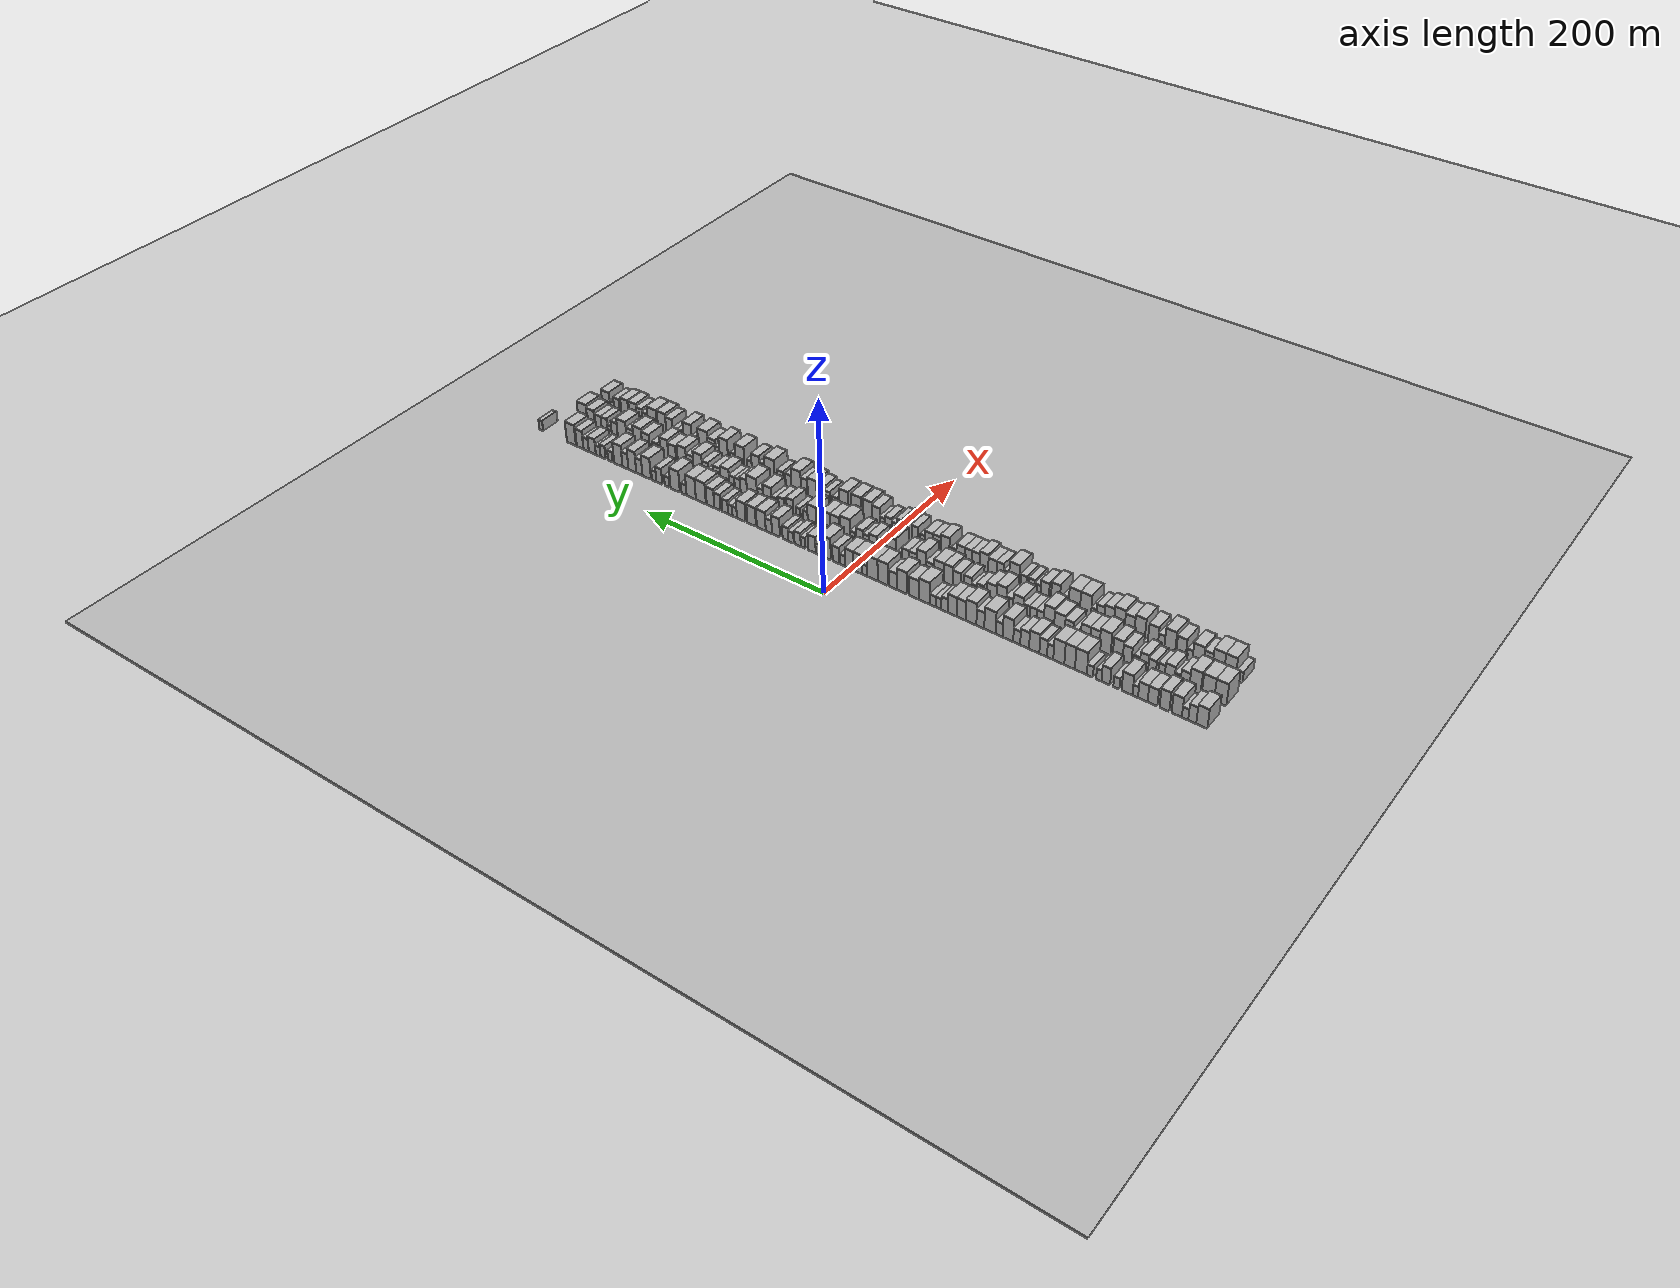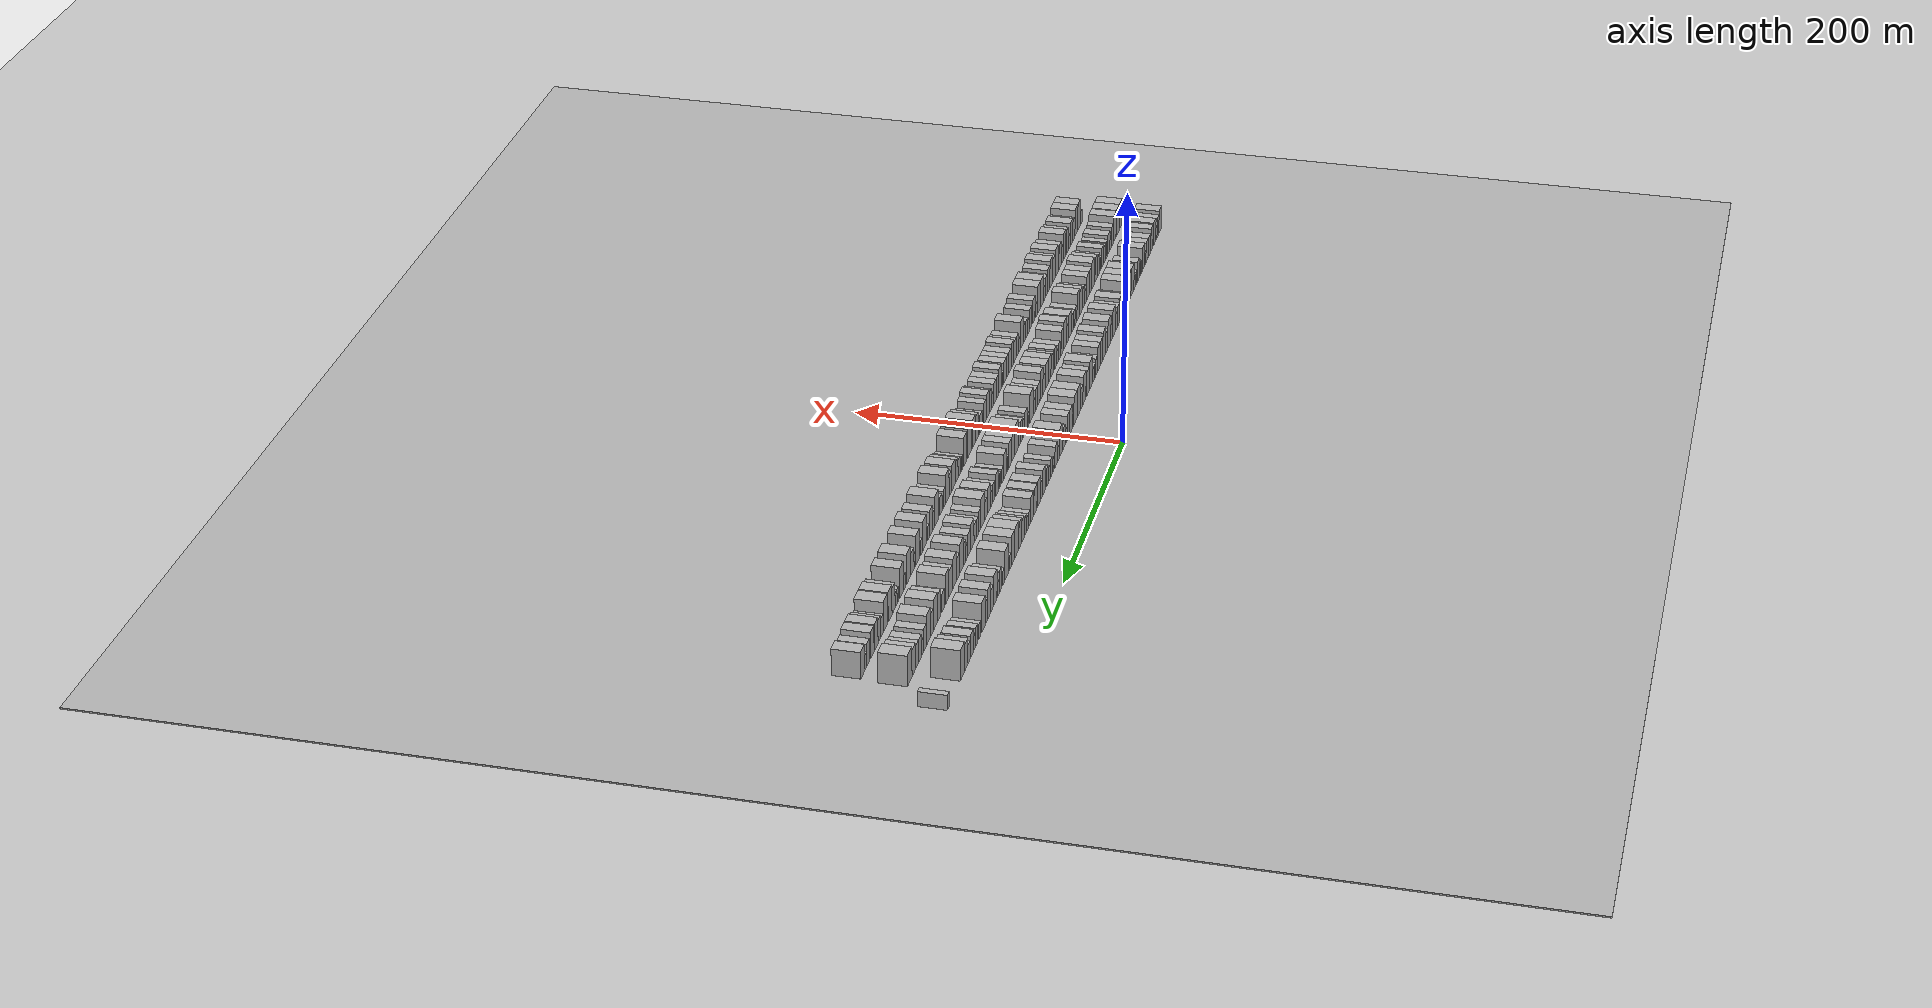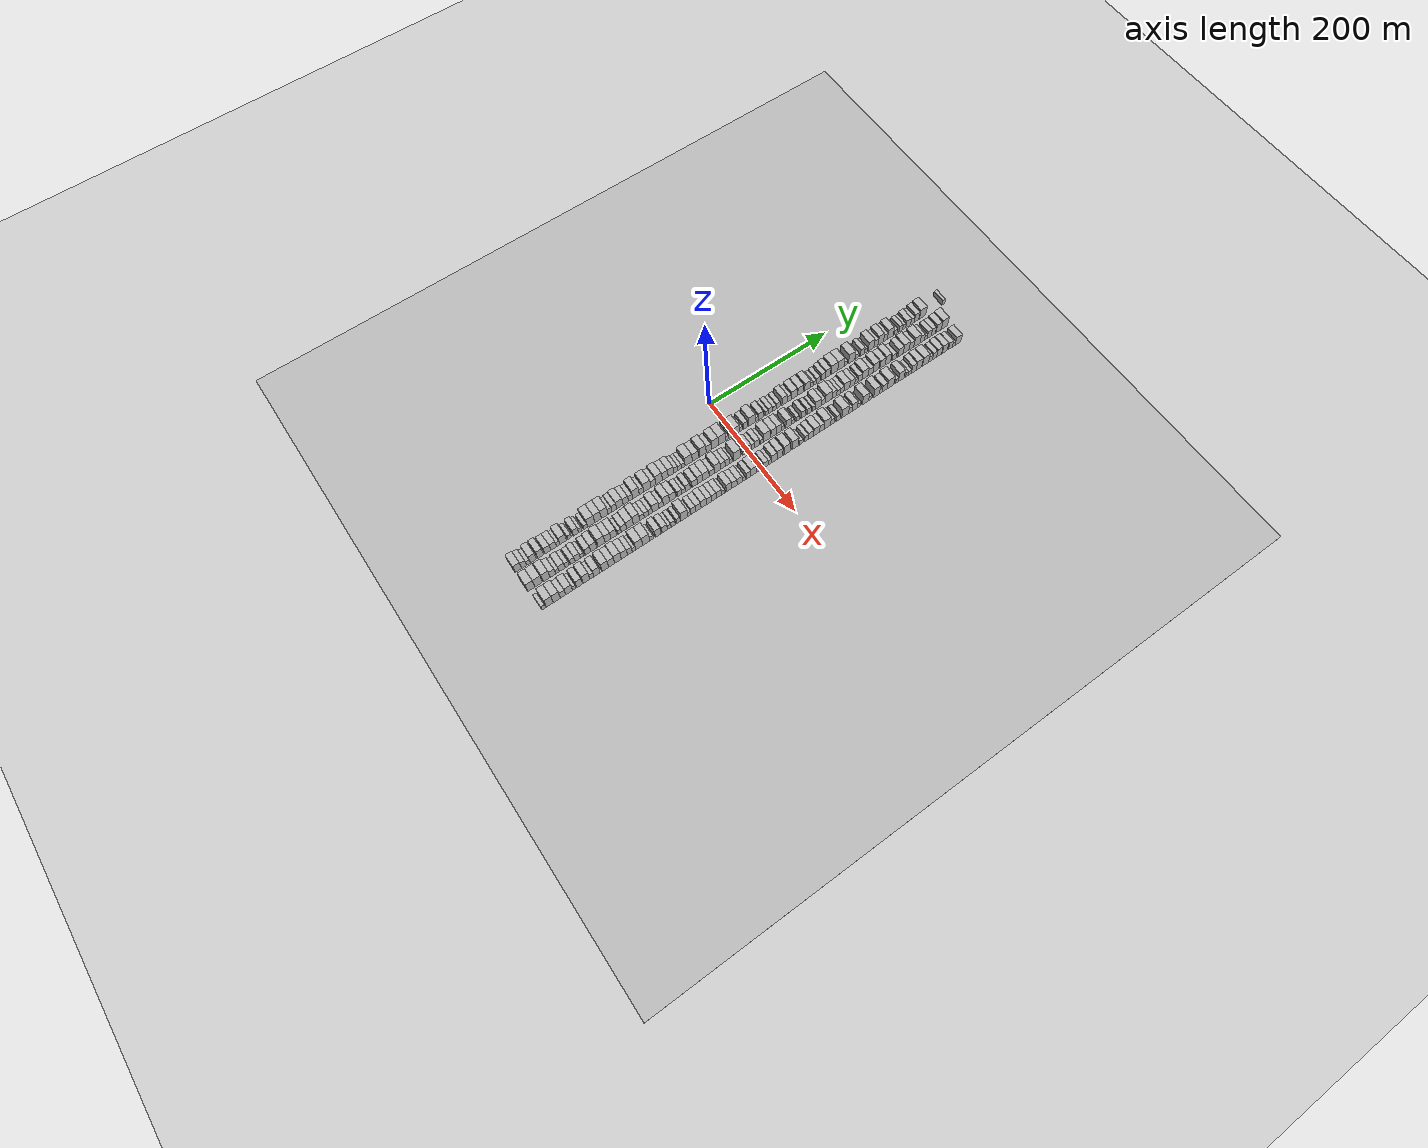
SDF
<?xml version="1.0" encoding="utf-8"?>

<sdf version="1.6">

   <world name="default">

      <gui fullscreen="0">

         <camera name="user_camera">

            <pose>-15 0 4.57585 0 0 0</pose>

            <view_controller>orbit</view_controller>

         </camera>

      </gui>

      <scene>

         <sky>

           <clouds>

             <speed>12</speed>

           </clouds>

         </sky>

         <ambient>0.4 0.4 0.4 1</ambient>

         <background>0.7 0.7 0.7 1</background>

         <shadows>1</shadows>

      </scene>

      <gravity>0 0 -9.8066</gravity>

      <magnetic_field>6e-06 2.3e-05 -4.2e-05</magnetic_field>

      <physics default="0" name="default_physics" type="ode">

         <ode>

            <solver>

               <type>quick</type>

               <iters>10</iters>

               <sor>1.0</sor>

               <use_dynamic_moi_rescaling>0</use_dynamic_moi_rescaling>

            </solver>

            <constraints>

               <cfm>0</cfm>

               <erp>0.2</erp>

               <contact_max_correcting_vel>100</contact_max_correcting_vel>

               <contact_surface_layer>0.001</contact_surface_layer>

            </constraints>

         </ode>

         <max_step_size>0.004</max_step_size>

         <real_time_factor>1</real_time_factor>

         <real_time_update_rate>250</real_time_update_rate>

      </physics>

      <light name="sun" type="directional">

         <cast_shadows>1</cast_shadows>

         <pose>0 0 10 0 0 0</pose>

         <diffuse>0.8 0.8 0.8 1</diffuse>

         <specular>0.2 0.2 0.2 1</specular>

         <attenuation>

            <range>1000</range>

            <constant>0.9</constant>

            <linear>0.01</linear>

            <quadratic>0.001</quadratic>

         </attenuation>

         <direction>-0.5 0.1 -0.9</direction>

      </light>

      <include>

         <name>ground_plane_1</name>

         <uri>model://HANNAS_ground_plane</uri>

         <pose>0 0 0  0 0 0</pose>

      </include>

      <include>

         <name>ground_plane_2</name>

         <uri>model://HANNAS_ground_plane</uri>

         <pose>100 0 0  0 0 0</pose>

      </include>

      <model name="building_1">

         <static>1</static>

         <pose frame="">50.0000 -343.0452 0 0.000000 0.000000 0.000000</pose>

         <link name="link">

            <pose frame="">0 0 10.50 0 0 0</pose>

            <collision name="collision">

               <geometry>

                  <box>

                     <size>20.0000 9.9096 21.0000</size>

                  </box>

               </geometry>

               <max_contacts>10</max_contacts>

               <surface>

                  <contact>

                     <ode/>

                  </contact>

                  <bounce/>

                  <friction>

                     <torsional>

                        <ode/>

                     </torsional>

                     <ode/>

                  </friction>

               </surface>

            </collision>

            <visual name="visual">

               <cast_shadows>0</cast_shadows>

               <geometry>

                  <box>

                     <size>20.0000 9.9096 21.0000</size>

                  </box>

               </geometry>

               <material>

                  <script>

                     <uri>model://HANNAS_wall/materials/scripts</uri>

                     <uri>model://HANNAS_wall/materials/textures</uri>

                     <name>vrc/HANNAS_wall</name>

                  </script>

               </material>

            </visual>

            <self_collide>0</self_collide>

            <enable_wind>0</enable_wind>

            <kinematic>0</kinematic>

         </link>

      </model>

      <model name="building_2">

         <static>1</static>

         <pose frame="">50.0000 -334.4748 0 0.000000 0.000000 0.000000</pose>

         <link name="link">

            <pose frame="">0 0 9.00 0 0 0</pose>

            <collision name="collision">

               <geometry>

                  <box>

                     <size>20.0000 7.2314 18.0000</size>

                  </box>

               </geometry>

               <max_contacts>10</max_contacts>

               <surface>

                  <contact>

                     <ode/>

                  </contact>

                  <bounce/>

                  <friction>

                     <torsional>

                        <ode/>

                     </torsional>

                     <ode/>

                  </friction>

               </surface>

            </collision>

            <visual name="visual">

               <cast_shadows>0</cast_shadows>

               <geometry>

                  <box>

                     <size>20.0000 7.2314 18.0000</size>

                  </box>

               </geometry>

               <material>

                  <script>

                     <uri>model://HANNAS_wall/materials/scripts</uri>

                     <uri>model://HANNAS_wall/materials/textures</uri>

                     <name>vrc/HANNAS_wall</name>

                  </script>

               </material>

            </visual>

            <self_collide>0</self_collide>

            <enable_wind>0</enable_wind>

            <kinematic>0</kinematic>

         </link>

      </model>

      <model name="building_3">

         <static>1</static>

         <pose frame="">50.0000 -328.0343 0 0.000000 0.000000 0.000000</pose>

         <link name="link">

            <pose frame="">0 0 6.00 0 0 0</pose>

            <collision name="collision">

               <geometry>

                  <box>

                     <size>20.0000 5.6495 12.0000</size>

                  </box>

               </geometry>

               <max_contacts>10</max_contacts>

               <surface>

                  <contact>

                     <ode/>

                  </contact>

                  <bounce/>

                  <friction>

                     <torsional>

                        <ode/>

                     </torsional>

                     <ode/>

                  </friction>

               </surface>

            </collision>

            <visual name="visual">

               <cast_shadows>0</cast_shadows>

               <geometry>

                  <box>

                     <size>20.0000 5.6495 12.0000</size>

                  </box>

               </geometry>

               <material>

                  <script>

                     <uri>model://HANNAS_wall/materials/scripts</uri>

                     <uri>model://HANNAS_wall/materials/textures</uri>

                     <name>vrc/HANNAS_wall</name>

                  </script>

               </material>

            </visual>

            <self_collide>0</self_collide>

            <enable_wind>0</enable_wind>

            <kinematic>0</kinematic>

         </link>

      </model>

      <model name="building_4">

         <static>1</static>

         <pose frame="">50.0000 -320.5536 0 0.000000 0.000000 0.000000</pose>

         <link name="link">

            <pose frame="">0 0 10.50 0 0 0</pose>

            <collision name="collision">

               <geometry>

                  <box>

                     <size>20.0000 9.3121 21.0000</size>

                  </box>

               </geometry>

               <max_contacts>10</max_contacts>

               <surface>

                  <contact>

                     <ode/>

                  </contact>

                  <bounce/>

                  <friction>

                     <torsional>

                        <ode/>

                     </torsional>

                     <ode/>

                  </friction>

               </surface>

            </collision>

            <visual name="visual">

               <cast_shadows>0</cast_shadows>

               <geometry>

                  <box>

                     <size>20.0000 9.3121 21.0000</size>

                  </box>

               </geometry>

               <material>

                  <script>

                     <uri>model://HANNAS_wall/materials/scripts</uri>

                     <uri>model://HANNAS_wall/materials/textures</uri>

                     <name>vrc/HANNAS_wall</name>

                  </script>

               </material>

            </visual>

            <self_collide>0</self_collide>

            <enable_wind>0</enable_wind>

            <kinematic>0</kinematic>

         </link>

      </model>

      <model name="building_5">

         <static>1</static>

         <pose frame="">50.0000 -309.4769 0 0.000000 0.000000 0.000000</pose>

         <link name="link">

            <pose frame="">0 0 10.50 0 0 0</pose>

            <collision name="collision">

               <geometry>

                  <box>

                     <size>20.0000 8.8412 21.0000</size>

                  </box>

               </geometry>

               <max_contacts>10</max_contacts>

               <surface>

                  <contact>

                     <ode/>

                  </contact>

                  <bounce/>

                  <friction>

                     <torsional>

                        <ode/>

                     </torsional>

                     <ode/>

                  </friction>

               </surface>

            </collision>

            <visual name="visual">

               <cast_shadows>0</cast_shadows>

               <geometry>

                  <box>

                     <size>20.0000 8.8412 21.0000</size>

                  </box>

               </geometry>

               <material>

                  <script>

                     <uri>model://HANNAS_wall/materials/scripts</uri>

                     <uri>model://HANNAS_wall/materials/textures</uri>

                     <name>vrc/HANNAS_wall</name>

                  </script>

               </material>

            </visual>

            <self_collide>0</self_collide>

            <enable_wind>0</enable_wind>

            <kinematic>0</kinematic>

         </link>

      </model>

      <model name="building_6">

         <static>1</static>

         <pose frame="">50.0000 -298.6147 0 0.000000 0.000000 0.000000</pose>

         <link name="link">

            <pose frame="">0 0 9.00 0 0 0</pose>

            <collision name="collision">

               <geometry>

                  <box>

                     <size>20.0000 8.8832 18.0000</size>

                  </box>

               </geometry>

               <max_contacts>10</max_contacts>

               <surface>

                  <contact>

                     <ode/>

                  </contact>

                  <bounce/>

                  <friction>

                     <torsional>

                        <ode/>

                     </torsional>

                     <ode/>

                  </friction>

               </surface>

            </collision>

            <visual name="visual">

               <cast_shadows>0</cast_shadows>

               <geometry>

                  <box>

                     <size>20.0000 8.8832 18.0000</size>

                  </box>

               </geometry>

               <material>

                  <script>

                     <uri>model://HANNAS_wall/materials/scripts</uri>

                     <uri>model://HANNAS_wall/materials/textures</uri>

                     <name>vrc/HANNAS_wall</name>

                  </script>

               </material>

            </visual>

            <self_collide>0</self_collide>

            <enable_wind>0</enable_wind>

            <kinematic>0</kinematic>

         </link>

      </model>

      <model name="building_7">

         <static>1</static>

         <pose frame="">50.0000 -289.7576 0 0.000000 0.000000 0.000000</pose>

         <link name="link">

            <pose frame="">0 0 9.00 0 0 0</pose>

            <collision name="collision">

               <geometry>

                  <box>

                     <size>20.0000 8.8311 18.0000</size>

                  </box>

               </geometry>

               <max_contacts>10</max_contacts>

               <surface>

                  <contact>

                     <ode/>

                  </contact>

                  <bounce/>

                  <friction>

                     <torsional>

                        <ode/>

                     </torsional>

                     <ode/>

                  </friction>

               </surface>

            </collision>

            <visual name="visual">

               <cast_shadows>0</cast_shadows>

               <geometry>

                  <box>

                     <size>20.0000 8.8311 18.0000</size>

                  </box>

               </geometry>

               <material>

                  <script>

                     <uri>model://HANNAS_wall/materials/scripts</uri>

                     <uri>model://HANNAS_wall/materials/textures</uri>

                     <name>vrc/HANNAS_wall</name>

                  </script>

               </material>

            </visual>

            <self_collide>0</self_collide>

            <enable_wind>0</enable_wind>

            <kinematic>0</kinematic>

         </link>

      </model>

      <model name="building_8">

         <static>1</static>

         <pose frame="">50.0000 -282.7856 0 0.000000 0.000000 0.000000</pose>

         <link name="link">

            <pose frame="">0 0 6.00 0 0 0</pose>

            <collision name="collision">

               <geometry>

                  <box>

                     <size>20.0000 5.1130 12.0000</size>

                  </box>

               </geometry>

               <max_contacts>10</max_contacts>

               <surface>

                  <contact>

                     <ode/>

                  </contact>

                  <bounce/>

                  <friction>

                     <torsional>

                        <ode/>

                     </torsional>

                     <ode/>

                  </friction>

               </surface>

            </collision>

            <visual name="visual">

               <cast_shadows>0</cast_shadows>

               <geometry>

                  <box>

                     <size>20.0000 5.1130 12.0000</size>

                  </box>

               </geometry>

               <material>

                  <script>

                     <uri>model://HANNAS_wall/materials/scripts</uri>

                     <uri>model://HANNAS_wall/materials/textures</uri>

                     <name>vrc/HANNAS_wall</name>

                  </script>

               </material>

            </visual>

            <self_collide>0</self_collide>

            <enable_wind>0</enable_wind>

            <kinematic>0</kinematic>

         </link>

      </model>

      <model name="building_9">

         <static>1</static>

         <pose frame="">50.0000 -275.1807 0 0.000000 0.000000 0.000000</pose>

         <link name="link">

            <pose frame="">0 0 10.50 0 0 0</pose>

            <collision name="collision">

               <geometry>

                  <box>

                     <size>20.0000 10.0968 21.0000</size>

                  </box>

               </geometry>

               <max_contacts>10</max_contacts>

               <surface>

                  <contact>

                     <ode/>

                  </contact>

                  <bounce/>

                  <friction>

                     <torsional>

                        <ode/>

                     </torsional>

                     <ode/>

                  </friction>

               </surface>

            </collision>

            <visual name="visual">

               <cast_shadows>0</cast_shadows>

               <geometry>

                  <box>

                     <size>20.0000 10.0968 21.0000</size>

                  </box>

               </geometry>

               <material>

                  <script>

                     <uri>model://HANNAS_wall/materials/scripts</uri>

                     <uri>model://HANNAS_wall/materials/textures</uri>

                     <name>vrc/HANNAS_wall</name>

                  </script>

               </material>

            </visual>

            <self_collide>0</self_collide>

            <enable_wind>0</enable_wind>

            <kinematic>0</kinematic>

         </link>

      </model>

      <model name="building_10">

         <static>1</static>

         <pose frame="">50.0000 -265.2949 0 0.000000 0.000000 0.000000</pose>

         <link name="link">

            <pose frame="">0 0 6.00 0 0 0</pose>

            <collision name="collision">

               <geometry>

                  <box>

                     <size>20.0000 5.6747 12.0000</size>

                  </box>

               </geometry>

               <max_contacts>10</max_contacts>

               <surface>

                  <contact>

                     <ode/>

                  </contact>

                  <bounce/>

                  <friction>

                     <torsional>

                        <ode/>

                     </torsional>

                     <ode/>

                  </friction>

               </surface>

            </collision>

            <visual name="visual">

               <cast_shadows>0</cast_shadows>

               <geometry>

                  <box>

                     <size>20.0000 5.6747 12.0000</size>

                  </box>

               </geometry>

               <material>

                  <script>

                     <uri>model://HANNAS_wall/materials/scripts</uri>

                     <uri>model://HANNAS_wall/materials/textures</uri>

                     <name>vrc/HANNAS_wall</name>

                  </script>

               </material>

            </visual>

            <self_collide>0</self_collide>

            <enable_wind>0</enable_wind>

            <kinematic>0</kinematic>

         </link>

      </model>

      <model name="building_11">

         <static>1</static>

         <pose frame="">50.0000 -255.3975 0 0.000000 0.000000 0.000000</pose>

         <link name="link">

            <pose frame="">0 0 9.00 0 0 0</pose>

            <collision name="collision">

               <geometry>

                  <box>

                     <size>20.0000 8.1202 18.0000</size>

                  </box>

               </geometry>

               <max_contacts>10</max_contacts>

               <surface>

                  <contact>

                     <ode/>

                  </contact>

                  <bounce/>

                  <friction>

                     <torsional>

                        <ode/>

                     </torsional>

                     <ode/>

                  </friction>

               </surface>

            </collision>

            <visual name="visual">

               <cast_shadows>0</cast_shadows>

               <geometry>

                  <box>

                     <size>20.0000 8.1202 18.0000</size>

                  </box>

               </geometry>

               <material>

                  <script>

                     <uri>model://HANNAS_wall/materials/scripts</uri>

                     <uri>model://HANNAS_wall/materials/textures</uri>

                     <name>vrc/HANNAS_wall</name>

                  </script>

               </material>

            </visual>

            <self_collide>0</self_collide>

            <enable_wind>0</enable_wind>

            <kinematic>0</kinematic>

         </link>

      </model>

      <model name="building_12">

         <static>1</static>

         <pose frame="">50.0000 -248.8593 0 0.000000 0.000000 0.000000</pose>

         <link name="link">

            <pose frame="">0 0 6.00 0 0 0</pose>

            <collision name="collision">

               <geometry>

                  <box>

                     <size>20.0000 4.9560 12.0000</size>

                  </box>

               </geometry>

               <max_contacts>10</max_contacts>

               <surface>

                  <contact>

                     <ode/>

                  </contact>

                  <bounce/>

                  <friction>

                     <torsional>

                        <ode/>

                     </torsional>

                     <ode/>

                  </friction>

               </surface>

            </collision>

            <visual name="visual">

               <cast_shadows>0</cast_shadows>

               <geometry>

                  <box>

                     <size>20.0000 4.9560 12.0000</size>

                  </box>

               </geometry>

               <material>

                  <script>

                     <uri>model://HANNAS_wall/materials/scripts</uri>

                     <uri>model://HANNAS_wall/materials/textures</uri>

                     <name>vrc/HANNAS_wall</name>

                  </script>

               </material>

            </visual>

            <self_collide>0</self_collide>

            <enable_wind>0</enable_wind>

            <kinematic>0</kinematic>

         </link>

      </model>

      <model name="building_13">

         <static>1</static>

         <pose frame="">50.0000 -240.5026 0 0.000000 0.000000 0.000000</pose>

         <link name="link">

            <pose frame="">0 0 6.00 0 0 0</pose>

            <collision name="collision">

               <geometry>

                  <box>

                     <size>20.0000 5.7574 12.0000</size>

                  </box>

               </geometry>

               <max_contacts>10</max_contacts>

               <surface>

                  <contact>

                     <ode/>

                  </contact>

                  <bounce/>

                  <friction>

                     <torsional>

                        <ode/>

                     </torsional>

                     <ode/>

                  </friction>

               </surface>

            </collision>

            <visual name="visual">

               <cast_shadows>0</cast_shadows>

               <geometry>

                  <box>

                     <size>20.0000 5.7574 12.0000</size>

                  </box>

               </geometry>

               <material>

                  <script>

                     <uri>model://HANNAS_wall/materials/scripts</uri>

                     <uri>model://HANNAS_wall/materials/textures</uri>

                     <name>vrc/HANNAS_wall</name>

                  </script>

               </material>

            </visual>

            <self_collide>0</self_collide>

            <enable_wind>0</enable_wind>

            <kinematic>0</kinematic>

         </link>

      </model>

      <model name="building_14">

         <static>1</static>

         <pose frame="">50.0000 -231.9556 0 0.000000 0.000000 0.000000</pose>

         <link name="link">

            <pose frame="">0 0 12.00 0 0 0</pose>

            <collision name="collision">

               <geometry>

                  <box>

                     <size>20.0000 11.3367 24.0000</size>

                  </box>

               </geometry>

               <max_contacts>10</max_contacts>

               <surface>

                  <contact>

                     <ode/>

                  </contact>

                  <bounce/>

                  <friction>

                     <torsional>

                        <ode/>

                     </torsional>

                     <ode/>

                  </friction>

               </surface>

            </collision>

            <visual name="visual">

               <cast_shadows>0</cast_shadows>

               <geometry>

                  <box>

                     <size>20.0000 11.3367 24.0000</size>

                  </box>

               </geometry>

               <material>

                  <script>

                     <uri>model://HANNAS_wall/materials/scripts</uri>

                     <uri>model://HANNAS_wall/materials/textures</uri>

                     <name>vrc/HANNAS_wall</name>

                  </script>

               </material>

            </visual>

            <self_collide>0</self_collide>

            <enable_wind>0</enable_wind>

            <kinematic>0</kinematic>

         </link>

      </model>

      <model name="building_15">

         <static>1</static>

         <pose frame="">50.0000 -221.1901 0 0.000000 0.000000 0.000000</pose>

         <link name="link">

            <pose frame="">0 0 12.00 0 0 0</pose>

            <collision name="collision">

               <geometry>

                  <box>

                     <size>20.0000 10.1943 24.0000</size>

                  </box>

               </geometry>

               <max_contacts>10</max_contacts>

               <surface>

                  <contact>

                     <ode/>

                  </contact>

                  <bounce/>

                  <friction>

                     <torsional>

                        <ode/>

                     </torsional>

                     <ode/>

                  </friction>

               </surface>

            </collision>

            <visual name="visual">

               <cast_shadows>0</cast_shadows>

               <geometry>

                  <box>

                     <size>20.0000 10.1943 24.0000</size>

                  </box>

               </geometry>

               <material>

                  <script>

                     <uri>model://HANNAS_wall/materials/scripts</uri>

                     <uri>model://HANNAS_wall/materials/textures</uri>

                     <name>vrc/HANNAS_wall</name>

                  </script>

               </material>

            </visual>

            <self_collide>0</self_collide>

            <enable_wind>0</enable_wind>

            <kinematic>0</kinematic>

         </link>

      </model>

      <model name="building_16">

         <static>1</static>

         <pose frame="">50.0000 -210.7837 0 0.000000 0.000000 0.000000</pose>

         <link name="link">

            <pose frame="">0 0 12.00 0 0 0</pose>

            <collision name="collision">

               <geometry>

                  <box>

                     <size>20.0000 10.6183 24.0000</size>

                  </box>

               </geometry>

               <max_contacts>10</max_contacts>

               <surface>

                  <contact>

                     <ode/>

                  </contact>

                  <bounce/>

                  <friction>

                     <torsional>

                        <ode/>

                     </torsional>

                     <ode/>

                  </friction>

               </surface>

            </collision>

            <visual name="visual">

               <cast_shadows>0</cast_shadows>

               <geometry>

                  <box>

                     <size>20.0000 10.6183 24.0000</size>

                  </box>

               </geometry>

               <material>

                  <script>

                     <uri>model://HANNAS_wall/materials/scripts</uri>

                     <uri>model://HANNAS_wall/materials/textures</uri>

                     <name>vrc/HANNAS_wall</name>

                  </script>

               </material>

            </visual>

            <self_collide>0</self_collide>

            <enable_wind>0</enable_wind>

            <kinematic>0</kinematic>

         </link>

      </model>

      <model name="building_17">

         <static>1</static>

         <pose frame="">50.0000 -202.4725 0 0.000000 0.000000 0.000000</pose>

         <link name="link">

            <pose frame="">0 0 7.50 0 0 0</pose>

            <collision name="collision">

               <geometry>

                  <box>

                     <size>20.0000 6.0041 15.0000</size>

                  </box>

               </geometry>

               <max_contacts>10</max_contacts>

               <surface>

                  <contact>

                     <ode/>

                  </contact>

                  <bounce/>

                  <friction>

                     <torsional>

                        <ode/>

                     </torsional>

                     <ode/>

                  </friction>

               </surface>

            </collision>

            <visual name="visual">

               <cast_shadows>0</cast_shadows>

               <geometry>

                  <box>

                     <size>20.0000 6.0041 15.0000</size>

                  </box>

               </geometry>

               <material>

                  <script>

                     <uri>model://HANNAS_wall/materials/scripts</uri>

                     <uri>model://HANNAS_wall/materials/textures</uri>

                     <name>vrc/HANNAS_wall</name>

                  </script>

               </material>

            </visual>

            <self_collide>0</self_collide>

            <enable_wind>0</enable_wind>

            <kinematic>0</kinematic>

         </link>

      </model>

      <model name="building_18">

         <static>1</static>

         <pose frame="">50.0000 -195.7502 0 0.000000 0.000000 0.000000</pose>

         <link name="link">

            <pose frame="">0 0 9.00 0 0 0</pose>

            <collision name="collision">

               <geometry>

                  <box>

                     <size>20.0000 7.4406 18.0000</size>

                  </box>

               </geometry>

               <max_contacts>10</max_contacts>

               <surface>

                  <contact>

                     <ode/>

                  </contact>

                  <bounce/>

                  <friction>

                     <torsional>

                        <ode/>

                     </torsional>

                     <ode/>

                  </friction>

               </surface>

            </collision>

            <visual name="visual">

               <cast_shadows>0</cast_shadows>

               <geometry>

                  <box>

                     <size>20.0000 7.4406 18.0000</size>

                  </box>

               </geometry>

               <material>

                  <script>

                     <uri>model://HANNAS_wall/materials/scripts</uri>

                     <uri>model://HANNAS_wall/materials/textures</uri>

                     <name>vrc/HANNAS_wall</name>

                  </script>

               </material>

            </visual>

            <self_collide>0</self_collide>

            <enable_wind>0</enable_wind>

            <kinematic>0</kinematic>

         </link>

      </model>

      <model name="building_19">

         <static>1</static>

         <pose frame="">50.0000 -187.0069 0 0.000000 0.000000 0.000000</pose>

         <link name="link">

            <pose frame="">0 0 10.50 0 0 0</pose>

            <collision name="collision">

               <geometry>

                  <box>

                     <size>20.0000 10.0460 21.0000</size>

                  </box>

               </geometry>

               <max_contacts>10</max_contacts>

               <surface>

                  <contact>

                     <ode/>

                  </contact>

                  <bounce/>

                  <friction>

                     <torsional>

                        <ode/>

                     </torsional>

                     <ode/>

                  </friction>

               </surface>

            </collision>

            <visual name="visual">

               <cast_shadows>0</cast_shadows>

               <geometry>

                  <box>

                     <size>20.0000 10.0460 21.0000</size>

                  </box>

               </geometry>

               <material>

                  <script>

                     <uri>model://HANNAS_wall/materials/scripts</uri>

                     <uri>model://HANNAS_wall/materials/textures</uri>

                     <name>vrc/HANNAS_wall</name>

                  </script>

               </material>

            </visual>

            <self_collide>0</self_collide>

            <enable_wind>0</enable_wind>

            <kinematic>0</kinematic>

         </link>

      </model>

      <model name="building_20">

         <static>1</static>

         <pose frame="">50.0000 -177.6431 0 0.000000 0.000000 0.000000</pose>

         <link name="link">

            <pose frame="">0 0 9.00 0 0 0</pose>

            <collision name="collision">

               <geometry>

                  <box>

                     <size>20.0000 8.6817 18.0000</size>

                  </box>

               </geometry>

               <max_contacts>10</max_contacts>

               <surface>

                  <contact>

                     <ode/>

                  </contact>

                  <bounce/>

                  <friction>

                     <torsional>

                        <ode/>

                     </torsional>

                     <ode/>

                  </friction>

               </surface>

            </collision>

            <visual name="visual">

               <cast_shadows>0</cast_shadows>

               <geometry>

                  <box>

                     <size>20.0000 8.6817 18.0000</size>

                  </box>

               </geometry>

               <material>

                  <script>

                     <uri>model://HANNAS_wall/materials/scripts</uri>

                     <uri>model://HANNAS_wall/materials/textures</uri>

                     <name>vrc/HANNAS_wall</name>

                  </script>

               </material>

            </visual>

            <self_collide>0</self_collide>

            <enable_wind>0</enable_wind>

            <kinematic>0</kinematic>

         </link>

      </model>

      <model name="building_21">

         <static>1</static>

         <pose frame="">50.0000 -169.8857 0 0.000000 0.000000 0.000000</pose>

         <link name="link">

            <pose frame="">0 0 7.50 0 0 0</pose>

            <collision name="collision">

               <geometry>

                  <box>

                     <size>20.0000 6.8331 15.0000</size>

                  </box>

               </geometry>

               <max_contacts>10</max_contacts>

               <surface>

                  <contact>

                     <ode/>

                  </contact>

                  <bounce/>

                  <friction>

                     <torsional>

                        <ode/>

                     </torsional>

                     <ode/>

                  </friction>

               </surface>

            </collision>

            <visual name="visual">

               <cast_shadows>0</cast_shadows>

               <geometry>

                  <box>

                     <size>20.0000 6.8331 15.0000</size>

                  </box>

               </geometry>

               <material>

                  <script>

                     <uri>model://HANNAS_wall/materials/scripts</uri>

                     <uri>model://HANNAS_wall/materials/textures</uri>

                     <name>vrc/HANNAS_wall</name>

                  </script>

               </material>

            </visual>

            <self_collide>0</self_collide>

            <enable_wind>0</enable_wind>

            <kinematic>0</kinematic>

         </link>

      </model>

      <model name="building_22">

         <static>1</static>

         <pose frame="">50.0000 -161.2846 0 0.000000 0.000000 0.000000</pose>

         <link name="link">

            <pose frame="">0 0 12.00 0 0 0</pose>

            <collision name="collision">

               <geometry>

                  <box>

                     <size>20.0000 10.3690 24.0000</size>

                  </box>

               </geometry>

               <max_contacts>10</max_contacts>

               <surface>

                  <contact>

                     <ode/>

                  </contact>

                  <bounce/>

                  <friction>

                     <torsional>

                        <ode/>

                     </torsional>

                     <ode/>

                  </friction>

               </surface>

            </collision>

            <visual name="visual">

               <cast_shadows>0</cast_shadows>

               <geometry>

                  <box>

                     <size>20.0000 10.3690 24.0000</size>

                  </box>

               </geometry>

               <material>

                  <script>

                     <uri>model://HANNAS_wall/materials/scripts</uri>

                     <uri>model://HANNAS_wall/materials/textures</uri>

                     <name>vrc/HANNAS_wall</name>

                  </script>

               </material>

            </visual>

            <self_collide>0</self_collide>

            <enable_wind>0</enable_wind>

            <kinematic>0</kinematic>

         </link>

      </model>

      <model name="building_23">

         <static>1</static>

         <pose frame="">50.0000 -152.5934 0 0.000000 0.000000 0.000000</pose>

         <link name="link">

            <pose frame="">0 0 7.50 0 0 0</pose>

            <collision name="collision">

               <geometry>

                  <box>

                     <size>20.0000 7.0134 15.0000</size>

                  </box>

               </geometry>

               <max_contacts>10</max_contacts>

               <surface>

                  <contact>

                     <ode/>

                  </contact>

                  <bounce/>

                  <friction>

                     <torsional>

                        <ode/>

                     </torsional>

                     <ode/>

                  </friction>

               </surface>

            </collision>

            <visual name="visual">

               <cast_shadows>0</cast_shadows>

               <geometry>

                  <box>

                     <size>20.0000 7.0134 15.0000</size>

                  </box>

               </geometry>

               <material>

                  <script>

                     <uri>model://HANNAS_wall/materials/scripts</uri>

                     <uri>model://HANNAS_wall/materials/textures</uri>

                     <name>vrc/HANNAS_wall</name>

                  </script>

               </material>

            </visual>

            <self_collide>0</self_collide>

            <enable_wind>0</enable_wind>

            <kinematic>0</kinematic>

         </link>

      </model>

      <model name="building_24">

         <static>1</static>

         <pose frame="">50.0000 -143.3795 0 0.000000 0.000000 0.000000</pose>

         <link name="link">

            <pose frame="">0 0 12.00 0 0 0</pose>

            <collision name="collision">

               <geometry>

                  <box>

                     <size>20.0000 11.4144 24.0000</size>

                  </box>

               </geometry>

               <max_contacts>10</max_contacts>

               <surface>

                  <contact>

                     <ode/>

                  </contact>

                  <bounce/>

                  <friction>

                     <torsional>

                        <ode/>

                     </torsional>

                     <ode/>

                  </friction>

               </surface>

            </collision>

            <visual name="visual">

               <cast_shadows>0</cast_shadows>

               <geometry>

                  <box>

                     <size>20.0000 11.4144 24.0000</size>

                  </box>

               </geometry>

               <material>

                  <script>

                     <uri>model://HANNAS_wall/materials/scripts</uri>

                     <uri>model://HANNAS_wall/materials/textures</uri>

                     <name>vrc/HANNAS_wall</name>

                  </script>

               </material>

            </visual>

            <self_collide>0</self_collide>

            <enable_wind>0</enable_wind>

            <kinematic>0</kinematic>

         </link>

      </model>

      <model name="building_25">

         <static>1</static>

         <pose frame="">50.0000 -133.7140 0 0.000000 0.000000 0.000000</pose>

         <link name="link">

            <pose frame="">0 0 9.00 0 0 0</pose>

            <collision name="collision">

               <geometry>

                  <box>

                     <size>20.0000 7.9168 18.0000</size>

                  </box>

               </geometry>

               <max_contacts>10</max_contacts>

               <surface>

                  <contact>

                     <ode/>

                  </contact>

                  <bounce/>

                  <friction>

                     <torsional>

                        <ode/>

                     </torsional>

                     <ode/>

                  </friction>

               </surface>

            </collision>

            <visual name="visual">

               <cast_shadows>0</cast_shadows>

               <geometry>

                  <box>

                     <size>20.0000 7.9168 18.0000</size>

                  </box>

               </geometry>

               <material>

                  <script>

                     <uri>model://HANNAS_wall/materials/scripts</uri>

                     <uri>model://HANNAS_wall/materials/textures</uri>

                     <name>vrc/HANNAS_wall</name>

                  </script>

               </material>

            </visual>

            <self_collide>0</self_collide>

            <enable_wind>0</enable_wind>

            <kinematic>0</kinematic>

         </link>

      </model>

      <model name="building_26">

         <static>1</static>

         <pose frame="">50.0000 -124.4781 0 0.000000 0.000000 0.000000</pose>

         <link name="link">

            <pose frame="">0 0 12.00 0 0 0</pose>

            <collision name="collision">

               <geometry>

                  <box>

                     <size>20.0000 10.5550 24.0000</size>

                  </box>

               </geometry>

               <max_contacts>10</max_contacts>

               <surface>

                  <contact>

                     <ode/>

                  </contact>

                  <bounce/>

                  <friction>

                     <torsional>

                        <ode/>

                     </torsional>

                     <ode/>

                  </friction>

               </surface>

            </collision>

            <visual name="visual">

               <cast_shadows>0</cast_shadows>

               <geometry>

                  <box>

                     <size>20.0000 10.5550 24.0000</size>

                  </box>

               </geometry>

               <material>

                  <script>

                     <uri>model://HANNAS_wall/materials/scripts</uri>

                     <uri>model://HANNAS_wall/materials/textures</uri>

                     <name>vrc/HANNAS_wall</name>

                  </script>

               </material>

            </visual>

            <self_collide>0</self_collide>

            <enable_wind>0</enable_wind>

            <kinematic>0</kinematic>

         </link>

      </model>

      <model name="building_27">

         <static>1</static>

         <pose frame="">50.0000 -114.5449 0 0.000000 0.000000 0.000000</pose>

         <link name="link">

            <pose frame="">0 0 10.50 0 0 0</pose>

            <collision name="collision">

               <geometry>

                  <box>

                     <size>20.0000 9.3114 21.0000</size>

                  </box>

               </geometry>

               <max_contacts>10</max_contacts>

               <surface>

                  <contact>

                     <ode/>

                  </contact>

                  <bounce/>

                  <friction>

                     <torsional>

                        <ode/>

                     </torsional>

                     <ode/>

                  </friction>

               </surface>

            </collision>

            <visual name="visual">

               <cast_shadows>0</cast_shadows>

               <geometry>

                  <box>

                     <size>20.0000 9.3114 21.0000</size>

                  </box>

               </geometry>

               <material>

                  <script>

                     <uri>model://HANNAS_wall/materials/scripts</uri>

                     <uri>model://HANNAS_wall/materials/textures</uri>

                     <name>vrc/HANNAS_wall</name>

                  </script>

               </material>

            </visual>

            <self_collide>0</self_collide>

            <enable_wind>0</enable_wind>

            <kinematic>0</kinematic>

         </link>

      </model>

      <model name="building_28">

         <static>1</static>

         <pose frame="">50.0000 -105.4226 0 0.000000 0.000000 0.000000</pose>

         <link name="link">

            <pose frame="">0 0 10.50 0 0 0</pose>

            <collision name="collision">

               <geometry>

                  <box>

                     <size>20.0000 8.9332 21.0000</size>

                  </box>

               </geometry>

               <max_contacts>10</max_contacts>

               <surface>

                  <contact>

                     <ode/>

                  </contact>

                  <bounce/>

                  <friction>

                     <torsional>

                        <ode/>

                     </torsional>

                     <ode/>

                  </friction>

               </surface>

            </collision>

            <visual name="visual">

               <cast_shadows>0</cast_shadows>

               <geometry>

                  <box>

                     <size>20.0000 8.9332 21.0000</size>

                  </box>

               </geometry>

               <material>

                  <script>

                     <uri>model://HANNAS_wall/materials/scripts</uri>

                     <uri>model://HANNAS_wall/materials/textures</uri>

                     <name>vrc/HANNAS_wall</name>

                  </script>

               </material>

            </visual>

            <self_collide>0</self_collide>

            <enable_wind>0</enable_wind>

            <kinematic>0</kinematic>

         </link>

      </model>

      <model name="building_29">

         <static>1</static>

         <pose frame="">50.0000 -97.5492 0 0.000000 0.000000 0.000000</pose>

         <link name="link">

            <pose frame="">0 0 7.50 0 0 0</pose>

            <collision name="collision">

               <geometry>

                  <box>

                     <size>20.0000 6.8135 15.0000</size>

                  </box>

               </geometry>

               <max_contacts>10</max_contacts>

               <surface>

                  <contact>

                     <ode/>

                  </contact>

                  <bounce/>

                  <friction>

                     <torsional>

                        <ode/>

                     </torsional>

                     <ode/>

                  </friction>

               </surface>

            </collision>

            <visual name="visual">

               <cast_shadows>0</cast_shadows>

               <geometry>

                  <box>

                     <size>20.0000 6.8135 15.0000</size>

                  </box>

               </geometry>

               <material>

                  <script>

                     <uri>model://HANNAS_wall/materials/scripts</uri>

                     <uri>model://HANNAS_wall/materials/textures</uri>

                     <name>vrc/HANNAS_wall</name>

                  </script>

               </material>

            </visual>

            <self_collide>0</self_collide>

            <enable_wind>0</enable_wind>

            <kinematic>0</kinematic>

         </link>

      </model>

      <model name="building_30">

         <static>1</static>

         <pose frame="">50.0000 -91.1669 0 0.000000 0.000000 0.000000</pose>

         <link name="link">

            <pose frame="">0 0 6.00 0 0 0</pose>

            <collision name="collision">

               <geometry>

                  <box>

                     <size>20.0000 5.9512 12.0000</size>

                  </box>

               </geometry>

               <max_contacts>10</max_contacts>

               <surface>

                  <contact>

                     <ode/>

                  </contact>

                  <bounce/>

                  <friction>

                     <torsional>

                        <ode/>

                     </torsional>

                     <ode/>

                  </friction>

               </surface>

            </collision>

            <visual name="visual">

               <cast_shadows>0</cast_shadows>

               <geometry>

                  <box>

                     <size>20.0000 5.9512 12.0000</size>

                  </box>

               </geometry>

               <material>

                  <script>

                     <uri>model://HANNAS_wall/materials/scripts</uri>

                     <uri>model://HANNAS_wall/materials/textures</uri>

                     <name>vrc/HANNAS_wall</name>

                  </script>

               </material>

            </visual>

            <self_collide>0</self_collide>

            <enable_wind>0</enable_wind>

            <kinematic>0</kinematic>

         </link>

      </model>

      <model name="building_31">

         <static>1</static>

         <pose frame="">50.0000 -85.3227 0 0.000000 0.000000 0.000000</pose>

         <link name="link">

            <pose frame="">0 0 6.00 0 0 0</pose>

            <collision name="collision">

               <geometry>

                  <box>

                     <size>20.0000 5.7373 12.0000</size>

                  </box>

               </geometry>

               <max_contacts>10</max_contacts>

               <surface>

                  <contact>

                     <ode/>

                  </contact>

                  <bounce/>

                  <friction>

                     <torsional>

                        <ode/>

                     </torsional>

                     <ode/>

                  </friction>

               </surface>

            </collision>

            <visual name="visual">

               <cast_shadows>0</cast_shadows>

               <geometry>

                  <box>

                     <size>20.0000 5.7373 12.0000</size>

                  </box>

               </geometry>

               <material>

                  <script>

                     <uri>model://HANNAS_wall/materials/scripts</uri>

                     <uri>model://HANNAS_wall/materials/textures</uri>

                     <name>vrc/HANNAS_wall</name>

                  </script>

               </material>

            </visual>

            <self_collide>0</self_collide>

            <enable_wind>0</enable_wind>

            <kinematic>0</kinematic>

         </link>

      </model>

      <model name="building_32">

         <static>1</static>

         <pose frame="">50.0000 -76.5606 0 0.000000 0.000000 0.000000</pose>

         <link name="link">

            <pose frame="">0 0 12.00 0 0 0</pose>

            <collision name="collision">

               <geometry>

                  <box>

                     <size>20.0000 11.7869 24.0000</size>

                  </box>

               </geometry>

               <max_contacts>10</max_contacts>

               <surface>

                  <contact>

                     <ode/>

                  </contact>

                  <bounce/>

                  <friction>

                     <torsional>

                        <ode/>

                     </torsional>

                     <ode/>

                  </friction>

               </surface>

            </collision>

            <visual name="visual">

               <cast_shadows>0</cast_shadows>

               <geometry>

                  <box>

                     <size>20.0000 11.7869 24.0000</size>

                  </box>

               </geometry>

               <material>

                  <script>

                     <uri>model://HANNAS_wall/materials/scripts</uri>

                     <uri>model://HANNAS_wall/materials/textures</uri>

                     <name>vrc/HANNAS_wall</name>

                  </script>

               </material>

            </visual>

            <self_collide>0</self_collide>

            <enable_wind>0</enable_wind>

            <kinematic>0</kinematic>

         </link>

      </model>

      <model name="building_33">

         <static>1</static>

         <pose frame="">50.0000 -65.5754 0 0.000000 0.000000 0.000000</pose>

         <link name="link">

            <pose frame="">0 0 10.50 0 0 0</pose>

            <collision name="collision">

               <geometry>

                  <box>

                     <size>20.0000 10.1834 21.0000</size>

                  </box>

               </geometry>

               <max_contacts>10</max_contacts>

               <surface>

                  <contact>

                     <ode/>

                  </contact>

                  <bounce/>

                  <friction>

                     <torsional>

                        <ode/>

                     </torsional>

                     <ode/>

                  </friction>

               </surface>

            </collision>

            <visual name="visual">

               <cast_shadows>0</cast_shadows>

               <geometry>

                  <box>

                     <size>20.0000 10.1834 21.0000</size>

                  </box>

               </geometry>

               <material>

                  <script>

                     <uri>model://HANNAS_wall/materials/scripts</uri>

                     <uri>model://HANNAS_wall/materials/textures</uri>

                     <name>vrc/HANNAS_wall</name>

                  </script>

               </material>

            </visual>

            <self_collide>0</self_collide>

            <enable_wind>0</enable_wind>

            <kinematic>0</kinematic>

         </link>

      </model>

      <model name="building_34">

         <static>1</static>

         <pose frame="">50.0000 -53.1653 0 0.000000 0.000000 0.000000</pose>

         <link name="link">

            <pose frame="">0 0 12.00 0 0 0</pose>

            <collision name="collision">

               <geometry>

                  <box>

                     <size>20.0000 10.6368 24.0000</size>

                  </box>

               </geometry>

               <max_contacts>10</max_contacts>

               <surface>

                  <contact>

                     <ode/>

                  </contact>

                  <bounce/>

                  <friction>

                     <torsional>

                        <ode/>

                     </torsional>

                     <ode/>

                  </friction>

               </surface>

            </collision>

            <visual name="visual">

               <cast_shadows>0</cast_shadows>

               <geometry>

                  <box>

                     <size>20.0000 10.6368 24.0000</size>

                  </box>

               </geometry>

               <material>

                  <script>

                     <uri>model://HANNAS_wall/materials/scripts</uri>

                     <uri>model://HANNAS_wall/materials/textures</uri>

                     <name>vrc/HANNAS_wall</name>

                  </script>

               </material>

            </visual>

            <self_collide>0</self_collide>

            <enable_wind>0</enable_wind>

            <kinematic>0</kinematic>

         </link>

      </model>

      <model name="building_35">

         <static>1</static>

         <pose frame="">50.0000 -43.5579 0 0.000000 0.000000 0.000000</pose>

         <link name="link">

            <pose frame="">0 0 9.00 0 0 0</pose>

            <collision name="collision">

               <geometry>

                  <box>

                     <size>20.0000 8.5779 18.0000</size>

                  </box>

               </geometry>

               <max_contacts>10</max_contacts>

               <surface>

                  <contact>

                     <ode/>

                  </contact>

                  <bounce/>

                  <friction>

                     <torsional>

                        <ode/>

                     </torsional>

                     <ode/>

                  </friction>

               </surface>

            </collision>

            <visual name="visual">

               <cast_shadows>0</cast_shadows>

               <geometry>

                  <box>

                     <size>20.0000 8.5779 18.0000</size>

                  </box>

               </geometry>

               <material>

                  <script>

                     <uri>model://HANNAS_wall/materials/scripts</uri>

                     <uri>model://HANNAS_wall/materials/textures</uri>

                     <name>vrc/HANNAS_wall</name>

                  </script>

               </material>

            </visual>

            <self_collide>0</self_collide>

            <enable_wind>0</enable_wind>

            <kinematic>0</kinematic>

         </link>

      </model>

      <model name="building_36">

         <static>1</static>

         <pose frame="">50.0000 -32.8664 0 0.000000 0.000000 0.000000</pose>

         <link name="link">

            <pose frame="">0 0 12.00 0 0 0</pose>

            <collision name="collision">

               <geometry>

                  <box>

                     <size>20.0000 10.8051 24.0000</size>

                  </box>

               </geometry>

               <max_contacts>10</max_contacts>

               <surface>

                  <contact>

                     <ode/>

                  </contact>

                  <bounce/>

                  <friction>

                     <torsional>

                        <ode/>

                     </torsional>

                     <ode/>

                  </friction>

               </surface>

            </collision>

            <visual name="visual">

               <cast_shadows>0</cast_shadows>

               <geometry>

                  <box>

                     <size>20.0000 10.8051 24.0000</size>

                  </box>

               </geometry>

               <material>

                  <script>

                     <uri>model://HANNAS_wall/materials/scripts</uri>

                     <uri>model://HANNAS_wall/materials/textures</uri>

                     <name>vrc/HANNAS_wall</name>

                  </script>

               </material>

            </visual>

            <self_collide>0</self_collide>

            <enable_wind>0</enable_wind>

            <kinematic>0</kinematic>

         </link>

      </model>

      <model name="building_37">

         <static>1</static>

         <pose frame="">50.0000 -21.7463 0 0.000000 0.000000 0.000000</pose>

         <link name="link">

            <pose frame="">0 0 12.00 0 0 0</pose>

            <collision name="collision">

               <geometry>

                  <box>

                     <size>20.0000 11.4351 24.0000</size>

                  </box>

               </geometry>

               <max_contacts>10</max_contacts>

               <surface>

                  <contact>

                     <ode/>

                  </contact>

                  <bounce/>

                  <friction>

                     <torsional>

                        <ode/>

                     </torsional>

                     <ode/>

                  </friction>

               </surface>

            </collision>

            <visual name="visual">

               <cast_shadows>0</cast_shadows>

               <geometry>

                  <box>

                     <size>20.0000 11.4351 24.0000</size>

                  </box>

               </geometry>

               <material>

                  <script>

                     <uri>model://HANNAS_wall/materials/scripts</uri>

                     <uri>model://HANNAS_wall/materials/textures</uri>

                     <name>vrc/HANNAS_wall</name>

                  </script>

               </material>

            </visual>

            <self_collide>0</self_collide>

            <enable_wind>0</enable_wind>

            <kinematic>0</kinematic>

         </link>

      </model>

      <model name="building_38">

         <static>1</static>

         <pose frame="">50.0000 -13.5464 0 0.000000 0.000000 0.000000</pose>

         <link name="link">

            <pose frame="">0 0 6.00 0 0 0</pose>

            <collision name="collision">

               <geometry>

                  <box>

                     <size>20.0000 4.9647 12.0000</size>

                  </box>

               </geometry>

               <max_contacts>10</max_contacts>

               <surface>

                  <contact>

                     <ode/>

                  </contact>

                  <bounce/>

                  <friction>

                     <torsional>

                        <ode/>

                     </torsional>

                     <ode/>

                  </friction>

               </surface>

            </collision>

            <visual name="visual">

               <cast_shadows>0</cast_shadows>

               <geometry>

                  <box>

                     <size>20.0000 4.9647 12.0000</size>

                  </box>

               </geometry>

               <material>

                  <script>

                     <uri>model://HANNAS_wall/materials/scripts</uri>

                     <uri>model://HANNAS_wall/materials/textures</uri>

                     <name>vrc/HANNAS_wall</name>

                  </script>

               </material>

            </visual>

            <self_collide>0</self_collide>

            <enable_wind>0</enable_wind>

            <kinematic>0</kinematic>

         </link>

      </model>

      <model name="building_39">

         <static>1</static>

         <pose frame="">50.0000 -6.4046 0 0.000000 0.000000 0.000000</pose>

         <link name="link">

            <pose frame="">0 0 10.50 0 0 0</pose>

            <collision name="collision">

               <geometry>

                  <box>

                     <size>20.0000 9.3189 21.0000</size>

                  </box>

               </geometry>

               <max_contacts>10</max_contacts>

               <surface>

                  <contact>

                     <ode/>

                  </contact>

                  <bounce/>

                  <friction>

                     <torsional>

                        <ode/>

                     </torsional>

                     <ode/>

                  </friction>

               </surface>

            </collision>

            <visual name="visual">

               <cast_shadows>0</cast_shadows>

               <geometry>

                  <box>

                     <size>20.0000 9.3189 21.0000</size>

                  </box>

               </geometry>

               <material>

                  <script>

                     <uri>model://HANNAS_wall/materials/scripts</uri>

                     <uri>model://HANNAS_wall/materials/textures</uri>

                     <name>vrc/HANNAS_wall</name>

                  </script>

               </material>

            </visual>

            <self_collide>0</self_collide>

            <enable_wind>0</enable_wind>

            <kinematic>0</kinematic>

         </link>

      </model>

      <model name="building_40">

         <static>1</static>

         <pose frame="">50.0000 2.8850 0 0.000000 0.000000 0.000000</pose>

         <link name="link">

            <pose frame="">0 0 10.50 0 0 0</pose>

            <collision name="collision">

               <geometry>

                  <box>

                     <size>20.0000 9.2605 21.0000</size>

                  </box>

               </geometry>

               <max_contacts>10</max_contacts>

               <surface>

                  <contact>

                     <ode/>

                  </contact>

                  <bounce/>

                  <friction>

                     <torsional>

                        <ode/>

                     </torsional>

                     <ode/>

                  </friction>

               </surface>

            </collision>

            <visual name="visual">

               <cast_shadows>0</cast_shadows>

               <geometry>

                  <box>

                     <size>20.0000 9.2605 21.0000</size>

                  </box>

               </geometry>

               <material>

                  <script>

                     <uri>model://HANNAS_wall/materials/scripts</uri>

                     <uri>model://HANNAS_wall/materials/textures</uri>

                     <name>vrc/HANNAS_wall</name>

                  </script>

               </material>

            </visual>

            <self_collide>0</self_collide>

            <enable_wind>0</enable_wind>

            <kinematic>0</kinematic>

         </link>

      </model>

      <model name="building_41">

         <static>1</static>

         <pose frame="">50.0000 10.0481 0 0.000000 0.000000 0.000000</pose>

         <link name="link">

            <pose frame="">0 0 6.00 0 0 0</pose>

            <collision name="collision">

               <geometry>

                  <box>

                     <size>20.0000 5.0657 12.0000</size>

                  </box>

               </geometry>

               <max_contacts>10</max_contacts>

               <surface>

                  <contact>

                     <ode/>

                  </contact>

                  <bounce/>

                  <friction>

                     <torsional>

                        <ode/>

                     </torsional>

                     <ode/>

                  </friction>

               </surface>

            </collision>

            <visual name="visual">

               <cast_shadows>0</cast_shadows>

               <geometry>

                  <box>

                     <size>20.0000 5.0657 12.0000</size>

                  </box>

               </geometry>

               <material>

                  <script>

                     <uri>model://HANNAS_wall/materials/scripts</uri>

                     <uri>model://HANNAS_wall/materials/textures</uri>

                     <name>vrc/HANNAS_wall</name>

                  </script>

               </material>

            </visual>

            <self_collide>0</self_collide>

            <enable_wind>0</enable_wind>

            <kinematic>0</kinematic>

         </link>

      </model>

      <model name="building_42">

         <static>1</static>

         <pose frame="">50.0000 17.3400 0 0.000000 0.000000 0.000000</pose>

         <link name="link">

            <pose frame="">0 0 9.00 0 0 0</pose>

            <collision name="collision">

               <geometry>

                  <box>

                     <size>20.0000 7.5182 18.0000</size>

                  </box>

               </geometry>

               <max_contacts>10</max_contacts>

               <surface>

                  <contact>

                     <ode/>

                  </contact>

                  <bounce/>

                  <friction>

                     <torsional>

                        <ode/>

                     </torsional>

                     <ode/>

                  </friction>

               </surface>

            </collision>

            <visual name="visual">

               <cast_shadows>0</cast_shadows>

               <geometry>

                  <box>

                     <size>20.0000 7.5182 18.0000</size>

                  </box>

               </geometry>

               <material>

                  <script>

                     <uri>model://HANNAS_wall/materials/scripts</uri>

                     <uri>model://HANNAS_wall/materials/textures</uri>

                     <name>vrc/HANNAS_wall</name>

                  </script>

               </material>

            </visual>

            <self_collide>0</self_collide>

            <enable_wind>0</enable_wind>

            <kinematic>0</kinematic>

         </link>

      </model>

      <model name="building_43">

         <static>1</static>

         <pose frame="">50.0000 28.6261 0 0.000000 0.000000 0.000000</pose>

         <link name="link">

            <pose frame="">0 0 12.00 0 0 0</pose>

            <collision name="collision">

               <geometry>

                  <box>

                     <size>20.0000 11.0540 24.0000</size>

                  </box>

               </geometry>

               <max_contacts>10</max_contacts>

               <surface>

                  <contact>

                     <ode/>

                  </contact>

                  <bounce/>

                  <friction>

                     <torsional>

                        <ode/>

                     </torsional>

                     <ode/>

                  </friction>

               </surface>

            </collision>

            <visual name="visual">

               <cast_shadows>0</cast_shadows>

               <geometry>

                  <box>

                     <size>20.0000 11.0540 24.0000</size>

                  </box>

               </geometry>

               <material>

                  <script>

                     <uri>model://HANNAS_wall/materials/scripts</uri>

                     <uri>model://HANNAS_wall/materials/textures</uri>

                     <name>vrc/HANNAS_wall</name>

                  </script>

               </material>

            </visual>

            <self_collide>0</self_collide>

            <enable_wind>0</enable_wind>

            <kinematic>0</kinematic>

         </link>

      </model>

      <model name="building_44">

         <static>1</static>

         <pose frame="">50.0000 36.9282 0 0.000000 0.000000 0.000000</pose>

         <link name="link">

            <pose frame="">0 0 6.00 0 0 0</pose>

            <collision name="collision">

               <geometry>

                  <box>

                     <size>20.0000 5.5501 12.0000</size>

                  </box>

               </geometry>

               <max_contacts>10</max_contacts>

               <surface>

                  <contact>

                     <ode/>

                  </contact>

                  <bounce/>

                  <friction>

                     <torsional>

                        <ode/>

                     </torsional>

                     <ode/>

                  </friction>

               </surface>

            </collision>

            <visual name="visual">

               <cast_shadows>0</cast_shadows>

               <geometry>

                  <box>

                     <size>20.0000 5.5501 12.0000</size>

                  </box>

               </geometry>

               <material>

                  <script>

                     <uri>model://HANNAS_wall/materials/scripts</uri>

                     <uri>model://HANNAS_wall/materials/textures</uri>

                     <name>vrc/HANNAS_wall</name>

                  </script>

               </material>

            </visual>

            <self_collide>0</self_collide>

            <enable_wind>0</enable_wind>

            <kinematic>0</kinematic>

         </link>

      </model>

      <model name="building_45">

         <static>1</static>

         <pose frame="">50.0000 43.9661 0 0.000000 0.000000 0.000000</pose>

         <link name="link">

            <pose frame="">0 0 9.00 0 0 0</pose>

            <collision name="collision">

               <geometry>

                  <box>

                     <size>20.0000 8.5257 18.0000</size>

                  </box>

               </geometry>

               <max_contacts>10</max_contacts>

               <surface>

                  <contact>

                     <ode/>

                  </contact>

                  <bounce/>

                  <friction>

                     <torsional>

                        <ode/>

                     </torsional>

                     <ode/>

                  </friction>

               </surface>

            </collision>

            <visual name="visual">

               <cast_shadows>0</cast_shadows>

               <geometry>

                  <box>

                     <size>20.0000 8.5257 18.0000</size>

                  </box>

               </geometry>

               <material>

                  <script>

                     <uri>model://HANNAS_wall/materials/scripts</uri>

                     <uri>model://HANNAS_wall/materials/textures</uri>

                     <name>vrc/HANNAS_wall</name>

                  </script>

               </material>

            </visual>

            <self_collide>0</self_collide>

            <enable_wind>0</enable_wind>

            <kinematic>0</kinematic>

         </link>

      </model>

      <model name="building_46">

         <static>1</static>

         <pose frame="">50.0000 53.7685 0 0.000000 0.000000 0.000000</pose>

         <link name="link">

            <pose frame="">0 0 6.00 0 0 0</pose>

            <collision name="collision">

               <geometry>

                  <box>

                     <size>20.0000 5.0791 12.0000</size>

                  </box>

               </geometry>

               <max_contacts>10</max_contacts>

               <surface>

                  <contact>

                     <ode/>

                  </contact>

                  <bounce/>

                  <friction>

                     <torsional>

                        <ode/>

                     </torsional>

                     <ode/>

                  </friction>

               </surface>

            </collision>

            <visual name="visual">

               <cast_shadows>0</cast_shadows>

               <geometry>

                  <box>

                     <size>20.0000 5.0791 12.0000</size>

                  </box>

               </geometry>

               <material>

                  <script>

                     <uri>model://HANNAS_wall/materials/scripts</uri>

                     <uri>model://HANNAS_wall/materials/textures</uri>

                     <name>vrc/HANNAS_wall</name>

                  </script>

               </material>

            </visual>

            <self_collide>0</self_collide>

            <enable_wind>0</enable_wind>

            <kinematic>0</kinematic>

         </link>

      </model>

      <model name="building_47">

         <static>1</static>

         <pose frame="">50.0000 59.7450 0 0.000000 0.000000 0.000000</pose>

         <link name="link">

            <pose frame="">0 0 7.50 0 0 0</pose>

            <collision name="collision">

               <geometry>

                  <box>

                     <size>20.0000 6.8741 15.0000</size>

                  </box>

               </geometry>

               <max_contacts>10</max_contacts>

               <surface>

                  <contact>

                     <ode/>

                  </contact>

                  <bounce/>

                  <friction>

                     <torsional>

                        <ode/>

                     </torsional>

                     <ode/>

                  </friction>

               </surface>

            </collision>

            <visual name="visual">

               <cast_shadows>0</cast_shadows>

               <geometry>

                  <box>

                     <size>20.0000 6.8741 15.0000</size>

                  </box>

               </geometry>

               <material>

                  <script>

                     <uri>model://HANNAS_wall/materials/scripts</uri>

                     <uri>model://HANNAS_wall/materials/textures</uri>

                     <name>vrc/HANNAS_wall</name>

                  </script>

               </material>

            </visual>

            <self_collide>0</self_collide>

            <enable_wind>0</enable_wind>

            <kinematic>0</kinematic>

         </link>

      </model>

      <model name="building_48">

         <static>1</static>

         <pose frame="">50.0000 67.1361 0 0.000000 0.000000 0.000000</pose>

         <link name="link">

            <pose frame="">0 0 6.00 0 0 0</pose>

            <collision name="collision">

               <geometry>

                  <box>

                     <size>20.0000 5.9081 12.0000</size>

                  </box>

               </geometry>

               <max_contacts>10</max_contacts>

               <surface>

                  <contact>

                     <ode/>

                  </contact>

                  <bounce/>

                  <friction>

                     <torsional>

                        <ode/>

                     </torsional>

                     <ode/>

                  </friction>

               </surface>

            </collision>

            <visual name="visual">

               <cast_shadows>0</cast_shadows>

               <geometry>

                  <box>

                     <size>20.0000 5.9081 12.0000</size>

                  </box>

               </geometry>

               <material>

                  <script>

                     <uri>model://HANNAS_wall/materials/scripts</uri>

                     <uri>model://HANNAS_wall/materials/textures</uri>

                     <name>vrc/HANNAS_wall</name>

                  </script>

               </material>

            </visual>

            <self_collide>0</self_collide>

            <enable_wind>0</enable_wind>

            <kinematic>0</kinematic>

         </link>

      </model>

      <model name="building_49">

         <static>1</static>

         <pose frame="">50.0000 73.3702 0 0.000000 0.000000 0.000000</pose>

         <link name="link">

            <pose frame="">0 0 7.50 0 0 0</pose>

            <collision name="collision">

               <geometry>

                  <box>

                     <size>20.0000 6.5601 15.0000</size>

                  </box>

               </geometry>

               <max_contacts>10</max_contacts>

               <surface>

                  <contact>

                     <ode/>

                  </contact>

                  <bounce/>

                  <friction>

                     <torsional>

                        <ode/>

                     </torsional>

                     <ode/>

                  </friction>

               </surface>

            </collision>

            <visual name="visual">

               <cast_shadows>0</cast_shadows>

               <geometry>

                  <box>

                     <size>20.0000 6.5601 15.0000</size>

                  </box>

               </geometry>

               <material>

                  <script>

                     <uri>model://HANNAS_wall/materials/scripts</uri>

                     <uri>model://HANNAS_wall/materials/textures</uri>

                     <name>vrc/HANNAS_wall</name>

                  </script>

               </material>

            </visual>

            <self_collide>0</self_collide>

            <enable_wind>0</enable_wind>

            <kinematic>0</kinematic>

         </link>

      </model>

      <model name="building_50">

         <static>1</static>

         <pose frame="">50.0000 84.1636 0 0.000000 0.000000 0.000000</pose>

         <link name="link">

            <pose frame="">0 0 10.50 0 0 0</pose>

            <collision name="collision">

               <geometry>

                  <box>

                     <size>20.0000 9.0267 21.0000</size>

                  </box>

               </geometry>

               <max_contacts>10</max_contacts>

               <surface>

                  <contact>

                     <ode/>

                  </contact>

                  <bounce/>

                  <friction>

                     <torsional>

                        <ode/>

                     </torsional>

                     <ode/>

                  </friction>

               </surface>

            </collision>

            <visual name="visual">

               <cast_shadows>0</cast_shadows>

               <geometry>

                  <box>

                     <size>20.0000 9.0267 21.0000</size>

                  </box>

               </geometry>

               <material>

                  <script>

                     <uri>model://HANNAS_wall/materials/scripts</uri>

                     <uri>model://HANNAS_wall/materials/textures</uri>

                     <name>vrc/HANNAS_wall</name>

                  </script>

               </material>

            </visual>

            <self_collide>0</self_collide>

            <enable_wind>0</enable_wind>

            <kinematic>0</kinematic>

         </link>

      </model>

      <model name="building_51">

         <static>1</static>

         <pose frame="">50.0000 92.2090 0 0.000000 0.000000 0.000000</pose>

         <link name="link">

            <pose frame="">0 0 7.50 0 0 0</pose>

            <collision name="collision">

               <geometry>

                  <box>

                     <size>20.0000 7.0641 15.0000</size>

                  </box>

               </geometry>

               <max_contacts>10</max_contacts>

               <surface>

                  <contact>

                     <ode/>

                  </contact>

                  <bounce/>

                  <friction>

                     <torsional>

                        <ode/>

                     </torsional>

                     <ode/>

                  </friction>

               </surface>

            </collision>

            <visual name="visual">

               <cast_shadows>0</cast_shadows>

               <geometry>

                  <box>

                     <size>20.0000 7.0641 15.0000</size>

                  </box>

               </geometry>

               <material>

                  <script>

                     <uri>model://HANNAS_wall/materials/scripts</uri>

                     <uri>model://HANNAS_wall/materials/textures</uri>

                     <name>vrc/HANNAS_wall</name>

                  </script>

               </material>

            </visual>

            <self_collide>0</self_collide>

            <enable_wind>0</enable_wind>

            <kinematic>0</kinematic>

         </link>

      </model>

      <model name="building_52">

         <static>1</static>

         <pose frame="">50.0000 100.8446 0 0.000000 0.000000 0.000000</pose>

         <link name="link">

            <pose frame="">0 0 10.50 0 0 0</pose>

            <collision name="collision">

               <geometry>

                  <box>

                     <size>20.0000 10.2070 21.0000</size>

                  </box>

               </geometry>

               <max_contacts>10</max_contacts>

               <surface>

                  <contact>

                     <ode/>

                  </contact>

                  <bounce/>

                  <friction>

                     <torsional>

                        <ode/>

                     </torsional>

                     <ode/>

                  </friction>

               </surface>

            </collision>

            <visual name="visual">

               <cast_shadows>0</cast_shadows>

               <geometry>

                  <box>

                     <size>20.0000 10.2070 21.0000</size>

                  </box>

               </geometry>

               <material>

                  <script>

                     <uri>model://HANNAS_wall/materials/scripts</uri>

                     <uri>model://HANNAS_wall/materials/textures</uri>

                     <name>vrc/HANNAS_wall</name>

                  </script>

               </material>

            </visual>

            <self_collide>0</self_collide>

            <enable_wind>0</enable_wind>

            <kinematic>0</kinematic>

         </link>

      </model>

      <model name="building_53">

         <static>1</static>

         <pose frame="">50.0000 111.8864 0 0.000000 0.000000 0.000000</pose>

         <link name="link">

            <pose frame="">0 0 10.50 0 0 0</pose>

            <collision name="collision">

               <geometry>

                  <box>

                     <size>20.0000 9.8765 21.0000</size>

                  </box>

               </geometry>

               <max_contacts>10</max_contacts>

               <surface>

                  <contact>

                     <ode/>

                  </contact>

                  <bounce/>

                  <friction>

                     <torsional>

                        <ode/>

                     </torsional>

                     <ode/>

                  </friction>

               </surface>

            </collision>

            <visual name="visual">

               <cast_shadows>0</cast_shadows>

               <geometry>

                  <box>

                     <size>20.0000 9.8765 21.0000</size>

                  </box>

               </geometry>

               <material>

                  <script>

                     <uri>model://HANNAS_wall/materials/scripts</uri>

                     <uri>model://HANNAS_wall/materials/textures</uri>

                     <name>vrc/HANNAS_wall</name>

                  </script>

               </material>

            </visual>

            <self_collide>0</self_collide>

            <enable_wind>0</enable_wind>

            <kinematic>0</kinematic>

         </link>

      </model>

      <model name="building_54">

         <static>1</static>

         <pose frame="">50.0000 123.8208 0 0.000000 0.000000 0.000000</pose>

         <link name="link">

            <pose frame="">0 0 10.50 0 0 0</pose>

            <collision name="collision">

               <geometry>

                  <box>

                     <size>20.0000 9.9922 21.0000</size>

                  </box>

               </geometry>

               <max_contacts>10</max_contacts>

               <surface>

                  <contact>

                     <ode/>

                  </contact>

                  <bounce/>

                  <friction>

                     <torsional>

                        <ode/>

                     </torsional>

                     <ode/>

                  </friction>

               </surface>

            </collision>

            <visual name="visual">

               <cast_shadows>0</cast_shadows>

               <geometry>

                  <box>

                     <size>20.0000 9.9922 21.0000</size>

                  </box>

               </geometry>

               <material>

                  <script>

                     <uri>model://HANNAS_wall/materials/scripts</uri>

                     <uri>model://HANNAS_wall/materials/textures</uri>

                     <name>vrc/HANNAS_wall</name>

                  </script>

               </material>

            </visual>

            <self_collide>0</self_collide>

            <enable_wind>0</enable_wind>

            <kinematic>0</kinematic>

         </link>

      </model>

      <model name="building_55">

         <static>1</static>

         <pose frame="">50.0000 131.3743 0 0.000000 0.000000 0.000000</pose>

         <link name="link">

            <pose frame="">0 0 6.00 0 0 0</pose>

            <collision name="collision">

               <geometry>

                  <box>

                     <size>20.0000 5.1148 12.0000</size>

                  </box>

               </geometry>

               <max_contacts>10</max_contacts>

               <surface>

                  <contact>

                     <ode/>

                  </contact>

                  <bounce/>

                  <friction>

                     <torsional>

                        <ode/>

                     </torsional>

                     <ode/>

                  </friction>

               </surface>

            </collision>

            <visual name="visual">

               <cast_shadows>0</cast_shadows>

               <geometry>

                  <box>

                     <size>20.0000 5.1148 12.0000</size>

                  </box>

               </geometry>

               <material>

                  <script>

                     <uri>model://HANNAS_wall/materials/scripts</uri>

                     <uri>model://HANNAS_wall/materials/textures</uri>

                     <name>vrc/HANNAS_wall</name>

                  </script>

               </material>

            </visual>

            <self_collide>0</self_collide>

            <enable_wind>0</enable_wind>

            <kinematic>0</kinematic>

         </link>

      </model>

      <model name="building_56">

         <static>1</static>

         <pose frame="">50.0000 136.5157 0 0.000000 0.000000 0.000000</pose>

         <link name="link">

            <pose frame="">0 0 6.00 0 0 0</pose>

            <collision name="collision">

               <geometry>

                  <box>

                     <size>20.0000 5.1680 12.0000</size>

                  </box>

               </geometry>

               <max_contacts>10</max_contacts>

               <surface>

                  <contact>

                     <ode/>

                  </contact>

                  <bounce/>

                  <friction>

                     <torsional>

                        <ode/>

                     </torsional>

                     <ode/>

                  </friction>

               </surface>

            </collision>

            <visual name="visual">

               <cast_shadows>0</cast_shadows>

               <geometry>

                  <box>

                     <size>20.0000 5.1680 12.0000</size>

                  </box>

               </geometry>

               <material>

                  <script>

                     <uri>model://HANNAS_wall/materials/scripts</uri>

                     <uri>model://HANNAS_wall/materials/textures</uri>

                     <name>vrc/HANNAS_wall</name>

                  </script>

               </material>

            </visual>

            <self_collide>0</self_collide>

            <enable_wind>0</enable_wind>

            <kinematic>0</kinematic>

         </link>

      </model>

      <model name="building_57">

         <static>1</static>

         <pose frame="">50.0000 142.4698 0 0.000000 0.000000 0.000000</pose>

         <link name="link">

            <pose frame="">0 0 7.50 0 0 0</pose>

            <collision name="collision">

               <geometry>

                  <box>

                     <size>20.0000 6.7401 15.0000</size>

                  </box>

               </geometry>

               <max_contacts>10</max_contacts>

               <surface>

                  <contact>

                     <ode/>

                  </contact>

                  <bounce/>

                  <friction>

                     <torsional>

                        <ode/>

                     </torsional>

                     <ode/>

                  </friction>

               </surface>

            </collision>

            <visual name="visual">

               <cast_shadows>0</cast_shadows>

               <geometry>

                  <box>

                     <size>20.0000 6.7401 15.0000</size>

                  </box>

               </geometry>

               <material>

                  <script>

                     <uri>model://HANNAS_wall/materials/scripts</uri>

                     <uri>model://HANNAS_wall/materials/textures</uri>

                     <name>vrc/HANNAS_wall</name>

                  </script>

               </material>

            </visual>

            <self_collide>0</self_collide>

            <enable_wind>0</enable_wind>

            <kinematic>0</kinematic>

         </link>

      </model>

      <model name="building_58">

         <static>1</static>

         <pose frame="">50.0000 151.4992 0 0.000000 0.000000 0.000000</pose>

         <link name="link">

            <pose frame="">0 0 9.00 0 0 0</pose>

            <collision name="collision">

               <geometry>

                  <box>

                     <size>20.0000 7.3187 18.0000</size>

                  </box>

               </geometry>

               <max_contacts>10</max_contacts>

               <surface>

                  <contact>

                     <ode/>

                  </contact>

                  <bounce/>

                  <friction>

                     <torsional>

                        <ode/>

                     </torsional>

                     <ode/>

                  </friction>

               </surface>

            </collision>

            <visual name="visual">

               <cast_shadows>0</cast_shadows>

               <geometry>

                  <box>

                     <size>20.0000 7.3187 18.0000</size>

                  </box>

               </geometry>

               <material>

                  <script>

                     <uri>model://HANNAS_wall/materials/scripts</uri>

                     <uri>model://HANNAS_wall/materials/textures</uri>

                     <name>vrc/HANNAS_wall</name>

                  </script>

               </material>

            </visual>

            <self_collide>0</self_collide>

            <enable_wind>0</enable_wind>

            <kinematic>0</kinematic>

         </link>

      </model>

      <model name="building_59">

         <static>1</static>

         <pose frame="">50.0000 159.6330 0 0.000000 0.000000 0.000000</pose>

         <link name="link">

            <pose frame="">0 0 10.50 0 0 0</pose>

            <collision name="collision">

               <geometry>

                  <box>

                     <size>20.0000 8.9490 21.0000</size>

                  </box>

               </geometry>

               <max_contacts>10</max_contacts>

               <surface>

                  <contact>

                     <ode/>

                  </contact>

                  <bounce/>

                  <friction>

                     <torsional>

                        <ode/>

                     </torsional>

                     <ode/>

                  </friction>

               </surface>

            </collision>

            <visual name="visual">

               <cast_shadows>0</cast_shadows>

               <geometry>

                  <box>

                     <size>20.0000 8.9490 21.0000</size>

                  </box>

               </geometry>

               <material>

                  <script>

                     <uri>model://HANNAS_wall/materials/scripts</uri>

                     <uri>model://HANNAS_wall/materials/textures</uri>

                     <name>vrc/HANNAS_wall</name>

                  </script>

               </material>

            </visual>

            <self_collide>0</self_collide>

            <enable_wind>0</enable_wind>

            <kinematic>0</kinematic>

         </link>

      </model>

      <model name="building_60">

         <static>1</static>

         <pose frame="">50.0000 171.0451 0 0.000000 0.000000 0.000000</pose>

         <link name="link">

            <pose frame="">0 0 12.00 0 0 0</pose>

            <collision name="collision">

               <geometry>

                  <box>

                     <size>20.0000 11.8751 24.0000</size>

                  </box>

               </geometry>

               <max_contacts>10</max_contacts>

               <surface>

                  <contact>

                     <ode/>

                  </contact>

                  <bounce/>

                  <friction>

                     <torsional>

                        <ode/>

                     </torsional>

                     <ode/>

                  </friction>

               </surface>

            </collision>

            <visual name="visual">

               <cast_shadows>0</cast_shadows>

               <geometry>

                  <box>

                     <size>20.0000 11.8751 24.0000</size>

                  </box>

               </geometry>

               <material>

                  <script>

                     <uri>model://HANNAS_wall/materials/scripts</uri>

                     <uri>model://HANNAS_wall/materials/textures</uri>

                     <name>vrc/HANNAS_wall</name>

                  </script>

               </material>

            </visual>

            <self_collide>0</self_collide>

            <enable_wind>0</enable_wind>

            <kinematic>0</kinematic>

         </link>

      </model>

      <model name="building_61">

         <static>1</static>

         <pose frame="">50.0000 182.5422 0 0.000000 0.000000 0.000000</pose>

         <link name="link">

            <pose frame="">0 0 12.00 0 0 0</pose>

            <collision name="collision">

               <geometry>

                  <box>

                     <size>20.0000 11.1192 24.0000</size>

                  </box>

               </geometry>

               <max_contacts>10</max_contacts>

               <surface>

                  <contact>

                     <ode/>

                  </contact>

                  <bounce/>

                  <friction>

                     <torsional>

                        <ode/>

                     </torsional>

                     <ode/>

                  </friction>

               </surface>

            </collision>

            <visual name="visual">

               <cast_shadows>0</cast_shadows>

               <geometry>

                  <box>

                     <size>20.0000 11.1192 24.0000</size>

                  </box>

               </geometry>

               <material>

                  <script>

                     <uri>model://HANNAS_wall/materials/scripts</uri>

                     <uri>model://HANNAS_wall/materials/textures</uri>

                     <name>vrc/HANNAS_wall</name>

                  </script>

               </material>

            </visual>

            <self_collide>0</self_collide>

            <enable_wind>0</enable_wind>

            <kinematic>0</kinematic>

         </link>

      </model>

      <model name="building_62">

         <static>1</static>

         <pose frame="">50.0000 191.0909 0 0.000000 0.000000 0.000000</pose>

         <link name="link">

            <pose frame="">0 0 6.00 0 0 0</pose>

            <collision name="collision">

               <geometry>

                  <box>

                     <size>20.0000 5.9782 12.0000</size>

                  </box>

               </geometry>

               <max_contacts>10</max_contacts>

               <surface>

                  <contact>

                     <ode/>

                  </contact>

                  <bounce/>

                  <friction>

                     <torsional>

                        <ode/>

                     </torsional>

                     <ode/>

                  </friction>

               </surface>

            </collision>

            <visual name="visual">

               <cast_shadows>0</cast_shadows>

               <geometry>

                  <box>

                     <size>20.0000 5.9782 12.0000</size>

                  </box>

               </geometry>

               <material>

                  <script>

                     <uri>model://HANNAS_wall/materials/scripts</uri>

                     <uri>model://HANNAS_wall/materials/textures</uri>

                     <name>vrc/HANNAS_wall</name>

                  </script>

               </material>

            </visual>

            <self_collide>0</self_collide>

            <enable_wind>0</enable_wind>

            <kinematic>0</kinematic>

         </link>

      </model>

      <model name="building_63">

         <static>1</static>

         <pose frame="">50.0000 201.6896 0 0.000000 0.000000 0.000000</pose>

         <link name="link">

            <pose frame="">0 0 12.00 0 0 0</pose>

            <collision name="collision">

               <geometry>

                  <box>

                     <size>20.0000 11.2191 24.0000</size>

                  </box>

               </geometry>

               <max_contacts>10</max_contacts>

               <surface>

                  <contact>

                     <ode/>

                  </contact>

                  <bounce/>

                  <friction>

                     <torsional>

                        <ode/>

                     </torsional>

                     <ode/>

                  </friction>

               </surface>

            </collision>

            <visual name="visual">

               <cast_shadows>0</cast_shadows>

               <geometry>

                  <box>

                     <size>20.0000 11.2191 24.0000</size>

                  </box>

               </geometry>

               <material>

                  <script>

                     <uri>model://HANNAS_wall/materials/scripts</uri>

                     <uri>model://HANNAS_wall/materials/textures</uri>

                     <name>vrc/HANNAS_wall</name>

                  </script>

               </material>

            </visual>

            <self_collide>0</self_collide>

            <enable_wind>0</enable_wind>

            <kinematic>0</kinematic>

         </link>

      </model>

      <model name="building_64">

         <static>1</static>

         <pose frame="">50.0000 211.2845 0 0.000000 0.000000 0.000000</pose>

         <link name="link">

            <pose frame="">0 0 6.00 0 0 0</pose>

            <collision name="collision">

               <geometry>

                  <box>

                     <size>20.0000 5.9709 12.0000</size>

                  </box>

               </geometry>

               <max_contacts>10</max_contacts>

               <surface>

                  <contact>

                     <ode/>

                  </contact>

                  <bounce/>

                  <friction>

                     <torsional>

                        <ode/>

                     </torsional>

                     <ode/>

                  </friction>

               </surface>

            </collision>

            <visual name="visual">

               <cast_shadows>0</cast_shadows>

               <geometry>

                  <box>

                     <size>20.0000 5.9709 12.0000</size>

                  </box>

               </geometry>

               <material>

                  <script>

                     <uri>model://HANNAS_wall/materials/scripts</uri>

                     <uri>model://HANNAS_wall/materials/textures</uri>

                     <name>vrc/HANNAS_wall</name>

                  </script>

               </material>

            </visual>

            <self_collide>0</self_collide>

            <enable_wind>0</enable_wind>

            <kinematic>0</kinematic>

         </link>

      </model>

      <model name="building_65">

         <static>1</static>

         <pose frame="">50.0000 220.9097 0 0.000000 0.000000 0.000000</pose>

         <link name="link">

            <pose frame="">0 0 9.00 0 0 0</pose>

            <collision name="collision">

               <geometry>

                  <box>

                     <size>20.0000 7.2794 18.0000</size>

                  </box>

               </geometry>

               <max_contacts>10</max_contacts>

               <surface>

                  <contact>

                     <ode/>

                  </contact>

                  <bounce/>

                  <friction>

                     <torsional>

                        <ode/>

                     </torsional>

                     <ode/>

                  </friction>

               </surface>

            </collision>

            <visual name="visual">

               <cast_shadows>0</cast_shadows>

               <geometry>

                  <box>

                     <size>20.0000 7.2794 18.0000</size>

                  </box>

               </geometry>

               <material>

                  <script>

                     <uri>model://HANNAS_wall/materials/scripts</uri>

                     <uri>model://HANNAS_wall/materials/textures</uri>

                     <name>vrc/HANNAS_wall</name>

                  </script>

               </material>

            </visual>

            <self_collide>0</self_collide>

            <enable_wind>0</enable_wind>

            <kinematic>0</kinematic>

         </link>

      </model>

      <model name="building_66">

         <static>1</static>

         <pose frame="">50.0000 227.2464 0 0.000000 0.000000 0.000000</pose>

         <link name="link">

            <pose frame="">0 0 6.00 0 0 0</pose>

            <collision name="collision">

               <geometry>

                  <box>

                     <size>20.0000 5.3942 12.0000</size>

                  </box>

               </geometry>

               <max_contacts>10</max_contacts>

               <surface>

                  <contact>

                     <ode/>

                  </contact>

                  <bounce/>

                  <friction>

                     <torsional>

                        <ode/>

                     </torsional>

                     <ode/>

                  </friction>

               </surface>

            </collision>

            <visual name="visual">

               <cast_shadows>0</cast_shadows>

               <geometry>

                  <box>

                     <size>20.0000 5.3942 12.0000</size>

                  </box>

               </geometry>

               <material>

                  <script>

                     <uri>model://HANNAS_wall/materials/scripts</uri>

                     <uri>model://HANNAS_wall/materials/textures</uri>

                     <name>vrc/HANNAS_wall</name>

                  </script>

               </material>

            </visual>

            <self_collide>0</self_collide>

            <enable_wind>0</enable_wind>

            <kinematic>0</kinematic>

         </link>

      </model>

      <model name="building_67">

         <static>1</static>

         <pose frame="">50.0000 236.1941 0 0.000000 0.000000 0.000000</pose>

         <link name="link">

            <pose frame="">0 0 12.00 0 0 0</pose>

            <collision name="collision">

               <geometry>

                  <box>

                     <size>20.0000 10.5011 24.0000</size>

                  </box>

               </geometry>

               <max_contacts>10</max_contacts>

               <surface>

                  <contact>

                     <ode/>

                  </contact>

                  <bounce/>

                  <friction>

                     <torsional>

                        <ode/>

                     </torsional>

                     <ode/>

                  </friction>

               </surface>

            </collision>

            <visual name="visual">

               <cast_shadows>0</cast_shadows>

               <geometry>

                  <box>

                     <size>20.0000 10.5011 24.0000</size>

                  </box>

               </geometry>

               <material>

                  <script>

                     <uri>model://HANNAS_wall/materials/scripts</uri>

                     <uri>model://HANNAS_wall/materials/textures</uri>

                     <name>vrc/HANNAS_wall</name>

                  </script>

               </material>

            </visual>

            <self_collide>0</self_collide>

            <enable_wind>0</enable_wind>

            <kinematic>0</kinematic>

         </link>

      </model>

      <model name="building_68">

         <static>1</static>

         <pose frame="">50.0000 245.2332 0 0.000000 0.000000 0.000000</pose>

         <link name="link">

            <pose frame="">0 0 9.00 0 0 0</pose>

            <collision name="collision">

               <geometry>

                  <box>

                     <size>20.0000 7.5772 18.0000</size>

                  </box>

               </geometry>

               <max_contacts>10</max_contacts>

               <surface>

                  <contact>

                     <ode/>

                  </contact>

                  <bounce/>

                  <friction>

                     <torsional>

                        <ode/>

                     </torsional>

                     <ode/>

                  </friction>

               </surface>

            </collision>

            <visual name="visual">

               <cast_shadows>0</cast_shadows>

               <geometry>

                  <box>

                     <size>20.0000 7.5772 18.0000</size>

                  </box>

               </geometry>

               <material>

                  <script>

                     <uri>model://HANNAS_wall/materials/scripts</uri>

                     <uri>model://HANNAS_wall/materials/textures</uri>

                     <name>vrc/HANNAS_wall</name>

                  </script>

               </material>

            </visual>

            <self_collide>0</self_collide>

            <enable_wind>0</enable_wind>

            <kinematic>0</kinematic>

         </link>

      </model>

      <model name="building_69">

         <static>1</static>

         <pose frame="">50.0000 253.8699 0 0.000000 0.000000 0.000000</pose>

         <link name="link">

            <pose frame="">0 0 12.00 0 0 0</pose>

            <collision name="collision">

               <geometry>

                  <box>

                     <size>20.0000 9.6962 24.0000</size>

                  </box>

               </geometry>

               <max_contacts>10</max_contacts>

               <surface>

                  <contact>

                     <ode/>

                  </contact>

                  <bounce/>

                  <friction>

                     <torsional>

                        <ode/>

                     </torsional>

                     <ode/>

                  </friction>

               </surface>

            </collision>

            <visual name="visual">

               <cast_shadows>0</cast_shadows>

               <geometry>

                  <box>

                     <size>20.0000 9.6962 24.0000</size>

                  </box>

               </geometry>

               <material>

                  <script>

                     <uri>model://HANNAS_wall/materials/scripts</uri>

                     <uri>model://HANNAS_wall/materials/textures</uri>

                     <name>vrc/HANNAS_wall</name>

                  </script>

               </material>

            </visual>

            <self_collide>0</self_collide>

            <enable_wind>0</enable_wind>

            <kinematic>0</kinematic>

         </link>

      </model>

      <model name="building_70">

         <static>1</static>

         <pose frame="">50.0000 262.4035 0 0.000000 0.000000 0.000000</pose>

         <link name="link">

            <pose frame="">0 0 9.00 0 0 0</pose>

            <collision name="collision">

               <geometry>

                  <box>

                     <size>20.0000 7.3710 18.0000</size>

                  </box>

               </geometry>

               <max_contacts>10</max_contacts>

               <surface>

                  <contact>

                     <ode/>

                  </contact>

                  <bounce/>

                  <friction>

                     <torsional>

                        <ode/>

                     </torsional>

                     <ode/>

                  </friction>

               </surface>

            </collision>

            <visual name="visual">

               <cast_shadows>0</cast_shadows>

               <geometry>

                  <box>

                     <size>20.0000 7.3710 18.0000</size>

                  </box>

               </geometry>

               <material>

                  <script>

                     <uri>model://HANNAS_wall/materials/scripts</uri>

                     <uri>model://HANNAS_wall/materials/textures</uri>

                     <name>vrc/HANNAS_wall</name>

                  </script>

               </material>

            </visual>

            <self_collide>0</self_collide>

            <enable_wind>0</enable_wind>

            <kinematic>0</kinematic>

         </link>

      </model>

      <model name="building_71">

         <static>1</static>

         <pose frame="">50.0000 271.3335 0 0.000000 0.000000 0.000000</pose>

         <link name="link">

            <pose frame="">0 0 12.00 0 0 0</pose>

            <collision name="collision">

               <geometry>

                  <box>

                     <size>20.0000 10.4890 24.0000</size>

                  </box>

               </geometry>

               <max_contacts>10</max_contacts>

               <surface>

                  <contact>

                     <ode/>

                  </contact>

                  <bounce/>

                  <friction>

                     <torsional>

                        <ode/>

                     </torsional>

                     <ode/>

                  </friction>

               </surface>

            </collision>

            <visual name="visual">

               <cast_shadows>0</cast_shadows>

               <geometry>

                  <box>

                     <size>20.0000 10.4890 24.0000</size>

                  </box>

               </geometry>

               <material>

                  <script>

                     <uri>model://HANNAS_wall/materials/scripts</uri>

                     <uri>model://HANNAS_wall/materials/textures</uri>

                     <name>vrc/HANNAS_wall</name>

                  </script>

               </material>

            </visual>

            <self_collide>0</self_collide>

            <enable_wind>0</enable_wind>

            <kinematic>0</kinematic>

         </link>

      </model>

      <model name="building_72">

         <static>1</static>

         <pose frame="">50.0000 281.3617 0 0.000000 0.000000 0.000000</pose>

         <link name="link">

            <pose frame="">0 0 6.00 0 0 0</pose>

            <collision name="collision">

               <geometry>

                  <box>

                     <size>20.0000 5.5674 12.0000</size>

                  </box>

               </geometry>

               <max_contacts>10</max_contacts>

               <surface>

                  <contact>

                     <ode/>

                  </contact>

                  <bounce/>

                  <friction>

                     <torsional>

                        <ode/>

                     </torsional>

                     <ode/>

                  </friction>

               </surface>

            </collision>

            <visual name="visual">

               <cast_shadows>0</cast_shadows>

               <geometry>

                  <box>

                     <size>20.0000 5.5674 12.0000</size>

                  </box>

               </geometry>

               <material>

                  <script>

                     <uri>model://HANNAS_wall/materials/scripts</uri>

                     <uri>model://HANNAS_wall/materials/textures</uri>

                     <name>vrc/HANNAS_wall</name>

                  </script>

               </material>

            </visual>

            <self_collide>0</self_collide>

            <enable_wind>0</enable_wind>

            <kinematic>0</kinematic>

         </link>

      </model>

      <model name="building_73">

         <static>1</static>

         <pose frame="">50.0000 290.3717 0 0.000000 0.000000 0.000000</pose>

         <link name="link">

            <pose frame="">0 0 7.50 0 0 0</pose>

            <collision name="collision">

               <geometry>

                  <box>

                     <size>20.0000 6.4525 15.0000</size>

                  </box>

               </geometry>

               <max_contacts>10</max_contacts>

               <surface>

                  <contact>

                     <ode/>

                  </contact>

                  <bounce/>

                  <friction>

                     <torsional>

                        <ode/>

                     </torsional>

                     <ode/>

                  </friction>

               </surface>

            </collision>

            <visual name="visual">

               <cast_shadows>0</cast_shadows>

               <geometry>

                  <box>

                     <size>20.0000 6.4525 15.0000</size>

                  </box>

               </geometry>

               <material>

                  <script>

                     <uri>model://HANNAS_wall/materials/scripts</uri>

                     <uri>model://HANNAS_wall/materials/textures</uri>

                     <name>vrc/HANNAS_wall</name>

                  </script>

               </material>

            </visual>

            <self_collide>0</self_collide>

            <enable_wind>0</enable_wind>

            <kinematic>0</kinematic>

         </link>

      </model>

      <model name="building_74">

         <static>1</static>

         <pose frame="">50.0000 296.5858 0 0.000000 0.000000 0.000000</pose>

         <link name="link">

            <pose frame="">0 0 6.00 0 0 0</pose>

            <collision name="collision">

               <geometry>

                  <box>

                     <size>20.0000 5.9758 12.0000</size>

                  </box>

               </geometry>

               <max_contacts>10</max_contacts>

               <surface>

                  <contact>

                     <ode/>

                  </contact>

                  <bounce/>

                  <friction>

                     <torsional>

                        <ode/>

                     </torsional>

                     <ode/>

                  </friction>

               </surface>

            </collision>

            <visual name="visual">

               <cast_shadows>0</cast_shadows>

               <geometry>

                  <box>

                     <size>20.0000 5.9758 12.0000</size>

                  </box>

               </geometry>

               <material>

                  <script>

                     <uri>model://HANNAS_wall/materials/scripts</uri>

                     <uri>model://HANNAS_wall/materials/textures</uri>

                     <name>vrc/HANNAS_wall</name>

                  </script>

               </material>

            </visual>

            <self_collide>0</self_collide>

            <enable_wind>0</enable_wind>

            <kinematic>0</kinematic>

         </link>

      </model>

      <model name="building_75">

         <static>1</static>

         <pose frame="">50.0000 304.0514 0 0.000000 0.000000 0.000000</pose>

         <link name="link">

            <pose frame="">0 0 9.00 0 0 0</pose>

            <collision name="collision">

               <geometry>

                  <box>

                     <size>20.0000 8.9553 18.0000</size>

                  </box>

               </geometry>

               <max_contacts>10</max_contacts>

               <surface>

                  <contact>

                     <ode/>

                  </contact>

                  <bounce/>

                  <friction>

                     <torsional>

                        <ode/>

                     </torsional>

                     <ode/>

                  </friction>

               </surface>

            </collision>

            <visual name="visual">

               <cast_shadows>0</cast_shadows>

               <geometry>

                  <box>

                     <size>20.0000 8.9553 18.0000</size>

                  </box>

               </geometry>

               <material>

                  <script>

                     <uri>model://HANNAS_wall/materials/scripts</uri>

                     <uri>model://HANNAS_wall/materials/textures</uri>

                     <name>vrc/HANNAS_wall</name>

                  </script>

               </material>

            </visual>

            <self_collide>0</self_collide>

            <enable_wind>0</enable_wind>

            <kinematic>0</kinematic>

         </link>

      </model>

      <model name="building_76">

         <static>1</static>

         <pose frame="">50.0000 311.8852 0 0.000000 0.000000 0.000000</pose>

         <link name="link">

            <pose frame="">0 0 7.50 0 0 0</pose>

            <collision name="collision">

               <geometry>

                  <box>

                     <size>20.0000 6.7124 15.0000</size>

                  </box>

               </geometry>

               <max_contacts>10</max_contacts>

               <surface>

                  <contact>

                     <ode/>

                  </contact>

                  <bounce/>

                  <friction>

                     <torsional>

                        <ode/>

                     </torsional>

                     <ode/>

                  </friction>

               </surface>

            </collision>

            <visual name="visual">

               <cast_shadows>0</cast_shadows>

               <geometry>

                  <box>

                     <size>20.0000 6.7124 15.0000</size>

                  </box>

               </geometry>

               <material>

                  <script>

                     <uri>model://HANNAS_wall/materials/scripts</uri>

                     <uri>model://HANNAS_wall/materials/textures</uri>

                     <name>vrc/HANNAS_wall</name>

                  </script>

               </material>

            </visual>

            <self_collide>0</self_collide>

            <enable_wind>0</enable_wind>

            <kinematic>0</kinematic>

         </link>

      </model>

      <model name="building_77">

         <static>1</static>

         <pose frame="">50.0000 319.4993 0 0.000000 0.000000 0.000000</pose>

         <link name="link">

            <pose frame="">0 0 10.50 0 0 0</pose>

            <collision name="collision">

               <geometry>

                  <box>

                     <size>20.0000 8.5158 21.0000</size>

                  </box>

               </geometry>

               <max_contacts>10</max_contacts>

               <surface>

                  <contact>

                     <ode/>

                  </contact>

                  <bounce/>

                  <friction>

                     <torsional>

                        <ode/>

                     </torsional>

                     <ode/>

                  </friction>

               </surface>

            </collision>

            <visual name="visual">

               <cast_shadows>0</cast_shadows>

               <geometry>

                  <box>

                     <size>20.0000 8.5158 21.0000</size>

                  </box>

               </geometry>

               <material>

                  <script>

                     <uri>model://HANNAS_wall/materials/scripts</uri>

                     <uri>model://HANNAS_wall/materials/textures</uri>

                     <name>vrc/HANNAS_wall</name>

                  </script>

               </material>

            </visual>

            <self_collide>0</self_collide>

            <enable_wind>0</enable_wind>

            <kinematic>0</kinematic>

         </link>

      </model>

      <model name="building_78">

         <static>1</static>

         <pose frame="">50.0000 330.5434 0 0.000000 0.000000 0.000000</pose>

         <link name="link">

            <pose frame="">0 0 12.00 0 0 0</pose>

            <collision name="collision">

               <geometry>

                  <box>

                     <size>20.0000 11.5724 24.0000</size>

                  </box>

               </geometry>

               <max_contacts>10</max_contacts>

               <surface>

                  <contact>

                     <ode/>

                  </contact>

                  <bounce/>

                  <friction>

                     <torsional>

                        <ode/>

                     </torsional>

                     <ode/>

                  </friction>

               </surface>

            </collision>

            <visual name="visual">

               <cast_shadows>0</cast_shadows>

               <geometry>

                  <box>

                     <size>20.0000 11.5724 24.0000</size>

                  </box>

               </geometry>

               <material>

                  <script>

                     <uri>model://HANNAS_wall/materials/scripts</uri>

                     <uri>model://HANNAS_wall/materials/textures</uri>

                     <name>vrc/HANNAS_wall</name>

                  </script>

               </material>

            </visual>

            <self_collide>0</self_collide>

            <enable_wind>0</enable_wind>

            <kinematic>0</kinematic>

         </link>

      </model>

      <model name="building_79">

         <static>1</static>

         <pose frame="">50.0000 369.6756 0 0.000000 0.000000 0.000000</pose>

         <link name="link">

            <pose frame="">0 0 6.00 0 0 0</pose>

            <collision name="collision">

               <geometry>

                  <box>

                     <size>20.0000 4.8973 12.0000</size>

                  </box>

               </geometry>

               <max_contacts>10</max_contacts>

               <surface>

                  <contact>

                     <ode/>

                  </contact>

                  <bounce/>

                  <friction>

                     <torsional>

                        <ode/>

                     </torsional>

                     <ode/>

                  </friction>

               </surface>

            </collision>

            <visual name="visual">

               <cast_shadows>0</cast_shadows>

               <geometry>

                  <box>

                     <size>20.0000 4.8973 12.0000</size>

                  </box>

               </geometry>

               <material>

                  <script>

                     <uri>model://HANNAS_wall/materials/scripts</uri>

                     <uri>model://HANNAS_wall/materials/textures</uri>

                     <name>vrc/HANNAS_wall</name>

                  </script>

               </material>

            </visual>

            <self_collide>0</self_collide>

            <enable_wind>0</enable_wind>

            <kinematic>0</kinematic>

         </link>

      </model>

      <model name="building_80">

         <static>1</static>

         <pose frame="">82.0000 -342.5080 0 0.000000 0.000000 0.000000</pose>

         <link name="link">

            <pose frame="">0 0 12.00 0 0 0</pose>

            <collision name="collision">

               <geometry>

                  <box>

                     <size>20.0000 10.9841 24.0000</size>

                  </box>

               </geometry>

               <max_contacts>10</max_contacts>

               <surface>

                  <contact>

                     <ode/>

                  </contact>

                  <bounce/>

                  <friction>

                     <torsional>

                        <ode/>

                     </torsional>

                     <ode/>

                  </friction>

               </surface>

            </collision>

            <visual name="visual">

               <cast_shadows>0</cast_shadows>

               <geometry>

                  <box>

                     <size>20.0000 10.9841 24.0000</size>

                  </box>

               </geometry>

               <material>

                  <script>

                     <uri>model://HANNAS_wall/materials/scripts</uri>

                     <uri>model://HANNAS_wall/materials/textures</uri>

                     <name>vrc/HANNAS_wall</name>

                  </script>

               </material>

            </visual>

            <self_collide>0</self_collide>

            <enable_wind>0</enable_wind>

            <kinematic>0</kinematic>

         </link>

      </model>

      <model name="building_81">

         <static>1</static>

         <pose frame="">82.0000 -331.3608 0 0.000000 0.000000 0.000000</pose>

         <link name="link">

            <pose frame="">0 0 12.00 0 0 0</pose>

            <collision name="collision">

               <geometry>

                  <box>

                     <size>20.0000 11.3103 24.0000</size>

                  </box>

               </geometry>

               <max_contacts>10</max_contacts>

               <surface>

                  <contact>

                     <ode/>

                  </contact>

                  <bounce/>

                  <friction>

                     <torsional>

                        <ode/>

                     </torsional>

                     <ode/>

                  </friction>

               </surface>

            </collision>

            <visual name="visual">

               <cast_shadows>0</cast_shadows>

               <geometry>

                  <box>

                     <size>20.0000 11.3103 24.0000</size>

                  </box>

               </geometry>

               <material>

                  <script>

                     <uri>model://HANNAS_wall/materials/scripts</uri>

                     <uri>model://HANNAS_wall/materials/textures</uri>

                     <name>vrc/HANNAS_wall</name>

                  </script>

               </material>

            </visual>

            <self_collide>0</self_collide>

            <enable_wind>0</enable_wind>

            <kinematic>0</kinematic>

         </link>

      </model>

      <model name="building_82">

         <static>1</static>

         <pose frame="">82.0000 -319.5264 0 0.000000 0.000000 0.000000</pose>

         <link name="link">

            <pose frame="">0 0 12.00 0 0 0</pose>

            <collision name="collision">

               <geometry>

                  <box>

                     <size>20.0000 10.3584 24.0000</size>

                  </box>

               </geometry>

               <max_contacts>10</max_contacts>

               <surface>

                  <contact>

                     <ode/>

                  </contact>

                  <bounce/>

                  <friction>

                     <torsional>

                        <ode/>

                     </torsional>

                     <ode/>

                  </friction>

               </surface>

            </collision>

            <visual name="visual">

               <cast_shadows>0</cast_shadows>

               <geometry>

                  <box>

                     <size>20.0000 10.3584 24.0000</size>

                  </box>

               </geometry>

               <material>

                  <script>

                     <uri>model://HANNAS_wall/materials/scripts</uri>

                     <uri>model://HANNAS_wall/materials/textures</uri>

                     <name>vrc/HANNAS_wall</name>

                  </script>

               </material>

            </visual>

            <self_collide>0</self_collide>

            <enable_wind>0</enable_wind>

            <kinematic>0</kinematic>

         </link>

      </model>

      <model name="building_83">

         <static>1</static>

         <pose frame="">82.0000 -310.2610 0 0.000000 0.000000 0.000000</pose>

         <link name="link">

            <pose frame="">0 0 9.00 0 0 0</pose>

            <collision name="collision">

               <geometry>

                  <box>

                     <size>20.0000 8.1723 18.0000</size>

                  </box>

               </geometry>

               <max_contacts>10</max_contacts>

               <surface>

                  <contact>

                     <ode/>

                  </contact>

                  <bounce/>

                  <friction>

                     <torsional>

                        <ode/>

                     </torsional>

                     <ode/>

                  </friction>

               </surface>

            </collision>

            <visual name="visual">

               <cast_shadows>0</cast_shadows>

               <geometry>

                  <box>

                     <size>20.0000 8.1723 18.0000</size>

                  </box>

               </geometry>

               <material>

                  <script>

                     <uri>model://HANNAS_wall/materials/scripts</uri>

                     <uri>model://HANNAS_wall/materials/textures</uri>

                     <name>vrc/HANNAS_wall</name>

                  </script>

               </material>

            </visual>

            <self_collide>0</self_collide>

            <enable_wind>0</enable_wind>

            <kinematic>0</kinematic>

         </link>

      </model>

      <model name="building_84">

         <static>1</static>

         <pose frame="">82.0000 -303.4239 0 0.000000 0.000000 0.000000</pose>

         <link name="link">

            <pose frame="">0 0 6.00 0 0 0</pose>

            <collision name="collision">

               <geometry>

                  <box>

                     <size>20.0000 5.5020 12.0000</size>

                  </box>

               </geometry>

               <max_contacts>10</max_contacts>

               <surface>

                  <contact>

                     <ode/>

                  </contact>

                  <bounce/>

                  <friction>

                     <torsional>

                        <ode/>

                     </torsional>

                     <ode/>

                  </friction>

               </surface>

            </collision>

            <visual name="visual">

               <cast_shadows>0</cast_shadows>

               <geometry>

                  <box>

                     <size>20.0000 5.5020 12.0000</size>

                  </box>

               </geometry>

               <material>

                  <script>

                     <uri>model://HANNAS_wall/materials/scripts</uri>

                     <uri>model://HANNAS_wall/materials/textures</uri>

                     <name>vrc/HANNAS_wall</name>

                  </script>

               </material>

            </visual>

            <self_collide>0</self_collide>

            <enable_wind>0</enable_wind>

            <kinematic>0</kinematic>

         </link>

      </model>

      <model name="building_85">

         <static>1</static>

         <pose frame="">82.0000 -296.1820 0 0.000000 0.000000 0.000000</pose>

         <link name="link">

            <pose frame="">0 0 9.00 0 0 0</pose>

            <collision name="collision">

               <geometry>

                  <box>

                     <size>20.0000 8.9817 18.0000</size>

                  </box>

               </geometry>

               <max_contacts>10</max_contacts>

               <surface>

                  <contact>

                     <ode/>

                  </contact>

                  <bounce/>

                  <friction>

                     <torsional>

                        <ode/>

                     </torsional>

                     <ode/>

                  </friction>

               </surface>

            </collision>

            <visual name="visual">

               <cast_shadows>0</cast_shadows>

               <geometry>

                  <box>

                     <size>20.0000 8.9817 18.0000</size>

                  </box>

               </geometry>

               <material>

                  <script>

                     <uri>model://HANNAS_wall/materials/scripts</uri>

                     <uri>model://HANNAS_wall/materials/textures</uri>

                     <name>vrc/HANNAS_wall</name>

                  </script>

               </material>

            </visual>

            <self_collide>0</self_collide>

            <enable_wind>0</enable_wind>

            <kinematic>0</kinematic>

         </link>

      </model>

      <model name="building_86">

         <static>1</static>

         <pose frame="">82.0000 -288.6605 0 0.000000 0.000000 0.000000</pose>

         <link name="link">

            <pose frame="">0 0 7.50 0 0 0</pose>

            <collision name="collision">

               <geometry>

                  <box>

                     <size>20.0000 6.0614 15.0000</size>

                  </box>

               </geometry>

               <max_contacts>10</max_contacts>

               <surface>

                  <contact>

                     <ode/>

                  </contact>

                  <bounce/>

                  <friction>

                     <torsional>

                        <ode/>

                     </torsional>

                     <ode/>

                  </friction>

               </surface>

            </collision>

            <visual name="visual">

               <cast_shadows>0</cast_shadows>

               <geometry>

                  <box>

                     <size>20.0000 6.0614 15.0000</size>

                  </box>

               </geometry>

               <material>

                  <script>

                     <uri>model://HANNAS_wall/materials/scripts</uri>

                     <uri>model://HANNAS_wall/materials/textures</uri>

                     <name>vrc/HANNAS_wall</name>

                  </script>

               </material>

            </visual>

            <self_collide>0</self_collide>

            <enable_wind>0</enable_wind>

            <kinematic>0</kinematic>

         </link>

      </model>

      <model name="building_87">

         <static>1</static>

         <pose frame="">82.0000 -280.0984 0 0.000000 0.000000 0.000000</pose>

         <link name="link">

            <pose frame="">0 0 7.50 0 0 0</pose>

            <collision name="collision">

               <geometry>

                  <box>

                     <size>20.0000 7.0628 15.0000</size>

                  </box>

               </geometry>

               <max_contacts>10</max_contacts>

               <surface>

                  <contact>

                     <ode/>

                  </contact>

                  <bounce/>

                  <friction>

                     <torsional>

                        <ode/>

                     </torsional>

                     <ode/>

                  </friction>

               </surface>

            </collision>

            <visual name="visual">

               <cast_shadows>0</cast_shadows>

               <geometry>

                  <box>

                     <size>20.0000 7.0628 15.0000</size>

                  </box>

               </geometry>

               <material>

                  <script>

                     <uri>model://HANNAS_wall/materials/scripts</uri>

                     <uri>model://HANNAS_wall/materials/textures</uri>

                     <name>vrc/HANNAS_wall</name>

                  </script>

               </material>

            </visual>

            <self_collide>0</self_collide>

            <enable_wind>0</enable_wind>

            <kinematic>0</kinematic>

         </link>

      </model>

      <model name="building_88">

         <static>1</static>

         <pose frame="">82.0000 -272.5216 0 0.000000 0.000000 0.000000</pose>

         <link name="link">

            <pose frame="">0 0 9.00 0 0 0</pose>

            <collision name="collision">

               <geometry>

                  <box>

                     <size>20.0000 8.0907 18.0000</size>

                  </box>

               </geometry>

               <max_contacts>10</max_contacts>

               <surface>

                  <contact>

                     <ode/>

                  </contact>

                  <bounce/>

                  <friction>

                     <torsional>

                        <ode/>

                     </torsional>

                     <ode/>

                  </friction>

               </surface>

            </collision>

            <visual name="visual">

               <cast_shadows>0</cast_shadows>

               <geometry>

                  <box>

                     <size>20.0000 8.0907 18.0000</size>

                  </box>

               </geometry>

               <material>

                  <script>

                     <uri>model://HANNAS_wall/materials/scripts</uri>

                     <uri>model://HANNAS_wall/materials/textures</uri>

                     <name>vrc/HANNAS_wall</name>

                  </script>

               </material>

            </visual>

            <self_collide>0</self_collide>

            <enable_wind>0</enable_wind>

            <kinematic>0</kinematic>

         </link>

      </model>

      <model name="building_89">

         <static>1</static>

         <pose frame="">82.0000 -265.6881 0 0.000000 0.000000 0.000000</pose>

         <link name="link">

            <pose frame="">0 0 6.00 0 0 0</pose>

            <collision name="collision">

               <geometry>

                  <box>

                     <size>20.0000 5.5764 12.0000</size>

                  </box>

               </geometry>

               <max_contacts>10</max_contacts>

               <surface>

                  <contact>

                     <ode/>

                  </contact>

                  <bounce/>

                  <friction>

                     <torsional>

                        <ode/>

                     </torsional>

                     <ode/>

                  </friction>

               </surface>

            </collision>

            <visual name="visual">

               <cast_shadows>0</cast_shadows>

               <geometry>

                  <box>

                     <size>20.0000 5.5764 12.0000</size>

                  </box>

               </geometry>

               <material>

                  <script>

                     <uri>model://HANNAS_wall/materials/scripts</uri>

                     <uri>model://HANNAS_wall/materials/textures</uri>

                     <name>vrc/HANNAS_wall</name>

                  </script>

               </material>

            </visual>

            <self_collide>0</self_collide>

            <enable_wind>0</enable_wind>

            <kinematic>0</kinematic>

         </link>

      </model>

      <model name="building_90">

         <static>1</static>

         <pose frame="">82.0000 -256.7546 0 0.000000 0.000000 0.000000</pose>

         <link name="link">

            <pose frame="">0 0 9.00 0 0 0</pose>

            <collision name="collision">

               <geometry>

                  <box>

                     <size>20.0000 8.2907 18.0000</size>

                  </box>

               </geometry>

               <max_contacts>10</max_contacts>

               <surface>

                  <contact>

                     <ode/>

                  </contact>

                  <bounce/>

                  <friction>

                     <torsional>

                        <ode/>

                     </torsional>

                     <ode/>

                  </friction>

               </surface>

            </collision>

            <visual name="visual">

               <cast_shadows>0</cast_shadows>

               <geometry>

                  <box>

                     <size>20.0000 8.2907 18.0000</size>

                  </box>

               </geometry>

               <material>

                  <script>

                     <uri>model://HANNAS_wall/materials/scripts</uri>

                     <uri>model://HANNAS_wall/materials/textures</uri>

                     <name>vrc/HANNAS_wall</name>

                  </script>

               </material>

            </visual>

            <self_collide>0</self_collide>

            <enable_wind>0</enable_wind>

            <kinematic>0</kinematic>

         </link>

      </model>

      <model name="building_91">

         <static>1</static>

         <pose frame="">82.0000 -247.9274 0 0.000000 0.000000 0.000000</pose>

         <link name="link">

            <pose frame="">0 0 10.50 0 0 0</pose>

            <collision name="collision">

               <geometry>

                  <box>

                     <size>20.0000 9.3637 21.0000</size>

                  </box>

               </geometry>

               <max_contacts>10</max_contacts>

               <surface>

                  <contact>

                     <ode/>

                  </contact>

                  <bounce/>

                  <friction>

                     <torsional>

                        <ode/>

                     </torsional>

                     <ode/>

                  </friction>

               </surface>

            </collision>

            <visual name="visual">

               <cast_shadows>0</cast_shadows>

               <geometry>

                  <box>

                     <size>20.0000 9.3637 21.0000</size>

                  </box>

               </geometry>

               <material>

                  <script>

                     <uri>model://HANNAS_wall/materials/scripts</uri>

                     <uri>model://HANNAS_wall/materials/textures</uri>

                     <name>vrc/HANNAS_wall</name>

                  </script>

               </material>

            </visual>

            <self_collide>0</self_collide>

            <enable_wind>0</enable_wind>

            <kinematic>0</kinematic>

         </link>

      </model>

      <model name="building_92">

         <static>1</static>

         <pose frame="">82.0000 -235.8393 0 0.000000 0.000000 0.000000</pose>

         <link name="link">

            <pose frame="">0 0 12.00 0 0 0</pose>

            <collision name="collision">

               <geometry>

                  <box>

                     <size>20.0000 10.8125 24.0000</size>

                  </box>

               </geometry>

               <max_contacts>10</max_contacts>

               <surface>

                  <contact>

                     <ode/>

                  </contact>

                  <bounce/>

                  <friction>

                     <torsional>

                        <ode/>

                     </torsional>

                     <ode/>

                  </friction>

               </surface>

            </collision>

            <visual name="visual">

               <cast_shadows>0</cast_shadows>

               <geometry>

                  <box>

                     <size>20.0000 10.8125 24.0000</size>

                  </box>

               </geometry>

               <material>

                  <script>

                     <uri>model://HANNAS_wall/materials/scripts</uri>

                     <uri>model://HANNAS_wall/materials/textures</uri>

                     <name>vrc/HANNAS_wall</name>

                  </script>

               </material>

            </visual>

            <self_collide>0</self_collide>

            <enable_wind>0</enable_wind>

            <kinematic>0</kinematic>

         </link>

      </model>

      <model name="building_93">

         <static>1</static>

         <pose frame="">82.0000 -225.8614 0 0.000000 0.000000 0.000000</pose>

         <link name="link">

            <pose frame="">0 0 10.50 0 0 0</pose>

            <collision name="collision">

               <geometry>

                  <box>

                     <size>20.0000 9.1434 21.0000</size>

                  </box>

               </geometry>

               <max_contacts>10</max_contacts>

               <surface>

                  <contact>

                     <ode/>

                  </contact>

                  <bounce/>

                  <friction>

                     <torsional>

                        <ode/>

                     </torsional>

                     <ode/>

                  </friction>

               </surface>

            </collision>

            <visual name="visual">

               <cast_shadows>0</cast_shadows>

               <geometry>

                  <box>

                     <size>20.0000 9.1434 21.0000</size>

                  </box>

               </geometry>

               <material>

                  <script>

                     <uri>model://HANNAS_wall/materials/scripts</uri>

                     <uri>model://HANNAS_wall/materials/textures</uri>

                     <name>vrc/HANNAS_wall</name>

                  </script>

               </material>

            </visual>

            <self_collide>0</self_collide>

            <enable_wind>0</enable_wind>

            <kinematic>0</kinematic>

         </link>

      </model>

      <model name="building_94">

         <static>1</static>

         <pose frame="">82.0000 -216.7778 0 0.000000 0.000000 0.000000</pose>

         <link name="link">

            <pose frame="">0 0 10.50 0 0 0</pose>

            <collision name="collision">

               <geometry>

                  <box>

                     <size>20.0000 9.0239 21.0000</size>

                  </box>

               </geometry>

               <max_contacts>10</max_contacts>

               <surface>

                  <contact>

                     <ode/>

                  </contact>

                  <bounce/>

                  <friction>

                     <torsional>

                        <ode/>

                     </torsional>

                     <ode/>

                  </friction>

               </surface>

            </collision>

            <visual name="visual">

               <cast_shadows>0</cast_shadows>

               <geometry>

                  <box>

                     <size>20.0000 9.0239 21.0000</size>

                  </box>

               </geometry>

               <material>

                  <script>

                     <uri>model://HANNAS_wall/materials/scripts</uri>

                     <uri>model://HANNAS_wall/materials/textures</uri>

                     <name>vrc/HANNAS_wall</name>

                  </script>

               </material>

            </visual>

            <self_collide>0</self_collide>

            <enable_wind>0</enable_wind>

            <kinematic>0</kinematic>

         </link>

      </model>

      <model name="building_95">

         <static>1</static>

         <pose frame="">82.0000 -207.7935 0 0.000000 0.000000 0.000000</pose>

         <link name="link">

            <pose frame="">0 0 6.00 0 0 0</pose>

            <collision name="collision">

               <geometry>

                  <box>

                     <size>20.0000 4.9447 12.0000</size>

                  </box>

               </geometry>

               <max_contacts>10</max_contacts>

               <surface>

                  <contact>

                     <ode/>

                  </contact>

                  <bounce/>

                  <friction>

                     <torsional>

                        <ode/>

                     </torsional>

                     <ode/>

                  </friction>

               </surface>

            </collision>

            <visual name="visual">

               <cast_shadows>0</cast_shadows>

               <geometry>

                  <box>

                     <size>20.0000 4.9447 12.0000</size>

                  </box>

               </geometry>

               <material>

                  <script>

                     <uri>model://HANNAS_wall/materials/scripts</uri>

                     <uri>model://HANNAS_wall/materials/textures</uri>

                     <name>vrc/HANNAS_wall</name>

                  </script>

               </material>

            </visual>

            <self_collide>0</self_collide>

            <enable_wind>0</enable_wind>

            <kinematic>0</kinematic>

         </link>

      </model>

      <model name="building_96">

         <static>1</static>

         <pose frame="">82.0000 -201.1138 0 0.000000 0.000000 0.000000</pose>

         <link name="link">

            <pose frame="">0 0 9.00 0 0 0</pose>

            <collision name="collision">

               <geometry>

                  <box>

                     <size>20.0000 8.4147 18.0000</size>

                  </box>

               </geometry>

               <max_contacts>10</max_contacts>

               <surface>

                  <contact>

                     <ode/>

                  </contact>

                  <bounce/>

                  <friction>

                     <torsional>

                        <ode/>

                     </torsional>

                     <ode/>

                  </friction>

               </surface>

            </collision>

            <visual name="visual">

               <cast_shadows>0</cast_shadows>

               <geometry>

                  <box>

                     <size>20.0000 8.4147 18.0000</size>

                  </box>

               </geometry>

               <material>

                  <script>

                     <uri>model://HANNAS_wall/materials/scripts</uri>

                     <uri>model://HANNAS_wall/materials/textures</uri>

                     <name>vrc/HANNAS_wall</name>

                  </script>

               </material>

            </visual>

            <self_collide>0</self_collide>

            <enable_wind>0</enable_wind>

            <kinematic>0</kinematic>

         </link>

      </model>

      <model name="building_97">

         <static>1</static>

         <pose frame="">82.0000 -191.6605 0 0.000000 0.000000 0.000000</pose>

         <link name="link">

            <pose frame="">0 0 10.50 0 0 0</pose>

            <collision name="collision">

               <geometry>

                  <box>

                     <size>20.0000 10.4920 21.0000</size>

                  </box>

               </geometry>

               <max_contacts>10</max_contacts>

               <surface>

                  <contact>

                     <ode/>

                  </contact>

                  <bounce/>

                  <friction>

                     <torsional>

                        <ode/>

                     </torsional>

                     <ode/>

                  </friction>

               </surface>

            </collision>

            <visual name="visual">

               <cast_shadows>0</cast_shadows>

               <geometry>

                  <box>

                     <size>20.0000 10.4920 21.0000</size>

                  </box>

               </geometry>

               <material>

                  <script>

                     <uri>model://HANNAS_wall/materials/scripts</uri>

                     <uri>model://HANNAS_wall/materials/textures</uri>

                     <name>vrc/HANNAS_wall</name>

                  </script>

               </material>

            </visual>

            <self_collide>0</self_collide>

            <enable_wind>0</enable_wind>

            <kinematic>0</kinematic>

         </link>

      </model>

      <model name="building_98">

         <static>1</static>

         <pose frame="">82.0000 -181.3536 0 0.000000 0.000000 0.000000</pose>

         <link name="link">

            <pose frame="">0 0 12.00 0 0 0</pose>

            <collision name="collision">

               <geometry>

                  <box>

                     <size>20.0000 10.1219 24.0000</size>

                  </box>

               </geometry>

               <max_contacts>10</max_contacts>

               <surface>

                  <contact>

                     <ode/>

                  </contact>

                  <bounce/>

                  <friction>

                     <torsional>

                        <ode/>

                     </torsional>

                     <ode/>

                  </friction>

               </surface>

            </collision>

            <visual name="visual">

               <cast_shadows>0</cast_shadows>

               <geometry>

                  <box>

                     <size>20.0000 10.1219 24.0000</size>

                  </box>

               </geometry>

               <material>

                  <script>

                     <uri>model://HANNAS_wall/materials/scripts</uri>

                     <uri>model://HANNAS_wall/materials/textures</uri>

                     <name>vrc/HANNAS_wall</name>

                  </script>

               </material>

            </visual>

            <self_collide>0</self_collide>

            <enable_wind>0</enable_wind>

            <kinematic>0</kinematic>

         </link>

      </model>

      <model name="building_99">

         <static>1</static>

         <pose frame="">82.0000 -172.7580 0 0.000000 0.000000 0.000000</pose>

         <link name="link">

            <pose frame="">0 0 7.50 0 0 0</pose>

            <collision name="collision">

               <geometry>

                  <box>

                     <size>20.0000 7.0692 15.0000</size>

                  </box>

               </geometry>

               <max_contacts>10</max_contacts>

               <surface>

                  <contact>

                     <ode/>

                  </contact>

                  <bounce/>

                  <friction>

                     <torsional>

                        <ode/>

                     </torsional>

                     <ode/>

                  </friction>

               </surface>

            </collision>

            <visual name="visual">

               <cast_shadows>0</cast_shadows>

               <geometry>

                  <box>

                     <size>20.0000 7.0692 15.0000</size>

                  </box>

               </geometry>

               <material>

                  <script>

                     <uri>model://HANNAS_wall/materials/scripts</uri>

                     <uri>model://HANNAS_wall/materials/textures</uri>

                     <name>vrc/HANNAS_wall</name>

                  </script>

               </material>

            </visual>

            <self_collide>0</self_collide>

            <enable_wind>0</enable_wind>

            <kinematic>0</kinematic>

         </link>

      </model>

      <model name="building_100">

         <static>1</static>

         <pose frame="">82.0000 -165.7786 0 0.000000 0.000000 0.000000</pose>

         <link name="link">

            <pose frame="">0 0 7.50 0 0 0</pose>

            <collision name="collision">

               <geometry>

                  <box>

                     <size>20.0000 6.8896 15.0000</size>

                  </box>

               </geometry>

               <max_contacts>10</max_contacts>

               <surface>

                  <contact>

                     <ode/>

                  </contact>

                  <bounce/>

                  <friction>

                     <torsional>

                        <ode/>

                     </torsional>

                     <ode/>

                  </friction>

               </surface>

            </collision>

            <visual name="visual">

               <cast_shadows>0</cast_shadows>

               <geometry>

                  <box>

                     <size>20.0000 6.8896 15.0000</size>

                  </box>

               </geometry>

               <material>

                  <script>

                     <uri>model://HANNAS_wall/materials/scripts</uri>

                     <uri>model://HANNAS_wall/materials/textures</uri>

                     <name>vrc/HANNAS_wall</name>

                  </script>

               </material>

            </visual>

            <self_collide>0</self_collide>

            <enable_wind>0</enable_wind>

            <kinematic>0</kinematic>

         </link>

      </model>

      <model name="building_101">

         <static>1</static>

         <pose frame="">82.0000 -159.2787 0 0.000000 0.000000 0.000000</pose>

         <link name="link">

            <pose frame="">0 0 7.50 0 0 0</pose>

            <collision name="collision">

               <geometry>

                  <box>

                     <size>20.0000 6.1103 15.0000</size>

                  </box>

               </geometry>

               <max_contacts>10</max_contacts>

               <surface>

                  <contact>

                     <ode/>

                  </contact>

                  <bounce/>

                  <friction>

                     <torsional>

                        <ode/>

                     </torsional>

                     <ode/>

                  </friction>

               </surface>

            </collision>

            <visual name="visual">

               <cast_shadows>0</cast_shadows>

               <geometry>

                  <box>

                     <size>20.0000 6.1103 15.0000</size>

                  </box>

               </geometry>

               <material>

                  <script>

                     <uri>model://HANNAS_wall/materials/scripts</uri>

                     <uri>model://HANNAS_wall/materials/textures</uri>

                     <name>vrc/HANNAS_wall</name>

                  </script>

               </material>

            </visual>

            <self_collide>0</self_collide>

            <enable_wind>0</enable_wind>

            <kinematic>0</kinematic>

         </link>

      </model>

      <model name="building_102">

         <static>1</static>

         <pose frame="">82.0000 -151.0069 0 0.000000 0.000000 0.000000</pose>

         <link name="link">

            <pose frame="">0 0 10.50 0 0 0</pose>

            <collision name="collision">

               <geometry>

                  <box>

                     <size>20.0000 10.4333 21.0000</size>

                  </box>

               </geometry>

               <max_contacts>10</max_contacts>

               <surface>

                  <contact>

                     <ode/>

                  </contact>

                  <bounce/>

                  <friction>

                     <torsional>

                        <ode/>

                     </torsional>

                     <ode/>

                  </friction>

               </surface>

            </collision>

            <visual name="visual">

               <cast_shadows>0</cast_shadows>

               <geometry>

                  <box>

                     <size>20.0000 10.4333 21.0000</size>

                  </box>

               </geometry>

               <material>

                  <script>

                     <uri>model://HANNAS_wall/materials/scripts</uri>

                     <uri>model://HANNAS_wall/materials/textures</uri>

                     <name>vrc/HANNAS_wall</name>

                  </script>

               </material>

            </visual>

            <self_collide>0</self_collide>

            <enable_wind>0</enable_wind>

            <kinematic>0</kinematic>

         </link>

      </model>

      <model name="building_103">

         <static>1</static>

         <pose frame="">82.0000 -142.2782 0 0.000000 0.000000 0.000000</pose>

         <link name="link">

            <pose frame="">0 0 7.50 0 0 0</pose>

            <collision name="collision">

               <geometry>

                  <box>

                     <size>20.0000 7.0240 15.0000</size>

                  </box>

               </geometry>

               <max_contacts>10</max_contacts>

               <surface>

                  <contact>

                     <ode/>

                  </contact>

                  <bounce/>

                  <friction>

                     <torsional>

                        <ode/>

                     </torsional>

                     <ode/>

                  </friction>

               </surface>

            </collision>

            <visual name="visual">

               <cast_shadows>0</cast_shadows>

               <geometry>

                  <box>

                     <size>20.0000 7.0240 15.0000</size>

                  </box>

               </geometry>

               <material>

                  <script>

                     <uri>model://HANNAS_wall/materials/scripts</uri>

                     <uri>model://HANNAS_wall/materials/textures</uri>

                     <name>vrc/HANNAS_wall</name>

                  </script>

               </material>

            </visual>

            <self_collide>0</self_collide>

            <enable_wind>0</enable_wind>

            <kinematic>0</kinematic>

         </link>

      </model>

      <model name="building_104">

         <static>1</static>

         <pose frame="">82.0000 -133.8685 0 0.000000 0.000000 0.000000</pose>

         <link name="link">

            <pose frame="">0 0 12.00 0 0 0</pose>

            <collision name="collision">

               <geometry>

                  <box>

                     <size>20.0000 9.7954 24.0000</size>

                  </box>

               </geometry>

               <max_contacts>10</max_contacts>

               <surface>

                  <contact>

                     <ode/>

                  </contact>

                  <bounce/>

                  <friction>

                     <torsional>

                        <ode/>

                     </torsional>

                     <ode/>

                  </friction>

               </surface>

            </collision>

            <visual name="visual">

               <cast_shadows>0</cast_shadows>

               <geometry>

                  <box>

                     <size>20.0000 9.7954 24.0000</size>

                  </box>

               </geometry>

               <material>

                  <script>

                     <uri>model://HANNAS_wall/materials/scripts</uri>

                     <uri>model://HANNAS_wall/materials/textures</uri>

                     <name>vrc/HANNAS_wall</name>

                  </script>

               </material>

            </visual>

            <self_collide>0</self_collide>

            <enable_wind>0</enable_wind>

            <kinematic>0</kinematic>

         </link>

      </model>

      <model name="building_105">

         <static>1</static>

         <pose frame="">82.0000 -124.0394 0 0.000000 0.000000 0.000000</pose>

         <link name="link">

            <pose frame="">0 0 10.50 0 0 0</pose>

            <collision name="collision">

               <geometry>

                  <box>

                     <size>20.0000 9.8627 21.0000</size>

                  </box>

               </geometry>

               <max_contacts>10</max_contacts>

               <surface>

                  <contact>

                     <ode/>

                  </contact>

                  <bounce/>

                  <friction>

                     <torsional>

                        <ode/>

                     </torsional>

                     <ode/>

                  </friction>

               </surface>

            </collision>

            <visual name="visual">

               <cast_shadows>0</cast_shadows>

               <geometry>

                  <box>

                     <size>20.0000 9.8627 21.0000</size>

                  </box>

               </geometry>

               <material>

                  <script>

                     <uri>model://HANNAS_wall/materials/scripts</uri>

                     <uri>model://HANNAS_wall/materials/textures</uri>

                     <name>vrc/HANNAS_wall</name>

                  </script>

               </material>

            </visual>

            <self_collide>0</self_collide>

            <enable_wind>0</enable_wind>

            <kinematic>0</kinematic>

         </link>

      </model>

      <model name="building_106">

         <static>1</static>

         <pose frame="">82.0000 -112.5568 0 0.000000 0.000000 0.000000</pose>

         <link name="link">

            <pose frame="">0 0 7.50 0 0 0</pose>

            <collision name="collision">

               <geometry>

                  <box>

                     <size>20.0000 7.1024 15.0000</size>

                  </box>

               </geometry>

               <max_contacts>10</max_contacts>

               <surface>

                  <contact>

                     <ode/>

                  </contact>

                  <bounce/>

                  <friction>

                     <torsional>

                        <ode/>

                     </torsional>

                     <ode/>

                  </friction>

               </surface>

            </collision>

            <visual name="visual">

               <cast_shadows>0</cast_shadows>

               <geometry>

                  <box>

                     <size>20.0000 7.1024 15.0000</size>

                  </box>

               </geometry>

               <material>

                  <script>

                     <uri>model://HANNAS_wall/materials/scripts</uri>

                     <uri>model://HANNAS_wall/materials/textures</uri>

                     <name>vrc/HANNAS_wall</name>

                  </script>

               </material>

            </visual>

            <self_collide>0</self_collide>

            <enable_wind>0</enable_wind>

            <kinematic>0</kinematic>

         </link>

      </model>

      <model name="building_107">

         <static>1</static>

         <pose frame="">82.0000 -106.2558 0 0.000000 0.000000 0.000000</pose>

         <link name="link">

            <pose frame="">0 0 6.00 0 0 0</pose>

            <collision name="collision">

               <geometry>

                  <box>

                     <size>20.0000 5.4996 12.0000</size>

                  </box>

               </geometry>

               <max_contacts>10</max_contacts>

               <surface>

                  <contact>

                     <ode/>

                  </contact>

                  <bounce/>

                  <friction>

                     <torsional>

                        <ode/>

                     </torsional>

                     <ode/>

                  </friction>

               </surface>

            </collision>

            <visual name="visual">

               <cast_shadows>0</cast_shadows>

               <geometry>

                  <box>

                     <size>20.0000 5.4996 12.0000</size>

                  </box>

               </geometry>

               <material>

                  <script>

                     <uri>model://HANNAS_wall/materials/scripts</uri>

                     <uri>model://HANNAS_wall/materials/textures</uri>

                     <name>vrc/HANNAS_wall</name>

                  </script>

               </material>

            </visual>

            <self_collide>0</self_collide>

            <enable_wind>0</enable_wind>

            <kinematic>0</kinematic>

         </link>

      </model>

      <model name="building_108">

         <static>1</static>

         <pose frame="">82.0000 -99.5862 0 0.000000 0.000000 0.000000</pose>

         <link name="link">

            <pose frame="">0 0 9.00 0 0 0</pose>

            <collision name="collision">

               <geometry>

                  <box>

                     <size>20.0000 7.8396 18.0000</size>

                  </box>

               </geometry>

               <max_contacts>10</max_contacts>

               <surface>

                  <contact>

                     <ode/>

                  </contact>

                  <bounce/>

                  <friction>

                     <torsional>

                        <ode/>

                     </torsional>

                     <ode/>

                  </friction>

               </surface>

            </collision>

            <visual name="visual">

               <cast_shadows>0</cast_shadows>

               <geometry>

                  <box>

                     <size>20.0000 7.8396 18.0000</size>

                  </box>

               </geometry>

               <material>

                  <script>

                     <uri>model://HANNAS_wall/materials/scripts</uri>

                     <uri>model://HANNAS_wall/materials/textures</uri>

                     <name>vrc/HANNAS_wall</name>

                  </script>

               </material>

            </visual>

            <self_collide>0</self_collide>

            <enable_wind>0</enable_wind>

            <kinematic>0</kinematic>

         </link>

      </model>

      <model name="building_109">

         <static>1</static>

         <pose frame="">82.0000 -88.3826 0 0.000000 0.000000 0.000000</pose>

         <link name="link">

            <pose frame="">0 0 9.00 0 0 0</pose>

            <collision name="collision">

               <geometry>

                  <box>

                     <size>20.0000 8.5676 18.0000</size>

                  </box>

               </geometry>

               <max_contacts>10</max_contacts>

               <surface>

                  <contact>

                     <ode/>

                  </contact>

                  <bounce/>

                  <friction>

                     <torsional>

                        <ode/>

                     </torsional>

                     <ode/>

                  </friction>

               </surface>

            </collision>

            <visual name="visual">

               <cast_shadows>0</cast_shadows>

               <geometry>

                  <box>

                     <size>20.0000 8.5676 18.0000</size>

                  </box>

               </geometry>

               <material>

                  <script>

                     <uri>model://HANNAS_wall/materials/scripts</uri>

                     <uri>model://HANNAS_wall/materials/textures</uri>

                     <name>vrc/HANNAS_wall</name>

                  </script>

               </material>

            </visual>

            <self_collide>0</self_collide>

            <enable_wind>0</enable_wind>

            <kinematic>0</kinematic>

         </link>

      </model>

      <model name="building_110">

         <static>1</static>

         <pose frame="">82.0000 -79.7298 0 0.000000 0.000000 0.000000</pose>

         <link name="link">

            <pose frame="">0 0 10.50 0 0 0</pose>

            <collision name="collision">

               <geometry>

                  <box>

                     <size>20.0000 8.7380 21.0000</size>

                  </box>

               </geometry>

               <max_contacts>10</max_contacts>

               <surface>

                  <contact>

                     <ode/>

                  </contact>

                  <bounce/>

                  <friction>

                     <torsional>

                        <ode/>

                     </torsional>

                     <ode/>

                  </friction>

               </surface>

            </collision>

            <visual name="visual">

               <cast_shadows>0</cast_shadows>

               <geometry>

                  <box>

                     <size>20.0000 8.7380 21.0000</size>

                  </box>

               </geometry>

               <material>

                  <script>

                     <uri>model://HANNAS_wall/materials/scripts</uri>

                     <uri>model://HANNAS_wall/materials/textures</uri>

                     <name>vrc/HANNAS_wall</name>

                  </script>

               </material>

            </visual>

            <self_collide>0</self_collide>

            <enable_wind>0</enable_wind>

            <kinematic>0</kinematic>

         </link>

      </model>

      <model name="building_111">

         <static>1</static>

         <pose frame="">82.0000 -70.1274 0 0.000000 0.000000 0.000000</pose>

         <link name="link">

            <pose frame="">0 0 10.50 0 0 0</pose>

            <collision name="collision">

               <geometry>

                  <box>

                     <size>20.0000 10.4667 21.0000</size>

                  </box>

               </geometry>

               <max_contacts>10</max_contacts>

               <surface>

                  <contact>

                     <ode/>

                  </contact>

                  <bounce/>

                  <friction>

                     <torsional>

                        <ode/>

                     </torsional>

                     <ode/>

                  </friction>

               </surface>

            </collision>

            <visual name="visual">

               <cast_shadows>0</cast_shadows>

               <geometry>

                  <box>

                     <size>20.0000 10.4667 21.0000</size>

                  </box>

               </geometry>

               <material>

                  <script>

                     <uri>model://HANNAS_wall/materials/scripts</uri>

                     <uri>model://HANNAS_wall/materials/textures</uri>

                     <name>vrc/HANNAS_wall</name>

                  </script>

               </material>

            </visual>

            <self_collide>0</self_collide>

            <enable_wind>0</enable_wind>

            <kinematic>0</kinematic>

         </link>

      </model>

      <model name="building_112">

         <static>1</static>

         <pose frame="">82.0000 -60.1732 0 0.000000 0.000000 0.000000</pose>

         <link name="link">

            <pose frame="">0 0 7.50 0 0 0</pose>

            <collision name="collision">

               <geometry>

                  <box>

                     <size>20.0000 7.4416 15.0000</size>

                  </box>

               </geometry>

               <max_contacts>10</max_contacts>

               <surface>

                  <contact>

                     <ode/>

                  </contact>

                  <bounce/>

                  <friction>

                     <torsional>

                        <ode/>

                     </torsional>

                     <ode/>

                  </friction>

               </surface>

            </collision>

            <visual name="visual">

               <cast_shadows>0</cast_shadows>

               <geometry>

                  <box>

                     <size>20.0000 7.4416 15.0000</size>

                  </box>

               </geometry>

               <material>

                  <script>

                     <uri>model://HANNAS_wall/materials/scripts</uri>

                     <uri>model://HANNAS_wall/materials/textures</uri>

                     <name>vrc/HANNAS_wall</name>

                  </script>

               </material>

            </visual>

            <self_collide>0</self_collide>

            <enable_wind>0</enable_wind>

            <kinematic>0</kinematic>

         </link>

      </model>

      <model name="building_113">

         <static>1</static>

         <pose frame="">82.0000 -51.5364 0 0.000000 0.000000 0.000000</pose>

         <link name="link">

            <pose frame="">0 0 12.00 0 0 0</pose>

            <collision name="collision">

               <geometry>

                  <box>

                     <size>20.0000 9.8321 24.0000</size>

                  </box>

               </geometry>

               <max_contacts>10</max_contacts>

               <surface>

                  <contact>

                     <ode/>

                  </contact>

                  <bounce/>

                  <friction>

                     <torsional>

                        <ode/>

                     </torsional>

                     <ode/>

                  </friction>

               </surface>

            </collision>

            <visual name="visual">

               <cast_shadows>0</cast_shadows>

               <geometry>

                  <box>

                     <size>20.0000 9.8321 24.0000</size>

                  </box>

               </geometry>

               <material>

                  <script>

                     <uri>model://HANNAS_wall/materials/scripts</uri>

                     <uri>model://HANNAS_wall/materials/textures</uri>

                     <name>vrc/HANNAS_wall</name>

                  </script>

               </material>

            </visual>

            <self_collide>0</self_collide>

            <enable_wind>0</enable_wind>

            <kinematic>0</kinematic>

         </link>

      </model>

      <model name="building_114">

         <static>1</static>

         <pose frame="">82.0000 -42.6458 0 0.000000 0.000000 0.000000</pose>

         <link name="link">

            <pose frame="">0 0 9.00 0 0 0</pose>

            <collision name="collision">

               <geometry>

                  <box>

                     <size>20.0000 7.9490 18.0000</size>

                  </box>

               </geometry>

               <max_contacts>10</max_contacts>

               <surface>

                  <contact>

                     <ode/>

                  </contact>

                  <bounce/>

                  <friction>

                     <torsional>

                        <ode/>

                     </torsional>

                     <ode/>

                  </friction>

               </surface>

            </collision>

            <visual name="visual">

               <cast_shadows>0</cast_shadows>

               <geometry>

                  <box>

                     <size>20.0000 7.9490 18.0000</size>

                  </box>

               </geometry>

               <material>

                  <script>

                     <uri>model://HANNAS_wall/materials/scripts</uri>

                     <uri>model://HANNAS_wall/materials/textures</uri>

                     <name>vrc/HANNAS_wall</name>

                  </script>

               </material>

            </visual>

            <self_collide>0</self_collide>

            <enable_wind>0</enable_wind>

            <kinematic>0</kinematic>

         </link>

      </model>

      <model name="building_115">

         <static>1</static>

         <pose frame="">82.0000 -34.9589 0 0.000000 0.000000 0.000000</pose>

         <link name="link">

            <pose frame="">0 0 9.00 0 0 0</pose>

            <collision name="collision">

               <geometry>

                  <box>

                     <size>20.0000 7.4248 18.0000</size>

                  </box>

               </geometry>

               <max_contacts>10</max_contacts>

               <surface>

                  <contact>

                     <ode/>

                  </contact>

                  <bounce/>

                  <friction>

                     <torsional>

                        <ode/>

                     </torsional>

                     <ode/>

                  </friction>

               </surface>

            </collision>

            <visual name="visual">

               <cast_shadows>0</cast_shadows>

               <geometry>

                  <box>

                     <size>20.0000 7.4248 18.0000</size>

                  </box>

               </geometry>

               <material>

                  <script>

                     <uri>model://HANNAS_wall/materials/scripts</uri>

                     <uri>model://HANNAS_wall/materials/textures</uri>

                     <name>vrc/HANNAS_wall</name>

                  </script>

               </material>

            </visual>

            <self_collide>0</self_collide>

            <enable_wind>0</enable_wind>

            <kinematic>0</kinematic>

         </link>

      </model>

      <model name="building_116">

         <static>1</static>

         <pose frame="">82.0000 -28.6866 0 0.000000 0.000000 0.000000</pose>

         <link name="link">

            <pose frame="">0 0 6.00 0 0 0</pose>

            <collision name="collision">

               <geometry>

                  <box>

                     <size>20.0000 5.1197 12.0000</size>

                  </box>

               </geometry>

               <max_contacts>10</max_contacts>

               <surface>

                  <contact>

                     <ode/>

                  </contact>

                  <bounce/>

                  <friction>

                     <torsional>

                        <ode/>

                     </torsional>

                     <ode/>

                  </friction>

               </surface>

            </collision>

            <visual name="visual">

               <cast_shadows>0</cast_shadows>

               <geometry>

                  <box>

                     <size>20.0000 5.1197 12.0000</size>

                  </box>

               </geometry>

               <material>

                  <script>

                     <uri>model://HANNAS_wall/materials/scripts</uri>

                     <uri>model://HANNAS_wall/materials/textures</uri>

                     <name>vrc/HANNAS_wall</name>

                  </script>

               </material>

            </visual>

            <self_collide>0</self_collide>

            <enable_wind>0</enable_wind>

            <kinematic>0</kinematic>

         </link>

      </model>

      <model name="building_117">

         <static>1</static>

         <pose frame="">82.0000 -18.3527 0 0.000000 0.000000 0.000000</pose>

         <link name="link">

            <pose frame="">0 0 12.00 0 0 0</pose>

            <collision name="collision">

               <geometry>

                  <box>

                     <size>20.0000 11.5481 24.0000</size>

                  </box>

               </geometry>

               <max_contacts>10</max_contacts>

               <surface>

                  <contact>

                     <ode/>

                  </contact>

                  <bounce/>

                  <friction>

                     <torsional>

                        <ode/>

                     </torsional>

                     <ode/>

                  </friction>

               </surface>

            </collision>

            <visual name="visual">

               <cast_shadows>0</cast_shadows>

               <geometry>

                  <box>

                     <size>20.0000 11.5481 24.0000</size>

                  </box>

               </geometry>

               <material>

                  <script>

                     <uri>model://HANNAS_wall/materials/scripts</uri>

                     <uri>model://HANNAS_wall/materials/textures</uri>

                     <name>vrc/HANNAS_wall</name>

                  </script>

               </material>

            </visual>

            <self_collide>0</self_collide>

            <enable_wind>0</enable_wind>

            <kinematic>0</kinematic>

         </link>

      </model>

      <model name="building_118">

         <static>1</static>

         <pose frame="">82.0000 -6.6771 0 0.000000 0.000000 0.000000</pose>

         <link name="link">

            <pose frame="">0 0 6.00 0 0 0</pose>

            <collision name="collision">

               <geometry>

                  <box>

                     <size>20.0000 5.8031 12.0000</size>

                  </box>

               </geometry>

               <max_contacts>10</max_contacts>

               <surface>

                  <contact>

                     <ode/>

                  </contact>

                  <bounce/>

                  <friction>

                     <torsional>

                        <ode/>

                     </torsional>

                     <ode/>

                  </friction>

               </surface>

            </collision>

            <visual name="visual">

               <cast_shadows>0</cast_shadows>

               <geometry>

                  <box>

                     <size>20.0000 5.8031 12.0000</size>

                  </box>

               </geometry>

               <material>

                  <script>

                     <uri>model://HANNAS_wall/materials/scripts</uri>

                     <uri>model://HANNAS_wall/materials/textures</uri>

                     <name>vrc/HANNAS_wall</name>

                  </script>

               </material>

            </visual>

            <self_collide>0</self_collide>

            <enable_wind>0</enable_wind>

            <kinematic>0</kinematic>

         </link>

      </model>

      <model name="building_119">

         <static>1</static>

         <pose frame="">82.0000 0.3162 0 0.000000 0.000000 0.000000</pose>

         <link name="link">

            <pose frame="">0 0 9.00 0 0 0</pose>

            <collision name="collision">

               <geometry>

                  <box>

                     <size>20.0000 8.1836 18.0000</size>

                  </box>

               </geometry>

               <max_contacts>10</max_contacts>

               <surface>

                  <contact>

                     <ode/>

                  </contact>

                  <bounce/>

                  <friction>

                     <torsional>

                        <ode/>

                     </torsional>

                     <ode/>

                  </friction>

               </surface>

            </collision>

            <visual name="visual">

               <cast_shadows>0</cast_shadows>

               <geometry>

                  <box>

                     <size>20.0000 8.1836 18.0000</size>

                  </box>

               </geometry>

               <material>

                  <script>

                     <uri>model://HANNAS_wall/materials/scripts</uri>

                     <uri>model://HANNAS_wall/materials/textures</uri>

                     <name>vrc/HANNAS_wall</name>

                  </script>

               </material>

            </visual>

            <self_collide>0</self_collide>

            <enable_wind>0</enable_wind>

            <kinematic>0</kinematic>

         </link>

      </model>

      <model name="building_120">

         <static>1</static>

         <pose frame="">82.0000 7.6475 0 0.000000 0.000000 0.000000</pose>

         <link name="link">

            <pose frame="">0 0 7.50 0 0 0</pose>

            <collision name="collision">

               <geometry>

                  <box>

                     <size>20.0000 6.4788 15.0000</size>

                  </box>

               </geometry>

               <max_contacts>10</max_contacts>

               <surface>

                  <contact>

                     <ode/>

                  </contact>

                  <bounce/>

                  <friction>

                     <torsional>

                        <ode/>

                     </torsional>

                     <ode/>

                  </friction>

               </surface>

            </collision>

            <visual name="visual">

               <cast_shadows>0</cast_shadows>

               <geometry>

                  <box>

                     <size>20.0000 6.4788 15.0000</size>

                  </box>

               </geometry>

               <material>

                  <script>

                     <uri>model://HANNAS_wall/materials/scripts</uri>

                     <uri>model://HANNAS_wall/materials/textures</uri>

                     <name>vrc/HANNAS_wall</name>

                  </script>

               </material>

            </visual>

            <self_collide>0</self_collide>

            <enable_wind>0</enable_wind>

            <kinematic>0</kinematic>

         </link>

      </model>

      <model name="building_121">

         <static>1</static>

         <pose frame="">82.0000 14.7976 0 0.000000 0.000000 0.000000</pose>

         <link name="link">

            <pose frame="">0 0 9.00 0 0 0</pose>

            <collision name="collision">

               <geometry>

                  <box>

                     <size>20.0000 7.8214 18.0000</size>

                  </box>

               </geometry>

               <max_contacts>10</max_contacts>

               <surface>

                  <contact>

                     <ode/>

                  </contact>

                  <bounce/>

                  <friction>

                     <torsional>

                        <ode/>

                     </torsional>

                     <ode/>

                  </friction>

               </surface>

            </collision>

            <visual name="visual">

               <cast_shadows>0</cast_shadows>

               <geometry>

                  <box>

                     <size>20.0000 7.8214 18.0000</size>

                  </box>

               </geometry>

               <material>

                  <script>

                     <uri>model://HANNAS_wall/materials/scripts</uri>

                     <uri>model://HANNAS_wall/materials/textures</uri>

                     <name>vrc/HANNAS_wall</name>

                  </script>

               </material>

            </visual>

            <self_collide>0</self_collide>

            <enable_wind>0</enable_wind>

            <kinematic>0</kinematic>

         </link>

      </model>

      <model name="building_122">

         <static>1</static>

         <pose frame="">82.0000 22.4304 0 0.000000 0.000000 0.000000</pose>

         <link name="link">

            <pose frame="">0 0 6.00 0 0 0</pose>

            <collision name="collision">

               <geometry>

                  <box>

                     <size>20.0000 5.4442 12.0000</size>

                  </box>

               </geometry>

               <max_contacts>10</max_contacts>

               <surface>

                  <contact>

                     <ode/>

                  </contact>

                  <bounce/>

                  <friction>

                     <torsional>

                        <ode/>

                     </torsional>

                     <ode/>

                  </friction>

               </surface>

            </collision>

            <visual name="visual">

               <cast_shadows>0</cast_shadows>

               <geometry>

                  <box>

                     <size>20.0000 5.4442 12.0000</size>

                  </box>

               </geometry>

               <material>

                  <script>

                     <uri>model://HANNAS_wall/materials/scripts</uri>

                     <uri>model://HANNAS_wall/materials/textures</uri>

                     <name>vrc/HANNAS_wall</name>

                  </script>

               </material>

            </visual>

            <self_collide>0</self_collide>

            <enable_wind>0</enable_wind>

            <kinematic>0</kinematic>

         </link>

      </model>

      <model name="building_123">

         <static>1</static>

         <pose frame="">82.0000 30.9153 0 0.000000 0.000000 0.000000</pose>

         <link name="link">

            <pose frame="">0 0 12.00 0 0 0</pose>

            <collision name="collision">

               <geometry>

                  <box>

                     <size>20.0000 11.5256 24.0000</size>

                  </box>

               </geometry>

               <max_contacts>10</max_contacts>

               <surface>

                  <contact>

                     <ode/>

                  </contact>

                  <bounce/>

                  <friction>

                     <torsional>

                        <ode/>

                     </torsional>

                     <ode/>

                  </friction>

               </surface>

            </collision>

            <visual name="visual">

               <cast_shadows>0</cast_shadows>

               <geometry>

                  <box>

                     <size>20.0000 11.5256 24.0000</size>

                  </box>

               </geometry>

               <material>

                  <script>

                     <uri>model://HANNAS_wall/materials/scripts</uri>

                     <uri>model://HANNAS_wall/materials/textures</uri>

                     <name>vrc/HANNAS_wall</name>

                  </script>

               </material>

            </visual>

            <self_collide>0</self_collide>

            <enable_wind>0</enable_wind>

            <kinematic>0</kinematic>

         </link>

      </model>

      <model name="building_124">

         <static>1</static>

         <pose frame="">82.0000 42.5215 0 0.000000 0.000000 0.000000</pose>

         <link name="link">

            <pose frame="">0 0 10.50 0 0 0</pose>

            <collision name="collision">

               <geometry>

                  <box>

                     <size>20.0000 9.6868 21.0000</size>

                  </box>

               </geometry>

               <max_contacts>10</max_contacts>

               <surface>

                  <contact>

                     <ode/>

                  </contact>

                  <bounce/>

                  <friction>

                     <torsional>

                        <ode/>

                     </torsional>

                     <ode/>

                  </friction>

               </surface>

            </collision>

            <visual name="visual">

               <cast_shadows>0</cast_shadows>

               <geometry>

                  <box>

                     <size>20.0000 9.6868 21.0000</size>

                  </box>

               </geometry>

               <material>

                  <script>

                     <uri>model://HANNAS_wall/materials/scripts</uri>

                     <uri>model://HANNAS_wall/materials/textures</uri>

                     <name>vrc/HANNAS_wall</name>

                  </script>

               </material>

            </visual>

            <self_collide>0</self_collide>

            <enable_wind>0</enable_wind>

            <kinematic>0</kinematic>

         </link>

      </model>

      <model name="building_125">

         <static>1</static>

         <pose frame="">82.0000 51.7004 0 0.000000 0.000000 0.000000</pose>

         <link name="link">

            <pose frame="">0 0 10.50 0 0 0</pose>

            <collision name="collision">

               <geometry>

                  <box>

                     <size>20.0000 8.6711 21.0000</size>

                  </box>

               </geometry>

               <max_contacts>10</max_contacts>

               <surface>

                  <contact>

                     <ode/>

                  </contact>

                  <bounce/>

                  <friction>

                     <torsional>

                        <ode/>

                     </torsional>

                     <ode/>

                  </friction>

               </surface>

            </collision>

            <visual name="visual">

               <cast_shadows>0</cast_shadows>

               <geometry>

                  <box>

                     <size>20.0000 8.6711 21.0000</size>

                  </box>

               </geometry>

               <material>

                  <script>

                     <uri>model://HANNAS_wall/materials/scripts</uri>

                     <uri>model://HANNAS_wall/materials/textures</uri>

                     <name>vrc/HANNAS_wall</name>

                  </script>

               </material>

            </visual>

            <self_collide>0</self_collide>

            <enable_wind>0</enable_wind>

            <kinematic>0</kinematic>

         </link>

      </model>

      <model name="building_126">

         <static>1</static>

         <pose frame="">82.0000 58.5724 0 0.000000 0.000000 0.000000</pose>

         <link name="link">

            <pose frame="">0 0 6.00 0 0 0</pose>

            <collision name="collision">

               <geometry>

                  <box>

                     <size>20.0000 5.0728 12.0000</size>

                  </box>

               </geometry>

               <max_contacts>10</max_contacts>

               <surface>

                  <contact>

                     <ode/>

                  </contact>

                  <bounce/>

                  <friction>

                     <torsional>

                        <ode/>

                     </torsional>

                     <ode/>

                  </friction>

               </surface>

            </collision>

            <visual name="visual">

               <cast_shadows>0</cast_shadows>

               <geometry>

                  <box>

                     <size>20.0000 5.0728 12.0000</size>

                  </box>

               </geometry>

               <material>

                  <script>

                     <uri>model://HANNAS_wall/materials/scripts</uri>

                     <uri>model://HANNAS_wall/materials/textures</uri>

                     <name>vrc/HANNAS_wall</name>

                  </script>

               </material>

            </visual>

            <self_collide>0</self_collide>

            <enable_wind>0</enable_wind>

            <kinematic>0</kinematic>

         </link>

      </model>

      <model name="building_127">

         <static>1</static>

         <pose frame="">82.0000 67.9961 0 0.000000 0.000000 0.000000</pose>

         <link name="link">

            <pose frame="">0 0 10.50 0 0 0</pose>

            <collision name="collision">

               <geometry>

                  <box>

                     <size>20.0000 9.7746 21.0000</size>

                  </box>

               </geometry>

               <max_contacts>10</max_contacts>

               <surface>

                  <contact>

                     <ode/>

                  </contact>

                  <bounce/>

                  <friction>

                     <torsional>

                        <ode/>

                     </torsional>

                     <ode/>

                  </friction>

               </surface>

            </collision>

            <visual name="visual">

               <cast_shadows>0</cast_shadows>

               <geometry>

                  <box>

                     <size>20.0000 9.7746 21.0000</size>

                  </box>

               </geometry>

               <material>

                  <script>

                     <uri>model://HANNAS_wall/materials/scripts</uri>

                     <uri>model://HANNAS_wall/materials/textures</uri>

                     <name>vrc/HANNAS_wall</name>

                  </script>

               </material>

            </visual>

            <self_collide>0</self_collide>

            <enable_wind>0</enable_wind>

            <kinematic>0</kinematic>

         </link>

      </model>

      <model name="building_128">

         <static>1</static>

         <pose frame="">82.0000 75.3845 0 0.000000 0.000000 0.000000</pose>

         <link name="link">

            <pose frame="">0 0 6.00 0 0 0</pose>

            <collision name="collision">

               <geometry>

                  <box>

                     <size>20.0000 5.0022 12.0000</size>

                  </box>

               </geometry>

               <max_contacts>10</max_contacts>

               <surface>

                  <contact>

                     <ode/>

                  </contact>

                  <bounce/>

                  <friction>

                     <torsional>

                        <ode/>

                     </torsional>

                     <ode/>

                  </friction>

               </surface>

            </collision>

            <visual name="visual">

               <cast_shadows>0</cast_shadows>

               <geometry>

                  <box>

                     <size>20.0000 5.0022 12.0000</size>

                  </box>

               </geometry>

               <material>

                  <script>

                     <uri>model://HANNAS_wall/materials/scripts</uri>

                     <uri>model://HANNAS_wall/materials/textures</uri>

                     <name>vrc/HANNAS_wall</name>

                  </script>

               </material>

            </visual>

            <self_collide>0</self_collide>

            <enable_wind>0</enable_wind>

            <kinematic>0</kinematic>

         </link>

      </model>

      <model name="building_129">

         <static>1</static>

         <pose frame="">82.0000 83.5836 0 0.000000 0.000000 0.000000</pose>

         <link name="link">

            <pose frame="">0 0 6.00 0 0 0</pose>

            <collision name="collision">

               <geometry>

                  <box>

                     <size>20.0000 5.3961 12.0000</size>

                  </box>

               </geometry>

               <max_contacts>10</max_contacts>

               <surface>

                  <contact>

                     <ode/>

                  </contact>

                  <bounce/>

                  <friction>

                     <torsional>

                        <ode/>

                     </torsional>

                     <ode/>

                  </friction>

               </surface>

            </collision>

            <visual name="visual">

               <cast_shadows>0</cast_shadows>

               <geometry>

                  <box>

                     <size>20.0000 5.3961 12.0000</size>

                  </box>

               </geometry>

               <material>

                  <script>

                     <uri>model://HANNAS_wall/materials/scripts</uri>

                     <uri>model://HANNAS_wall/materials/textures</uri>

                     <name>vrc/HANNAS_wall</name>

                  </script>

               </material>

            </visual>

            <self_collide>0</self_collide>

            <enable_wind>0</enable_wind>

            <kinematic>0</kinematic>

         </link>

      </model>

      <model name="building_130">

         <static>1</static>

         <pose frame="">82.0000 92.9439 0 0.000000 0.000000 0.000000</pose>

         <link name="link">

            <pose frame="">0 0 9.00 0 0 0</pose>

            <collision name="collision">

               <geometry>

                  <box>

                     <size>20.0000 7.3245 18.0000</size>

                  </box>

               </geometry>

               <max_contacts>10</max_contacts>

               <surface>

                  <contact>

                     <ode/>

                  </contact>

                  <bounce/>

                  <friction>

                     <torsional>

                        <ode/>

                     </torsional>

                     <ode/>

                  </friction>

               </surface>

            </collision>

            <visual name="visual">

               <cast_shadows>0</cast_shadows>

               <geometry>

                  <box>

                     <size>20.0000 7.3245 18.0000</size>

                  </box>

               </geometry>

               <material>

                  <script>

                     <uri>model://HANNAS_wall/materials/scripts</uri>

                     <uri>model://HANNAS_wall/materials/textures</uri>

                     <name>vrc/HANNAS_wall</name>

                  </script>

               </material>

            </visual>

            <self_collide>0</self_collide>

            <enable_wind>0</enable_wind>

            <kinematic>0</kinematic>

         </link>

      </model>

      <model name="building_131">

         <static>1</static>

         <pose frame="">82.0000 103.0411 0 0.000000 0.000000 0.000000</pose>

         <link name="link">

            <pose frame="">0 0 7.50 0 0 0</pose>

            <collision name="collision">

               <geometry>

                  <box>

                     <size>20.0000 6.8701 15.0000</size>

                  </box>

               </geometry>

               <max_contacts>10</max_contacts>

               <surface>

                  <contact>

                     <ode/>

                  </contact>

                  <bounce/>

                  <friction>

                     <torsional>

                        <ode/>

                     </torsional>

                     <ode/>

                  </friction>

               </surface>

            </collision>

            <visual name="visual">

               <cast_shadows>0</cast_shadows>

               <geometry>

                  <box>

                     <size>20.0000 6.8701 15.0000</size>

                  </box>

               </geometry>

               <material>

                  <script>

                     <uri>model://HANNAS_wall/materials/scripts</uri>

                     <uri>model://HANNAS_wall/materials/textures</uri>

                     <name>vrc/HANNAS_wall</name>

                  </script>

               </material>

            </visual>

            <self_collide>0</self_collide>

            <enable_wind>0</enable_wind>

            <kinematic>0</kinematic>

         </link>

      </model>

      <model name="building_132">

         <static>1</static>

         <pose frame="">82.0000 111.1102 0 0.000000 0.000000 0.000000</pose>

         <link name="link">

            <pose frame="">0 0 6.00 0 0 0</pose>

            <collision name="collision">

               <geometry>

                  <box>

                     <size>20.0000 5.2680 12.0000</size>

                  </box>

               </geometry>

               <max_contacts>10</max_contacts>

               <surface>

                  <contact>

                     <ode/>

                  </contact>

                  <bounce/>

                  <friction>

                     <torsional>

                        <ode/>

                     </torsional>

                     <ode/>

                  </friction>

               </surface>

            </collision>

            <visual name="visual">

               <cast_shadows>0</cast_shadows>

               <geometry>

                  <box>

                     <size>20.0000 5.2680 12.0000</size>

                  </box>

               </geometry>

               <material>

                  <script>

                     <uri>model://HANNAS_wall/materials/scripts</uri>

                     <uri>model://HANNAS_wall/materials/textures</uri>

                     <name>vrc/HANNAS_wall</name>

                  </script>

               </material>

            </visual>

            <self_collide>0</self_collide>

            <enable_wind>0</enable_wind>

            <kinematic>0</kinematic>

         </link>

      </model>

      <model name="building_133">

         <static>1</static>

         <pose frame="">82.0000 118.7772 0 0.000000 0.000000 0.000000</pose>

         <link name="link">

            <pose frame="">0 0 10.50 0 0 0</pose>

            <collision name="collision">

               <geometry>

                  <box>

                     <size>20.0000 10.0662 21.0000</size>

                  </box>

               </geometry>

               <max_contacts>10</max_contacts>

               <surface>

                  <contact>

                     <ode/>

                  </contact>

                  <bounce/>

                  <friction>

                     <torsional>

                        <ode/>

                     </torsional>

                     <ode/>

                  </friction>

               </surface>

            </collision>

            <visual name="visual">

               <cast_shadows>0</cast_shadows>

               <geometry>

                  <box>

                     <size>20.0000 10.0662 21.0000</size>

                  </box>

               </geometry>

               <material>

                  <script>

                     <uri>model://HANNAS_wall/materials/scripts</uri>

                     <uri>model://HANNAS_wall/materials/textures</uri>

                     <name>vrc/HANNAS_wall</name>

                  </script>

               </material>

            </visual>

            <self_collide>0</self_collide>

            <enable_wind>0</enable_wind>

            <kinematic>0</kinematic>

         </link>

      </model>

      <model name="building_134">

         <static>1</static>

         <pose frame="">82.0000 127.3433 0 0.000000 0.000000 0.000000</pose>

         <link name="link">

            <pose frame="">0 0 7.50 0 0 0</pose>

            <collision name="collision">

               <geometry>

                  <box>

                     <size>20.0000 7.0659 15.0000</size>

                  </box>

               </geometry>

               <max_contacts>10</max_contacts>

               <surface>

                  <contact>

                     <ode/>

                  </contact>

                  <bounce/>

                  <friction>

                     <torsional>

                        <ode/>

                     </torsional>

                     <ode/>

                  </friction>

               </surface>

            </collision>

            <visual name="visual">

               <cast_shadows>0</cast_shadows>

               <geometry>

                  <box>

                     <size>20.0000 7.0659 15.0000</size>

                  </box>

               </geometry>

               <material>

                  <script>

                     <uri>model://HANNAS_wall/materials/scripts</uri>

                     <uri>model://HANNAS_wall/materials/textures</uri>

                     <name>vrc/HANNAS_wall</name>

                  </script>

               </material>

            </visual>

            <self_collide>0</self_collide>

            <enable_wind>0</enable_wind>

            <kinematic>0</kinematic>

         </link>

      </model>

      <model name="building_135">

         <static>1</static>

         <pose frame="">82.0000 136.7844 0 0.000000 0.000000 0.000000</pose>

         <link name="link">

            <pose frame="">0 0 12.00 0 0 0</pose>

            <collision name="collision">

               <geometry>

                  <box>

                     <size>20.0000 11.8164 24.0000</size>

                  </box>

               </geometry>

               <max_contacts>10</max_contacts>

               <surface>

                  <contact>

                     <ode/>

                  </contact>

                  <bounce/>

                  <friction>

                     <torsional>

                        <ode/>

                     </torsional>

                     <ode/>

                  </friction>

               </surface>

            </collision>

            <visual name="visual">

               <cast_shadows>0</cast_shadows>

               <geometry>

                  <box>

                     <size>20.0000 11.8164 24.0000</size>

                  </box>

               </geometry>

               <material>

                  <script>

                     <uri>model://HANNAS_wall/materials/scripts</uri>

                     <uri>model://HANNAS_wall/materials/textures</uri>

                     <name>vrc/HANNAS_wall</name>

                  </script>

               </material>

            </visual>

            <self_collide>0</self_collide>

            <enable_wind>0</enable_wind>

            <kinematic>0</kinematic>

         </link>

      </model>

      <model name="building_136">

         <static>1</static>

         <pose frame="">82.0000 146.6619 0 0.000000 0.000000 0.000000</pose>

         <link name="link">

            <pose frame="">0 0 9.00 0 0 0</pose>

            <collision name="collision">

               <geometry>

                  <box>

                     <size>20.0000 7.9386 18.0000</size>

                  </box>

               </geometry>

               <max_contacts>10</max_contacts>

               <surface>

                  <contact>

                     <ode/>

                  </contact>

                  <bounce/>

                  <friction>

                     <torsional>

                        <ode/>

                     </torsional>

                     <ode/>

                  </friction>

               </surface>

            </collision>

            <visual name="visual">

               <cast_shadows>0</cast_shadows>

               <geometry>

                  <box>

                     <size>20.0000 7.9386 18.0000</size>

                  </box>

               </geometry>

               <material>

                  <script>

                     <uri>model://HANNAS_wall/materials/scripts</uri>

                     <uri>model://HANNAS_wall/materials/textures</uri>

                     <name>vrc/HANNAS_wall</name>

                  </script>

               </material>

            </visual>

            <self_collide>0</self_collide>

            <enable_wind>0</enable_wind>

            <kinematic>0</kinematic>

         </link>

      </model>

      <model name="building_137">

         <static>1</static>

         <pose frame="">82.0000 153.8592 0 0.000000 0.000000 0.000000</pose>

         <link name="link">

            <pose frame="">0 0 7.50 0 0 0</pose>

            <collision name="collision">

               <geometry>

                  <box>

                     <size>20.0000 6.4561 15.0000</size>

                  </box>

               </geometry>

               <max_contacts>10</max_contacts>

               <surface>

                  <contact>

                     <ode/>

                  </contact>

                  <bounce/>

                  <friction>

                     <torsional>

                        <ode/>

                     </torsional>

                     <ode/>

                  </friction>

               </surface>

            </collision>

            <visual name="visual">

               <cast_shadows>0</cast_shadows>

               <geometry>

                  <box>

                     <size>20.0000 6.4561 15.0000</size>

                  </box>

               </geometry>

               <material>

                  <script>

                     <uri>model://HANNAS_wall/materials/scripts</uri>

                     <uri>model://HANNAS_wall/materials/textures</uri>

                     <name>vrc/HANNAS_wall</name>

                  </script>

               </material>

            </visual>

            <self_collide>0</self_collide>

            <enable_wind>0</enable_wind>

            <kinematic>0</kinematic>

         </link>

      </model>

      <model name="building_138">

         <static>1</static>

         <pose frame="">82.0000 160.2995 0 0.000000 0.000000 0.000000</pose>

         <link name="link">

            <pose frame="">0 0 7.50 0 0 0</pose>

            <collision name="collision">

               <geometry>

                  <box>

                     <size>20.0000 6.4244 15.0000</size>

                  </box>

               </geometry>

               <max_contacts>10</max_contacts>

               <surface>

                  <contact>

                     <ode/>

                  </contact>

                  <bounce/>

                  <friction>

                     <torsional>

                        <ode/>

                     </torsional>

                     <ode/>

                  </friction>

               </surface>

            </collision>

            <visual name="visual">

               <cast_shadows>0</cast_shadows>

               <geometry>

                  <box>

                     <size>20.0000 6.4244 15.0000</size>

                  </box>

               </geometry>

               <material>

                  <script>

                     <uri>model://HANNAS_wall/materials/scripts</uri>

                     <uri>model://HANNAS_wall/materials/textures</uri>

                     <name>vrc/HANNAS_wall</name>

                  </script>

               </material>

            </visual>

            <self_collide>0</self_collide>

            <enable_wind>0</enable_wind>

            <kinematic>0</kinematic>

         </link>

      </model>

      <model name="building_139">

         <static>1</static>

         <pose frame="">82.0000 168.5502 0 0.000000 0.000000 0.000000</pose>

         <link name="link">

            <pose frame="">0 0 10.50 0 0 0</pose>

            <collision name="collision">

               <geometry>

                  <box>

                     <size>20.0000 10.0770 21.0000</size>

                  </box>

               </geometry>

               <max_contacts>10</max_contacts>

               <surface>

                  <contact>

                     <ode/>

                  </contact>

                  <bounce/>

                  <friction>

                     <torsional>

                        <ode/>

                     </torsional>

                     <ode/>

                  </friction>

               </surface>

            </collision>

            <visual name="visual">

               <cast_shadows>0</cast_shadows>

               <geometry>

                  <box>

                     <size>20.0000 10.0770 21.0000</size>

                  </box>

               </geometry>

               <material>

                  <script>

                     <uri>model://HANNAS_wall/materials/scripts</uri>

                     <uri>model://HANNAS_wall/materials/textures</uri>

                     <name>vrc/HANNAS_wall</name>

                  </script>

               </material>

            </visual>

            <self_collide>0</self_collide>

            <enable_wind>0</enable_wind>

            <kinematic>0</kinematic>

         </link>

      </model>

      <model name="building_140">

         <static>1</static>

         <pose frame="">82.0000 178.0437 0 0.000000 0.000000 0.000000</pose>

         <link name="link">

            <pose frame="">0 0 9.00 0 0 0</pose>

            <collision name="collision">

               <geometry>

                  <box>

                     <size>20.0000 8.9101 18.0000</size>

                  </box>

               </geometry>

               <max_contacts>10</max_contacts>

               <surface>

                  <contact>

                     <ode/>

                  </contact>

                  <bounce/>

                  <friction>

                     <torsional>

                        <ode/>

                     </torsional>

                     <ode/>

                  </friction>

               </surface>

            </collision>

            <visual name="visual">

               <cast_shadows>0</cast_shadows>

               <geometry>

                  <box>

                     <size>20.0000 8.9101 18.0000</size>

                  </box>

               </geometry>

               <material>

                  <script>

                     <uri>model://HANNAS_wall/materials/scripts</uri>

                     <uri>model://HANNAS_wall/materials/textures</uri>

                     <name>vrc/HANNAS_wall</name>

                  </script>

               </material>

            </visual>

            <self_collide>0</self_collide>

            <enable_wind>0</enable_wind>

            <kinematic>0</kinematic>

         </link>

      </model>

      <model name="building_141">

         <static>1</static>

         <pose frame="">82.0000 185.3168 0 0.000000 0.000000 0.000000</pose>

         <link name="link">

            <pose frame="">0 0 6.00 0 0 0</pose>

            <collision name="collision">

               <geometry>

                  <box>

                     <size>20.0000 5.6360 12.0000</size>

                  </box>

               </geometry>

               <max_contacts>10</max_contacts>

               <surface>

                  <contact>

                     <ode/>

                  </contact>

                  <bounce/>

                  <friction>

                     <torsional>

                        <ode/>

                     </torsional>

                     <ode/>

                  </friction>

               </surface>

            </collision>

            <visual name="visual">

               <cast_shadows>0</cast_shadows>

               <geometry>

                  <box>

                     <size>20.0000 5.6360 12.0000</size>

                  </box>

               </geometry>

               <material>

                  <script>

                     <uri>model://HANNAS_wall/materials/scripts</uri>

                     <uri>model://HANNAS_wall/materials/textures</uri>

                     <name>vrc/HANNAS_wall</name>

                  </script>

               </material>

            </visual>

            <self_collide>0</self_collide>

            <enable_wind>0</enable_wind>

            <kinematic>0</kinematic>

         </link>

      </model>

      <model name="building_142">

         <static>1</static>

         <pose frame="">82.0000 191.8093 0 0.000000 0.000000 0.000000</pose>

         <link name="link">

            <pose frame="">0 0 9.00 0 0 0</pose>

            <collision name="collision">

               <geometry>

                  <box>

                     <size>20.0000 7.3491 18.0000</size>

                  </box>

               </geometry>

               <max_contacts>10</max_contacts>

               <surface>

                  <contact>

                     <ode/>

                  </contact>

                  <bounce/>

                  <friction>

                     <torsional>

                        <ode/>

                     </torsional>

                     <ode/>

                  </friction>

               </surface>

            </collision>

            <visual name="visual">

               <cast_shadows>0</cast_shadows>

               <geometry>

                  <box>

                     <size>20.0000 7.3491 18.0000</size>

                  </box>

               </geometry>

               <material>

                  <script>

                     <uri>model://HANNAS_wall/materials/scripts</uri>

                     <uri>model://HANNAS_wall/materials/textures</uri>

                     <name>vrc/HANNAS_wall</name>

                  </script>

               </material>

            </visual>

            <self_collide>0</self_collide>

            <enable_wind>0</enable_wind>

            <kinematic>0</kinematic>

         </link>

      </model>

      <model name="building_143">

         <static>1</static>

         <pose frame="">82.0000 200.8053 0 0.000000 0.000000 0.000000</pose>

         <link name="link">

            <pose frame="">0 0 12.00 0 0 0</pose>

            <collision name="collision">

               <geometry>

                  <box>

                     <size>20.0000 10.6429 24.0000</size>

                  </box>

               </geometry>

               <max_contacts>10</max_contacts>

               <surface>

                  <contact>

                     <ode/>

                  </contact>

                  <bounce/>

                  <friction>

                     <torsional>

                        <ode/>

                     </torsional>

                     <ode/>

                  </friction>

               </surface>

            </collision>

            <visual name="visual">

               <cast_shadows>0</cast_shadows>

               <geometry>

                  <box>

                     <size>20.0000 10.6429 24.0000</size>

                  </box>

               </geometry>

               <material>

                  <script>

                     <uri>model://HANNAS_wall/materials/scripts</uri>

                     <uri>model://HANNAS_wall/materials/textures</uri>

                     <name>vrc/HANNAS_wall</name>

                  </script>

               </material>

            </visual>

            <self_collide>0</self_collide>

            <enable_wind>0</enable_wind>

            <kinematic>0</kinematic>

         </link>

      </model>

      <model name="building_144">

         <static>1</static>

         <pose frame="">82.0000 210.4749 0 0.000000 0.000000 0.000000</pose>

         <link name="link">

            <pose frame="">0 0 9.00 0 0 0</pose>

            <collision name="collision">

               <geometry>

                  <box>

                     <size>20.0000 8.6963 18.0000</size>

                  </box>

               </geometry>

               <max_contacts>10</max_contacts>

               <surface>

                  <contact>

                     <ode/>

                  </contact>

                  <bounce/>

                  <friction>

                     <torsional>

                        <ode/>

                     </torsional>

                     <ode/>

                  </friction>

               </surface>

            </collision>

            <visual name="visual">

               <cast_shadows>0</cast_shadows>

               <geometry>

                  <box>

                     <size>20.0000 8.6963 18.0000</size>

                  </box>

               </geometry>

               <material>

                  <script>

                     <uri>model://HANNAS_wall/materials/scripts</uri>

                     <uri>model://HANNAS_wall/materials/textures</uri>

                     <name>vrc/HANNAS_wall</name>

                  </script>

               </material>

            </visual>

            <self_collide>0</self_collide>

            <enable_wind>0</enable_wind>

            <kinematic>0</kinematic>

         </link>

      </model>

      <model name="building_145">

         <static>1</static>

         <pose frame="">82.0000 220.0873 0 0.000000 0.000000 0.000000</pose>

         <link name="link">

            <pose frame="">0 0 12.00 0 0 0</pose>

            <collision name="collision">

               <geometry>

                  <box>

                     <size>20.0000 10.5286 24.0000</size>

                  </box>

               </geometry>

               <max_contacts>10</max_contacts>

               <surface>

                  <contact>

                     <ode/>

                  </contact>

                  <bounce/>

                  <friction>

                     <torsional>

                        <ode/>

                     </torsional>

                     <ode/>

                  </friction>

               </surface>

            </collision>

            <visual name="visual">

               <cast_shadows>0</cast_shadows>

               <geometry>

                  <box>

                     <size>20.0000 10.5286 24.0000</size>

                  </box>

               </geometry>

               <material>

                  <script>

                     <uri>model://HANNAS_wall/materials/scripts</uri>

                     <uri>model://HANNAS_wall/materials/textures</uri>

                     <name>vrc/HANNAS_wall</name>

                  </script>

               </material>

            </visual>

            <self_collide>0</self_collide>

            <enable_wind>0</enable_wind>

            <kinematic>0</kinematic>

         </link>

      </model>

      <model name="building_146">

         <static>1</static>

         <pose frame="">82.0000 232.1012 0 0.000000 0.000000 0.000000</pose>

         <link name="link">

            <pose frame="">0 0 10.50 0 0 0</pose>

            <collision name="collision">

               <geometry>

                  <box>

                     <size>20.0000 9.4990 21.0000</size>

                  </box>

               </geometry>

               <max_contacts>10</max_contacts>

               <surface>

                  <contact>

                     <ode/>

                  </contact>

                  <bounce/>

                  <friction>

                     <torsional>

                        <ode/>

                     </torsional>

                     <ode/>

                  </friction>

               </surface>

            </collision>

            <visual name="visual">

               <cast_shadows>0</cast_shadows>

               <geometry>

                  <box>

                     <size>20.0000 9.4990 21.0000</size>

                  </box>

               </geometry>

               <material>

                  <script>

                     <uri>model://HANNAS_wall/materials/scripts</uri>

                     <uri>model://HANNAS_wall/materials/textures</uri>

                     <name>vrc/HANNAS_wall</name>

                  </script>

               </material>

            </visual>

            <self_collide>0</self_collide>

            <enable_wind>0</enable_wind>

            <kinematic>0</kinematic>

         </link>

      </model>

      <model name="building_147">

         <static>1</static>

         <pose frame="">82.0000 241.6894 0 0.000000 0.000000 0.000000</pose>

         <link name="link">

            <pose frame="">0 0 12.00 0 0 0</pose>

            <collision name="collision">

               <geometry>

                  <box>

                     <size>20.0000 9.6774 24.0000</size>

                  </box>

               </geometry>

               <max_contacts>10</max_contacts>

               <surface>

                  <contact>

                     <ode/>

                  </contact>

                  <bounce/>

                  <friction>

                     <torsional>

                        <ode/>

                     </torsional>

                     <ode/>

                  </friction>

               </surface>

            </collision>

            <visual name="visual">

               <cast_shadows>0</cast_shadows>

               <geometry>

                  <box>

                     <size>20.0000 9.6774 24.0000</size>

                  </box>

               </geometry>

               <material>

                  <script>

                     <uri>model://HANNAS_wall/materials/scripts</uri>

                     <uri>model://HANNAS_wall/materials/textures</uri>

                     <name>vrc/HANNAS_wall</name>

                  </script>

               </material>

            </visual>

            <self_collide>0</self_collide>

            <enable_wind>0</enable_wind>

            <kinematic>0</kinematic>

         </link>

      </model>

      <model name="building_148">

         <static>1</static>

         <pose frame="">82.0000 253.1378 0 0.000000 0.000000 0.000000</pose>

         <link name="link">

            <pose frame="">0 0 7.50 0 0 0</pose>

            <collision name="collision">

               <geometry>

                  <box>

                     <size>20.0000 7.2195 15.0000</size>

                  </box>

               </geometry>

               <max_contacts>10</max_contacts>

               <surface>

                  <contact>

                     <ode/>

                  </contact>

                  <bounce/>

                  <friction>

                     <torsional>

                        <ode/>

                     </torsional>

                     <ode/>

                  </friction>

               </surface>

            </collision>

            <visual name="visual">

               <cast_shadows>0</cast_shadows>

               <geometry>

                  <box>

                     <size>20.0000 7.2195 15.0000</size>

                  </box>

               </geometry>

               <material>

                  <script>

                     <uri>model://HANNAS_wall/materials/scripts</uri>

                     <uri>model://HANNAS_wall/materials/textures</uri>

                     <name>vrc/HANNAS_wall</name>

                  </script>

               </material>

            </visual>

            <self_collide>0</self_collide>

            <enable_wind>0</enable_wind>

            <kinematic>0</kinematic>

         </link>

      </model>

      <model name="building_149">

         <static>1</static>

         <pose frame="">82.0000 264.4619 0 0.000000 0.000000 0.000000</pose>

         <link name="link">

            <pose frame="">0 0 10.50 0 0 0</pose>

            <collision name="collision">

               <geometry>

                  <box>

                     <size>20.0000 9.4287 21.0000</size>

                  </box>

               </geometry>

               <max_contacts>10</max_contacts>

               <surface>

                  <contact>

                     <ode/>

                  </contact>

                  <bounce/>

                  <friction>

                     <torsional>

                        <ode/>

                     </torsional>

                     <ode/>

                  </friction>

               </surface>

            </collision>

            <visual name="visual">

               <cast_shadows>0</cast_shadows>

               <geometry>

                  <box>

                     <size>20.0000 9.4287 21.0000</size>

                  </box>

               </geometry>

               <material>

                  <script>

                     <uri>model://HANNAS_wall/materials/scripts</uri>

                     <uri>model://HANNAS_wall/materials/textures</uri>

                     <name>vrc/HANNAS_wall</name>

                  </script>

               </material>

            </visual>

            <self_collide>0</self_collide>

            <enable_wind>0</enable_wind>

            <kinematic>0</kinematic>

         </link>

      </model>

      <model name="building_150">

         <static>1</static>

         <pose frame="">82.0000 274.5289 0 0.000000 0.000000 0.000000</pose>

         <link name="link">

            <pose frame="">0 0 12.00 0 0 0</pose>

            <collision name="collision">

               <geometry>

                  <box>

                     <size>20.0000 10.7053 24.0000</size>

                  </box>

               </geometry>

               <max_contacts>10</max_contacts>

               <surface>

                  <contact>

                     <ode/>

                  </contact>

                  <bounce/>

                  <friction>

                     <torsional>

                        <ode/>

                     </torsional>

                     <ode/>

                  </friction>

               </surface>

            </collision>

            <visual name="visual">

               <cast_shadows>0</cast_shadows>

               <geometry>

                  <box>

                     <size>20.0000 10.7053 24.0000</size>

                  </box>

               </geometry>

               <material>

                  <script>

                     <uri>model://HANNAS_wall/materials/scripts</uri>

                     <uri>model://HANNAS_wall/materials/textures</uri>

                     <name>vrc/HANNAS_wall</name>

                  </script>

               </material>

            </visual>

            <self_collide>0</self_collide>

            <enable_wind>0</enable_wind>

            <kinematic>0</kinematic>

         </link>

      </model>

      <model name="building_151">

         <static>1</static>

         <pose frame="">82.0000 284.2742 0 0.000000 0.000000 0.000000</pose>

         <link name="link">

            <pose frame="">0 0 9.00 0 0 0</pose>

            <collision name="collision">

               <geometry>

                  <box>

                     <size>20.0000 8.7853 18.0000</size>

                  </box>

               </geometry>

               <max_contacts>10</max_contacts>

               <surface>

                  <contact>

                     <ode/>

                  </contact>

                  <bounce/>

                  <friction>

                     <torsional>

                        <ode/>

                     </torsional>

                     <ode/>

                  </friction>

               </surface>

            </collision>

            <visual name="visual">

               <cast_shadows>0</cast_shadows>

               <geometry>

                  <box>

                     <size>20.0000 8.7853 18.0000</size>

                  </box>

               </geometry>

               <material>

                  <script>

                     <uri>model://HANNAS_wall/materials/scripts</uri>

                     <uri>model://HANNAS_wall/materials/textures</uri>

                     <name>vrc/HANNAS_wall</name>

                  </script>

               </material>

            </visual>

            <self_collide>0</self_collide>

            <enable_wind>0</enable_wind>

            <kinematic>0</kinematic>

         </link>

      </model>

      <model name="building_152">

         <static>1</static>

         <pose frame="">82.0000 294.4346 0 0.000000 0.000000 0.000000</pose>

         <link name="link">

            <pose frame="">0 0 12.00 0 0 0</pose>

            <collision name="collision">

               <geometry>

                  <box>

                     <size>20.0000 11.5355 24.0000</size>

                  </box>

               </geometry>

               <max_contacts>10</max_contacts>

               <surface>

                  <contact>

                     <ode/>

                  </contact>

                  <bounce/>

                  <friction>

                     <torsional>

                        <ode/>

                     </torsional>

                     <ode/>

                  </friction>

               </surface>

            </collision>

            <visual name="visual">

               <cast_shadows>0</cast_shadows>

               <geometry>

                  <box>

                     <size>20.0000 11.5355 24.0000</size>

                  </box>

               </geometry>

               <material>

                  <script>

                     <uri>model://HANNAS_wall/materials/scripts</uri>

                     <uri>model://HANNAS_wall/materials/textures</uri>

                     <name>vrc/HANNAS_wall</name>

                  </script>

               </material>

            </visual>

            <self_collide>0</self_collide>

            <enable_wind>0</enable_wind>

            <kinematic>0</kinematic>

         </link>

      </model>

      <model name="building_153">

         <static>1</static>

         <pose frame="">82.0000 304.0674 0 0.000000 0.000000 0.000000</pose>

         <link name="link">

            <pose frame="">0 0 9.00 0 0 0</pose>

            <collision name="collision">

               <geometry>

                  <box>

                     <size>20.0000 7.7302 18.0000</size>

                  </box>

               </geometry>

               <max_contacts>10</max_contacts>

               <surface>

                  <contact>

                     <ode/>

                  </contact>

                  <bounce/>

                  <friction>

                     <torsional>

                        <ode/>

                     </torsional>

                     <ode/>

                  </friction>

               </surface>

            </collision>

            <visual name="visual">

               <cast_shadows>0</cast_shadows>

               <geometry>

                  <box>

                     <size>20.0000 7.7302 18.0000</size>

                  </box>

               </geometry>

               <material>

                  <script>

                     <uri>model://HANNAS_wall/materials/scripts</uri>

                     <uri>model://HANNAS_wall/materials/textures</uri>

                     <name>vrc/HANNAS_wall</name>

                  </script>

               </material>

            </visual>

            <self_collide>0</self_collide>

            <enable_wind>0</enable_wind>

            <kinematic>0</kinematic>

         </link>

      </model>

      <model name="building_154">

         <static>1</static>

         <pose frame="">82.0000 310.5184 0 0.000000 0.000000 0.000000</pose>

         <link name="link">

            <pose frame="">0 0 6.00 0 0 0</pose>

            <collision name="collision">

               <geometry>

                  <box>

                     <size>20.0000 5.1719 12.0000</size>

                  </box>

               </geometry>

               <max_contacts>10</max_contacts>

               <surface>

                  <contact>

                     <ode/>

                  </contact>

                  <bounce/>

                  <friction>

                     <torsional>

                        <ode/>

                     </torsional>

                     <ode/>

                  </friction>

               </surface>

            </collision>

            <visual name="visual">

               <cast_shadows>0</cast_shadows>

               <geometry>

                  <box>

                     <size>20.0000 5.1719 12.0000</size>

                  </box>

               </geometry>

               <material>

                  <script>

                     <uri>model://HANNAS_wall/materials/scripts</uri>

                     <uri>model://HANNAS_wall/materials/textures</uri>

                     <name>vrc/HANNAS_wall</name>

                  </script>

               </material>

            </visual>

            <self_collide>0</self_collide>

            <enable_wind>0</enable_wind>

            <kinematic>0</kinematic>

         </link>

      </model>

      <model name="building_155">

         <static>1</static>

         <pose frame="">82.0000 316.9025 0 0.000000 0.000000 0.000000</pose>

         <link name="link">

            <pose frame="">0 0 9.00 0 0 0</pose>

            <collision name="collision">

               <geometry>

                  <box>

                     <size>20.0000 7.5963 18.0000</size>

                  </box>

               </geometry>

               <max_contacts>10</max_contacts>

               <surface>

                  <contact>

                     <ode/>

                  </contact>

                  <bounce/>

                  <friction>

                     <torsional>

                        <ode/>

                     </torsional>

                     <ode/>

                  </friction>

               </surface>

            </collision>

            <visual name="visual">

               <cast_shadows>0</cast_shadows>

               <geometry>

                  <box>

                     <size>20.0000 7.5963 18.0000</size>

                  </box>

               </geometry>

               <material>

                  <script>

                     <uri>model://HANNAS_wall/materials/scripts</uri>

                     <uri>model://HANNAS_wall/materials/textures</uri>

                     <name>vrc/HANNAS_wall</name>

                  </script>

               </material>

            </visual>

            <self_collide>0</self_collide>

            <enable_wind>0</enable_wind>

            <kinematic>0</kinematic>

         </link>

      </model>

      <model name="building_156">

         <static>1</static>

         <pose frame="">82.0000 324.5213 0 0.000000 0.000000 0.000000</pose>

         <link name="link">

            <pose frame="">0 0 9.00 0 0 0</pose>

            <collision name="collision">

               <geometry>

                  <box>

                     <size>20.0000 7.6413 18.0000</size>

                  </box>

               </geometry>

               <max_contacts>10</max_contacts>

               <surface>

                  <contact>

                     <ode/>

                  </contact>

                  <bounce/>

                  <friction>

                     <torsional>

                        <ode/>

                     </torsional>

                     <ode/>

                  </friction>

               </surface>

            </collision>

            <visual name="visual">

               <cast_shadows>0</cast_shadows>

               <geometry>

                  <box>

                     <size>20.0000 7.6413 18.0000</size>

                  </box>

               </geometry>

               <material>

                  <script>

                     <uri>model://HANNAS_wall/materials/scripts</uri>

                     <uri>model://HANNAS_wall/materials/textures</uri>

                     <name>vrc/HANNAS_wall</name>

                  </script>

               </material>

            </visual>

            <self_collide>0</self_collide>

            <enable_wind>0</enable_wind>

            <kinematic>0</kinematic>

         </link>

      </model>

      <model name="building_157">

         <static>1</static>

         <pose frame="">82.0000 334.1498 0 0.000000 0.000000 0.000000</pose>

         <link name="link">

            <pose frame="">0 0 10.50 0 0 0</pose>

            <collision name="collision">

               <geometry>

                  <box>

                     <size>20.0000 9.6155 21.0000</size>

                  </box>

               </geometry>

               <max_contacts>10</max_contacts>

               <surface>

                  <contact>

                     <ode/>

                  </contact>

                  <bounce/>

                  <friction>

                     <torsional>

                        <ode/>

                     </torsional>

                     <ode/>

                  </friction>

               </surface>

            </collision>

            <visual name="visual">

               <cast_shadows>0</cast_shadows>

               <geometry>

                  <box>

                     <size>20.0000 9.6155 21.0000</size>

                  </box>

               </geometry>

               <material>

                  <script>

                     <uri>model://HANNAS_wall/materials/scripts</uri>

                     <uri>model://HANNAS_wall/materials/textures</uri>

                     <name>vrc/HANNAS_wall</name>

                  </script>

               </material>

            </visual>

            <self_collide>0</self_collide>

            <enable_wind>0</enable_wind>

            <kinematic>0</kinematic>

         </link>

      </model>

      <model name="building_158">

         <static>1</static>

         <pose frame="">82.0000 344.8273 0 0.000000 0.000000 0.000000</pose>

         <link name="link">

            <pose frame="">0 0 12.00 0 0 0</pose>

            <collision name="collision">

               <geometry>

                  <box>

                     <size>20.0000 11.7396 24.0000</size>

                  </box>

               </geometry>

               <max_contacts>10</max_contacts>

               <surface>

                  <contact>

                     <ode/>

                  </contact>

                  <bounce/>

                  <friction>

                     <torsional>

                        <ode/>

                     </torsional>

                     <ode/>

                  </friction>

               </surface>

            </collision>

            <visual name="visual">

               <cast_shadows>0</cast_shadows>

               <geometry>

                  <box>

                     <size>20.0000 11.7396 24.0000</size>

                  </box>

               </geometry>

               <material>

                  <script>

                     <uri>model://HANNAS_wall/materials/scripts</uri>

                     <uri>model://HANNAS_wall/materials/textures</uri>

                     <name>vrc/HANNAS_wall</name>

                  </script>

               </material>

            </visual>

            <self_collide>0</self_collide>

            <enable_wind>0</enable_wind>

            <kinematic>0</kinematic>

         </link>

      </model>

      <model name="building_159">

         <static>1</static>

         <pose frame="">114.0000 -343.2105 0 0.000000 0.000000 0.000000</pose>

         <link name="link">

            <pose frame="">0 0 6.00 0 0 0</pose>

            <collision name="collision">

               <geometry>

                  <box>

                     <size>20.0000 5.5791 12.0000</size>

                  </box>

               </geometry>

               <max_contacts>10</max_contacts>

               <surface>

                  <contact>

                     <ode/>

                  </contact>

                  <bounce/>

                  <friction>

                     <torsional>

                        <ode/>

                     </torsional>

                     <ode/>

                  </friction>

               </surface>

            </collision>

            <visual name="visual">

               <cast_shadows>0</cast_shadows>

               <geometry>

                  <box>

                     <size>20.0000 5.5791 12.0000</size>

                  </box>

               </geometry>

               <material>

                  <script>

                     <uri>model://HANNAS_wall/materials/scripts</uri>

                     <uri>model://HANNAS_wall/materials/textures</uri>

                     <name>vrc/HANNAS_wall</name>

                  </script>

               </material>

            </visual>

            <self_collide>0</self_collide>

            <enable_wind>0</enable_wind>

            <kinematic>0</kinematic>

         </link>

      </model>

      <model name="building_160">

         <static>1</static>

         <pose frame="">114.0000 -334.1525 0 0.000000 0.000000 0.000000</pose>

         <link name="link">

            <pose frame="">0 0 12.00 0 0 0</pose>

            <collision name="collision">

               <geometry>

                  <box>

                     <size>20.0000 10.5370 24.0000</size>

                  </box>

               </geometry>

               <max_contacts>10</max_contacts>

               <surface>

                  <contact>

                     <ode/>

                  </contact>

                  <bounce/>

                  <friction>

                     <torsional>

                        <ode/>

                     </torsional>

                     <ode/>

                  </friction>

               </surface>

            </collision>

            <visual name="visual">

               <cast_shadows>0</cast_shadows>

               <geometry>

                  <box>

                     <size>20.0000 10.5370 24.0000</size>

                  </box>

               </geometry>

               <material>

                  <script>

                     <uri>model://HANNAS_wall/materials/scripts</uri>

                     <uri>model://HANNAS_wall/materials/textures</uri>

                     <name>vrc/HANNAS_wall</name>

                  </script>

               </material>

            </visual>

            <self_collide>0</self_collide>

            <enable_wind>0</enable_wind>

            <kinematic>0</kinematic>

         </link>

      </model>

      <model name="building_161">

         <static>1</static>

         <pose frame="">114.0000 -323.5664 0 0.000000 0.000000 0.000000</pose>

         <link name="link">

            <pose frame="">0 0 12.00 0 0 0</pose>

            <collision name="collision">

               <geometry>

                  <box>

                     <size>20.0000 10.6351 24.0000</size>

                  </box>

               </geometry>

               <max_contacts>10</max_contacts>

               <surface>

                  <contact>

                     <ode/>

                  </contact>

                  <bounce/>

                  <friction>

                     <torsional>

                        <ode/>

                     </torsional>

                     <ode/>

                  </friction>

               </surface>

            </collision>

            <visual name="visual">

               <cast_shadows>0</cast_shadows>

               <geometry>

                  <box>

                     <size>20.0000 10.6351 24.0000</size>

                  </box>

               </geometry>

               <material>

                  <script>

                     <uri>model://HANNAS_wall/materials/scripts</uri>

                     <uri>model://HANNAS_wall/materials/textures</uri>

                     <name>vrc/HANNAS_wall</name>

                  </script>

               </material>

            </visual>

            <self_collide>0</self_collide>

            <enable_wind>0</enable_wind>

            <kinematic>0</kinematic>

         </link>

      </model>

      <model name="building_162">

         <static>1</static>

         <pose frame="">114.0000 -314.2177 0 0.000000 0.000000 0.000000</pose>

         <link name="link">

            <pose frame="">0 0 9.00 0 0 0</pose>

            <collision name="collision">

               <geometry>

                  <box>

                     <size>20.0000 8.0623 18.0000</size>

                  </box>

               </geometry>

               <max_contacts>10</max_contacts>

               <surface>

                  <contact>

                     <ode/>

                  </contact>

                  <bounce/>

                  <friction>

                     <torsional>

                        <ode/>

                     </torsional>

                     <ode/>

                  </friction>

               </surface>

            </collision>

            <visual name="visual">

               <cast_shadows>0</cast_shadows>

               <geometry>

                  <box>

                     <size>20.0000 8.0623 18.0000</size>

                  </box>

               </geometry>

               <material>

                  <script>

                     <uri>model://HANNAS_wall/materials/scripts</uri>

                     <uri>model://HANNAS_wall/materials/textures</uri>

                     <name>vrc/HANNAS_wall</name>

                  </script>

               </material>

            </visual>

            <self_collide>0</self_collide>

            <enable_wind>0</enable_wind>

            <kinematic>0</kinematic>

         </link>

      </model>

      <model name="building_163">

         <static>1</static>

         <pose frame="">114.0000 -305.1220 0 0.000000 0.000000 0.000000</pose>

         <link name="link">

            <pose frame="">0 0 10.50 0 0 0</pose>

            <collision name="collision">

               <geometry>

                  <box>

                     <size>20.0000 10.1291 21.0000</size>

                  </box>

               </geometry>

               <max_contacts>10</max_contacts>

               <surface>

                  <contact>

                     <ode/>

                  </contact>

                  <bounce/>

                  <friction>

                     <torsional>

                        <ode/>

                     </torsional>

                     <ode/>

                  </friction>

               </surface>

            </collision>

            <visual name="visual">

               <cast_shadows>0</cast_shadows>

               <geometry>

                  <box>

                     <size>20.0000 10.1291 21.0000</size>

                  </box>

               </geometry>

               <material>

                  <script>

                     <uri>model://HANNAS_wall/materials/scripts</uri>

                     <uri>model://HANNAS_wall/materials/textures</uri>

                     <name>vrc/HANNAS_wall</name>

                  </script>

               </material>

            </visual>

            <self_collide>0</self_collide>

            <enable_wind>0</enable_wind>

            <kinematic>0</kinematic>

         </link>

      </model>

      <model name="building_164">

         <static>1</static>

         <pose frame="">114.0000 -297.4424 0 0.000000 0.000000 0.000000</pose>

         <link name="link">

            <pose frame="">0 0 6.00 0 0 0</pose>

            <collision name="collision">

               <geometry>

                  <box>

                     <size>20.0000 5.2300 12.0000</size>

                  </box>

               </geometry>

               <max_contacts>10</max_contacts>

               <surface>

                  <contact>

                     <ode/>

                  </contact>

                  <bounce/>

                  <friction>

                     <torsional>

                        <ode/>

                     </torsional>

                     <ode/>

                  </friction>

               </surface>

            </collision>

            <visual name="visual">

               <cast_shadows>0</cast_shadows>

               <geometry>

                  <box>

                     <size>20.0000 5.2300 12.0000</size>

                  </box>

               </geometry>

               <material>

                  <script>

                     <uri>model://HANNAS_wall/materials/scripts</uri>

                     <uri>model://HANNAS_wall/materials/textures</uri>

                     <name>vrc/HANNAS_wall</name>

                  </script>

               </material>

            </visual>

            <self_collide>0</self_collide>

            <enable_wind>0</enable_wind>

            <kinematic>0</kinematic>

         </link>

      </model>

      <model name="building_165">

         <static>1</static>

         <pose frame="">114.0000 -289.3650 0 0.000000 0.000000 0.000000</pose>

         <link name="link">

            <pose frame="">0 0 10.50 0 0 0</pose>

            <collision name="collision">

               <geometry>

                  <box>

                     <size>20.0000 8.9248 21.0000</size>

                  </box>

               </geometry>

               <max_contacts>10</max_contacts>

               <surface>

                  <contact>

                     <ode/>

                  </contact>

                  <bounce/>

                  <friction>

                     <torsional>

                        <ode/>

                     </torsional>

                     <ode/>

                  </friction>

               </surface>

            </collision>

            <visual name="visual">

               <cast_shadows>0</cast_shadows>

               <geometry>

                  <box>

                     <size>20.0000 8.9248 21.0000</size>

                  </box>

               </geometry>

               <material>

                  <script>

                     <uri>model://HANNAS_wall/materials/scripts</uri>

                     <uri>model://HANNAS_wall/materials/textures</uri>

                     <name>vrc/HANNAS_wall</name>

                  </script>

               </material>

            </visual>

            <self_collide>0</self_collide>

            <enable_wind>0</enable_wind>

            <kinematic>0</kinematic>

         </link>

      </model>

      <model name="building_166">

         <static>1</static>

         <pose frame="">114.0000 -278.8662 0 0.000000 0.000000 0.000000</pose>

         <link name="link">

            <pose frame="">0 0 12.00 0 0 0</pose>

            <collision name="collision">

               <geometry>

                  <box>

                     <size>20.0000 10.0728 24.0000</size>

                  </box>

               </geometry>

               <max_contacts>10</max_contacts>

               <surface>

                  <contact>

                     <ode/>

                  </contact>

                  <bounce/>

                  <friction>

                     <torsional>

                        <ode/>

                     </torsional>

                     <ode/>

                  </friction>

               </surface>

            </collision>

            <visual name="visual">

               <cast_shadows>0</cast_shadows>

               <geometry>

                  <box>

                     <size>20.0000 10.0728 24.0000</size>

                  </box>

               </geometry>

               <material>

                  <script>

                     <uri>model://HANNAS_wall/materials/scripts</uri>

                     <uri>model://HANNAS_wall/materials/textures</uri>

                     <name>vrc/HANNAS_wall</name>

                  </script>

               </material>

            </visual>

            <self_collide>0</self_collide>

            <enable_wind>0</enable_wind>

            <kinematic>0</kinematic>

         </link>

      </model>

      <model name="building_167">

         <static>1</static>

         <pose frame="">114.0000 -270.8047 0 0.000000 0.000000 0.000000</pose>

         <link name="link">

            <pose frame="">0 0 7.50 0 0 0</pose>

            <collision name="collision">

               <geometry>

                  <box>

                     <size>20.0000 6.0502 15.0000</size>

                  </box>

               </geometry>

               <max_contacts>10</max_contacts>

               <surface>

                  <contact>

                     <ode/>

                  </contact>

                  <bounce/>

                  <friction>

                     <torsional>

                        <ode/>

                     </torsional>

                     <ode/>

                  </friction>

               </surface>

            </collision>

            <visual name="visual">

               <cast_shadows>0</cast_shadows>

               <geometry>

                  <box>

                     <size>20.0000 6.0502 15.0000</size>

                  </box>

               </geometry>

               <material>

                  <script>

                     <uri>model://HANNAS_wall/materials/scripts</uri>

                     <uri>model://HANNAS_wall/materials/textures</uri>

                     <name>vrc/HANNAS_wall</name>

                  </script>

               </material>

            </visual>

            <self_collide>0</self_collide>

            <enable_wind>0</enable_wind>

            <kinematic>0</kinematic>

         </link>

      </model>

      <model name="building_168">

         <static>1</static>

         <pose frame="">114.0000 -263.0518 0 0.000000 0.000000 0.000000</pose>

         <link name="link">

            <pose frame="">0 0 10.50 0 0 0</pose>

            <collision name="collision">

               <geometry>

                  <box>

                     <size>20.0000 9.4556 21.0000</size>

                  </box>

               </geometry>

               <max_contacts>10</max_contacts>

               <surface>

                  <contact>

                     <ode/>

                  </contact>

                  <bounce/>

                  <friction>

                     <torsional>

                        <ode/>

                     </torsional>

                     <ode/>

                  </friction>

               </surface>

            </collision>

            <visual name="visual">

               <cast_shadows>0</cast_shadows>

               <geometry>

                  <box>

                     <size>20.0000 9.4556 21.0000</size>

                  </box>

               </geometry>

               <material>

                  <script>

                     <uri>model://HANNAS_wall/materials/scripts</uri>

                     <uri>model://HANNAS_wall/materials/textures</uri>

                     <name>vrc/HANNAS_wall</name>

                  </script>

               </material>

            </visual>

            <self_collide>0</self_collide>

            <enable_wind>0</enable_wind>

            <kinematic>0</kinematic>

         </link>

      </model>

      <model name="building_169">

         <static>1</static>

         <pose frame="">114.0000 -250.2794 0 0.000000 0.000000 0.000000</pose>

         <link name="link">

            <pose frame="">0 0 12.00 0 0 0</pose>

            <collision name="collision">

               <geometry>

                  <box>

                     <size>20.0000 10.0891 24.0000</size>

                  </box>

               </geometry>

               <max_contacts>10</max_contacts>

               <surface>

                  <contact>

                     <ode/>

                  </contact>

                  <bounce/>

                  <friction>

                     <torsional>

                        <ode/>

                     </torsional>

                     <ode/>

                  </friction>

               </surface>

            </collision>

            <visual name="visual">

               <cast_shadows>0</cast_shadows>

               <geometry>

                  <box>

                     <size>20.0000 10.0891 24.0000</size>

                  </box>

               </geometry>

               <material>

                  <script>

                     <uri>model://HANNAS_wall/materials/scripts</uri>

                     <uri>model://HANNAS_wall/materials/textures</uri>

                     <name>vrc/HANNAS_wall</name>

                  </script>

               </material>

            </visual>

            <self_collide>0</self_collide>

            <enable_wind>0</enable_wind>

            <kinematic>0</kinematic>

         </link>

      </model>

      <model name="building_170">

         <static>1</static>

         <pose frame="">114.0000 -240.5362 0 0.000000 0.000000 0.000000</pose>

         <link name="link">

            <pose frame="">0 0 10.50 0 0 0</pose>

            <collision name="collision">

               <geometry>

                  <box>

                     <size>20.0000 9.3975 21.0000</size>

                  </box>

               </geometry>

               <max_contacts>10</max_contacts>

               <surface>

                  <contact>

                     <ode/>

                  </contact>

                  <bounce/>

                  <friction>

                     <torsional>

                        <ode/>

                     </torsional>

                     <ode/>

                  </friction>

               </surface>

            </collision>

            <visual name="visual">

               <cast_shadows>0</cast_shadows>

               <geometry>

                  <box>

                     <size>20.0000 9.3975 21.0000</size>

                  </box>

               </geometry>

               <material>

                  <script>

                     <uri>model://HANNAS_wall/materials/scripts</uri>

                     <uri>model://HANNAS_wall/materials/textures</uri>

                     <name>vrc/HANNAS_wall</name>

                  </script>

               </material>

            </visual>

            <self_collide>0</self_collide>

            <enable_wind>0</enable_wind>

            <kinematic>0</kinematic>

         </link>

      </model>

      <model name="building_171">

         <static>1</static>

         <pose frame="">114.0000 -230.6898 0 0.000000 0.000000 0.000000</pose>

         <link name="link">

            <pose frame="">0 0 12.00 0 0 0</pose>

            <collision name="collision">

               <geometry>

                  <box>

                     <size>20.0000 10.2953 24.0000</size>

                  </box>

               </geometry>

               <max_contacts>10</max_contacts>

               <surface>

                  <contact>

                     <ode/>

                  </contact>

                  <bounce/>

                  <friction>

                     <torsional>

                        <ode/>

                     </torsional>

                     <ode/>

                  </friction>

               </surface>

            </collision>

            <visual name="visual">

               <cast_shadows>0</cast_shadows>

               <geometry>

                  <box>

                     <size>20.0000 10.2953 24.0000</size>

                  </box>

               </geometry>

               <material>

                  <script>

                     <uri>model://HANNAS_wall/materials/scripts</uri>

                     <uri>model://HANNAS_wall/materials/textures</uri>

                     <name>vrc/HANNAS_wall</name>

                  </script>

               </material>

            </visual>

            <self_collide>0</self_collide>

            <enable_wind>0</enable_wind>

            <kinematic>0</kinematic>

         </link>

      </model>

      <model name="building_172">

         <static>1</static>

         <pose frame="">114.0000 -220.8705 0 0.000000 0.000000 0.000000</pose>

         <link name="link">

            <pose frame="">0 0 10.50 0 0 0</pose>

            <collision name="collision">

               <geometry>

                  <box>

                     <size>20.0000 9.3433 21.0000</size>

                  </box>

               </geometry>

               <max_contacts>10</max_contacts>

               <surface>

                  <contact>

                     <ode/>

                  </contact>

                  <bounce/>

                  <friction>

                     <torsional>

                        <ode/>

                     </torsional>

                     <ode/>

                  </friction>

               </surface>

            </collision>

            <visual name="visual">

               <cast_shadows>0</cast_shadows>

               <geometry>

                  <box>

                     <size>20.0000 9.3433 21.0000</size>

                  </box>

               </geometry>

               <material>

                  <script>

                     <uri>model://HANNAS_wall/materials/scripts</uri>

                     <uri>model://HANNAS_wall/materials/textures</uri>

                     <name>vrc/HANNAS_wall</name>

                  </script>

               </material>

            </visual>

            <self_collide>0</self_collide>

            <enable_wind>0</enable_wind>

            <kinematic>0</kinematic>

         </link>

      </model>

      <model name="building_173">

         <static>1</static>

         <pose frame="">114.0000 -212.4121 0 0.000000 0.000000 0.000000</pose>

         <link name="link">

            <pose frame="">0 0 9.00 0 0 0</pose>

            <collision name="collision">

               <geometry>

                  <box>

                     <size>20.0000 7.5736 18.0000</size>

                  </box>

               </geometry>

               <max_contacts>10</max_contacts>

               <surface>

                  <contact>

                     <ode/>

                  </contact>

                  <bounce/>

                  <friction>

                     <torsional>

                        <ode/>

                     </torsional>

                     <ode/>

                  </friction>

               </surface>

            </collision>

            <visual name="visual">

               <cast_shadows>0</cast_shadows>

               <geometry>

                  <box>

                     <size>20.0000 7.5736 18.0000</size>

                  </box>

               </geometry>

               <material>

                  <script>

                     <uri>model://HANNAS_wall/materials/scripts</uri>

                     <uri>model://HANNAS_wall/materials/textures</uri>

                     <name>vrc/HANNAS_wall</name>

                  </script>

               </material>

            </visual>

            <self_collide>0</self_collide>

            <enable_wind>0</enable_wind>

            <kinematic>0</kinematic>

         </link>

      </model>

      <model name="building_174">

         <static>1</static>

         <pose frame="">114.0000 -206.0173 0 0.000000 0.000000 0.000000</pose>

         <link name="link">

            <pose frame="">0 0 6.00 0 0 0</pose>

            <collision name="collision">

               <geometry>

                  <box>

                     <size>20.0000 5.2159 12.0000</size>

                  </box>

               </geometry>

               <max_contacts>10</max_contacts>

               <surface>

                  <contact>

                     <ode/>

                  </contact>

                  <bounce/>

                  <friction>

                     <torsional>

                        <ode/>

                     </torsional>

                     <ode/>

                  </friction>

               </surface>

            </collision>

            <visual name="visual">

               <cast_shadows>0</cast_shadows>

               <geometry>

                  <box>

                     <size>20.0000 5.2159 12.0000</size>

                  </box>

               </geometry>

               <material>

                  <script>

                     <uri>model://HANNAS_wall/materials/scripts</uri>

                     <uri>model://HANNAS_wall/materials/textures</uri>

                     <name>vrc/HANNAS_wall</name>

                  </script>

               </material>

            </visual>

            <self_collide>0</self_collide>

            <enable_wind>0</enable_wind>

            <kinematic>0</kinematic>

         </link>

      </model>

      <model name="building_175">

         <static>1</static>

         <pose frame="">114.0000 -197.9499 0 0.000000 0.000000 0.000000</pose>

         <link name="link">

            <pose frame="">0 0 12.00 0 0 0</pose>

            <collision name="collision">

               <geometry>

                  <box>

                     <size>20.0000 10.9189 24.0000</size>

                  </box>

               </geometry>

               <max_contacts>10</max_contacts>

               <surface>

                  <contact>

                     <ode/>

                  </contact>

                  <bounce/>

                  <friction>

                     <torsional>

                        <ode/>

                     </torsional>

                     <ode/>

                  </friction>

               </surface>

            </collision>

            <visual name="visual">

               <cast_shadows>0</cast_shadows>

               <geometry>

                  <box>

                     <size>20.0000 10.9189 24.0000</size>

                  </box>

               </geometry>

               <material>

                  <script>

                     <uri>model://HANNAS_wall/materials/scripts</uri>

                     <uri>model://HANNAS_wall/materials/textures</uri>

                     <name>vrc/HANNAS_wall</name>

                  </script>

               </material>

            </visual>

            <self_collide>0</self_collide>

            <enable_wind>0</enable_wind>

            <kinematic>0</kinematic>

         </link>

      </model>

      <model name="building_176">

         <static>1</static>

         <pose frame="">114.0000 -186.8944 0 0.000000 0.000000 0.000000</pose>

         <link name="link">

            <pose frame="">0 0 12.00 0 0 0</pose>

            <collision name="collision">

               <geometry>

                  <box>

                     <size>20.0000 11.1920 24.0000</size>

                  </box>

               </geometry>

               <max_contacts>10</max_contacts>

               <surface>

                  <contact>

                     <ode/>

                  </contact>

                  <bounce/>

                  <friction>

                     <torsional>

                        <ode/>

                     </torsional>

                     <ode/>

                  </friction>

               </surface>

            </collision>

            <visual name="visual">

               <cast_shadows>0</cast_shadows>

               <geometry>

                  <box>

                     <size>20.0000 11.1920 24.0000</size>

                  </box>

               </geometry>

               <material>

                  <script>

                     <uri>model://HANNAS_wall/materials/scripts</uri>

                     <uri>model://HANNAS_wall/materials/textures</uri>

                     <name>vrc/HANNAS_wall</name>

                  </script>

               </material>

            </visual>

            <self_collide>0</self_collide>

            <enable_wind>0</enable_wind>

            <kinematic>0</kinematic>

         </link>

      </model>

      <model name="building_177">

         <static>1</static>

         <pose frame="">114.0000 -178.4571 0 0.000000 0.000000 0.000000</pose>

         <link name="link">

            <pose frame="">0 0 6.00 0 0 0</pose>

            <collision name="collision">

               <geometry>

                  <box>

                     <size>20.0000 5.6827 12.0000</size>

                  </box>

               </geometry>

               <max_contacts>10</max_contacts>

               <surface>

                  <contact>

                     <ode/>

                  </contact>

                  <bounce/>

                  <friction>

                     <torsional>

                        <ode/>

                     </torsional>

                     <ode/>

                  </friction>

               </surface>

            </collision>

            <visual name="visual">

               <cast_shadows>0</cast_shadows>

               <geometry>

                  <box>

                     <size>20.0000 5.6827 12.0000</size>

                  </box>

               </geometry>

               <material>

                  <script>

                     <uri>model://HANNAS_wall/materials/scripts</uri>

                     <uri>model://HANNAS_wall/materials/textures</uri>

                     <name>vrc/HANNAS_wall</name>

                  </script>

               </material>

            </visual>

            <self_collide>0</self_collide>

            <enable_wind>0</enable_wind>

            <kinematic>0</kinematic>

         </link>

      </model>

      <model name="building_178">

         <static>1</static>

         <pose frame="">114.0000 -168.2316 0 0.000000 0.000000 0.000000</pose>

         <link name="link">

            <pose frame="">0 0 10.50 0 0 0</pose>

            <collision name="collision">

               <geometry>

                  <box>

                     <size>20.0000 8.7683 21.0000</size>

                  </box>

               </geometry>

               <max_contacts>10</max_contacts>

               <surface>

                  <contact>

                     <ode/>

                  </contact>

                  <bounce/>

                  <friction>

                     <torsional>

                        <ode/>

                     </torsional>

                     <ode/>

                  </friction>

               </surface>

            </collision>

            <visual name="visual">

               <cast_shadows>0</cast_shadows>

               <geometry>

                  <box>

                     <size>20.0000 8.7683 21.0000</size>

                  </box>

               </geometry>

               <material>

                  <script>

                     <uri>model://HANNAS_wall/materials/scripts</uri>

                     <uri>model://HANNAS_wall/materials/textures</uri>

                     <name>vrc/HANNAS_wall</name>

                  </script>

               </material>

            </visual>

            <self_collide>0</self_collide>

            <enable_wind>0</enable_wind>

            <kinematic>0</kinematic>

         </link>

      </model>

      <model name="building_179">

         <static>1</static>

         <pose frame="">114.0000 -157.6815 0 0.000000 0.000000 0.000000</pose>

         <link name="link">

            <pose frame="">0 0 9.00 0 0 0</pose>

            <collision name="collision">

               <geometry>

                  <box>

                     <size>20.0000 8.3320 18.0000</size>

                  </box>

               </geometry>

               <max_contacts>10</max_contacts>

               <surface>

                  <contact>

                     <ode/>

                  </contact>

                  <bounce/>

                  <friction>

                     <torsional>

                        <ode/>

                     </torsional>

                     <ode/>

                  </friction>

               </surface>

            </collision>

            <visual name="visual">

               <cast_shadows>0</cast_shadows>

               <geometry>

                  <box>

                     <size>20.0000 8.3320 18.0000</size>

                  </box>

               </geometry>

               <material>

                  <script>

                     <uri>model://HANNAS_wall/materials/scripts</uri>

                     <uri>model://HANNAS_wall/materials/textures</uri>

                     <name>vrc/HANNAS_wall</name>

                  </script>

               </material>

            </visual>

            <self_collide>0</self_collide>

            <enable_wind>0</enable_wind>

            <kinematic>0</kinematic>

         </link>

      </model>

      <model name="building_180">

         <static>1</static>

         <pose frame="">114.0000 -150.6192 0 0.000000 0.000000 0.000000</pose>

         <link name="link">

            <pose frame="">0 0 6.00 0 0 0</pose>

            <collision name="collision">

               <geometry>

                  <box>

                     <size>20.0000 5.7927 12.0000</size>

                  </box>

               </geometry>

               <max_contacts>10</max_contacts>

               <surface>

                  <contact>

                     <ode/>

                  </contact>

                  <bounce/>

                  <friction>

                     <torsional>

                        <ode/>

                     </torsional>

                     <ode/>

                  </friction>

               </surface>

            </collision>

            <visual name="visual">

               <cast_shadows>0</cast_shadows>

               <geometry>

                  <box>

                     <size>20.0000 5.7927 12.0000</size>

                  </box>

               </geometry>

               <material>

                  <script>

                     <uri>model://HANNAS_wall/materials/scripts</uri>

                     <uri>model://HANNAS_wall/materials/textures</uri>

                     <name>vrc/HANNAS_wall</name>

                  </script>

               </material>

            </visual>

            <self_collide>0</self_collide>

            <enable_wind>0</enable_wind>

            <kinematic>0</kinematic>

         </link>

      </model>

      <model name="building_181">

         <static>1</static>

         <pose frame="">114.0000 -144.4515 0 0.000000 0.000000 0.000000</pose>

         <link name="link">

            <pose frame="">0 0 7.50 0 0 0</pose>

            <collision name="collision">

               <geometry>

                  <box>

                     <size>20.0000 6.5427 15.0000</size>

                  </box>

               </geometry>

               <max_contacts>10</max_contacts>

               <surface>

                  <contact>

                     <ode/>

                  </contact>

                  <bounce/>

                  <friction>

                     <torsional>

                        <ode/>

                     </torsional>

                     <ode/>

                  </friction>

               </surface>

            </collision>

            <visual name="visual">

               <cast_shadows>0</cast_shadows>

               <geometry>

                  <box>

                     <size>20.0000 6.5427 15.0000</size>

                  </box>

               </geometry>

               <material>

                  <script>

                     <uri>model://HANNAS_wall/materials/scripts</uri>

                     <uri>model://HANNAS_wall/materials/textures</uri>

                     <name>vrc/HANNAS_wall</name>

                  </script>

               </material>

            </visual>

            <self_collide>0</self_collide>

            <enable_wind>0</enable_wind>

            <kinematic>0</kinematic>

         </link>

      </model>

      <model name="building_182">

         <static>1</static>

         <pose frame="">114.0000 -136.1171 0 0.000000 0.000000 0.000000</pose>

         <link name="link">

            <pose frame="">0 0 7.50 0 0 0</pose>

            <collision name="collision">

               <geometry>

                  <box>

                     <size>20.0000 6.1261 15.0000</size>

                  </box>

               </geometry>

               <max_contacts>10</max_contacts>

               <surface>

                  <contact>

                     <ode/>

                  </contact>

                  <bounce/>

                  <friction>

                     <torsional>

                        <ode/>

                     </torsional>

                     <ode/>

                  </friction>

               </surface>

            </collision>

            <visual name="visual">

               <cast_shadows>0</cast_shadows>

               <geometry>

                  <box>

                     <size>20.0000 6.1261 15.0000</size>

                  </box>

               </geometry>

               <material>

                  <script>

                     <uri>model://HANNAS_wall/materials/scripts</uri>

                     <uri>model://HANNAS_wall/materials/textures</uri>

                     <name>vrc/HANNAS_wall</name>

                  </script>

               </material>

            </visual>

            <self_collide>0</self_collide>

            <enable_wind>0</enable_wind>

            <kinematic>0</kinematic>

         </link>

      </model>

      <model name="building_183">

         <static>1</static>

         <pose frame="">114.0000 -126.7068 0 0.000000 0.000000 0.000000</pose>

         <link name="link">

            <pose frame="">0 0 12.00 0 0 0</pose>

            <collision name="collision">

               <geometry>

                  <box>

                     <size>20.0000 10.6946 24.0000</size>

                  </box>

               </geometry>

               <max_contacts>10</max_contacts>

               <surface>

                  <contact>

                     <ode/>

                  </contact>

                  <bounce/>

                  <friction>

                     <torsional>

                        <ode/>

                     </torsional>

                     <ode/>

                  </friction>

               </surface>

            </collision>

            <visual name="visual">

               <cast_shadows>0</cast_shadows>

               <geometry>

                  <box>

                     <size>20.0000 10.6946 24.0000</size>

                  </box>

               </geometry>

               <material>

                  <script>

                     <uri>model://HANNAS_wall/materials/scripts</uri>

                     <uri>model://HANNAS_wall/materials/textures</uri>

                     <name>vrc/HANNAS_wall</name>

                  </script>

               </material>

            </visual>

            <self_collide>0</self_collide>

            <enable_wind>0</enable_wind>

            <kinematic>0</kinematic>

         </link>

      </model>

      <model name="building_184">

         <static>1</static>

         <pose frame="">114.0000 -118.6415 0 0.000000 0.000000 0.000000</pose>

         <link name="link">

            <pose frame="">0 0 6.00 0 0 0</pose>

            <collision name="collision">

               <geometry>

                  <box>

                     <size>20.0000 5.4360 12.0000</size>

                  </box>

               </geometry>

               <max_contacts>10</max_contacts>

               <surface>

                  <contact>

                     <ode/>

                  </contact>

                  <bounce/>

                  <friction>

                     <torsional>

                        <ode/>

                     </torsional>

                     <ode/>

                  </friction>

               </surface>

            </collision>

            <visual name="visual">

               <cast_shadows>0</cast_shadows>

               <geometry>

                  <box>

                     <size>20.0000 5.4360 12.0000</size>

                  </box>

               </geometry>

               <material>

                  <script>

                     <uri>model://HANNAS_wall/materials/scripts</uri>

                     <uri>model://HANNAS_wall/materials/textures</uri>

                     <name>vrc/HANNAS_wall</name>

                  </script>

               </material>

            </visual>

            <self_collide>0</self_collide>

            <enable_wind>0</enable_wind>

            <kinematic>0</kinematic>

         </link>

      </model>

      <model name="building_185">

         <static>1</static>

         <pose frame="">114.0000 -112.2209 0 0.000000 0.000000 0.000000</pose>

         <link name="link">

            <pose frame="">0 0 9.00 0 0 0</pose>

            <collision name="collision">

               <geometry>

                  <box>

                     <size>20.0000 7.4052 18.0000</size>

                  </box>

               </geometry>

               <max_contacts>10</max_contacts>

               <surface>

                  <contact>

                     <ode/>

                  </contact>

                  <bounce/>

                  <friction>

                     <torsional>

                        <ode/>

                     </torsional>

                     <ode/>

                  </friction>

               </surface>

            </collision>

            <visual name="visual">

               <cast_shadows>0</cast_shadows>

               <geometry>

                  <box>

                     <size>20.0000 7.4052 18.0000</size>

                  </box>

               </geometry>

               <material>

                  <script>

                     <uri>model://HANNAS_wall/materials/scripts</uri>

                     <uri>model://HANNAS_wall/materials/textures</uri>

                     <name>vrc/HANNAS_wall</name>

                  </script>

               </material>

            </visual>

            <self_collide>0</self_collide>

            <enable_wind>0</enable_wind>

            <kinematic>0</kinematic>

         </link>

      </model>

      <model name="building_186">

         <static>1</static>

         <pose frame="">114.0000 -104.2059 0 0.000000 0.000000 0.000000</pose>

         <link name="link">

            <pose frame="">0 0 9.00 0 0 0</pose>

            <collision name="collision">

               <geometry>

                  <box>

                     <size>20.0000 8.6249 18.0000</size>

                  </box>

               </geometry>

               <max_contacts>10</max_contacts>

               <surface>

                  <contact>

                     <ode/>

                  </contact>

                  <bounce/>

                  <friction>

                     <torsional>

                        <ode/>

                     </torsional>

                     <ode/>

                  </friction>

               </surface>

            </collision>

            <visual name="visual">

               <cast_shadows>0</cast_shadows>

               <geometry>

                  <box>

                     <size>20.0000 8.6249 18.0000</size>

                  </box>

               </geometry>

               <material>

                  <script>

                     <uri>model://HANNAS_wall/materials/scripts</uri>

                     <uri>model://HANNAS_wall/materials/textures</uri>

                     <name>vrc/HANNAS_wall</name>

                  </script>

               </material>

            </visual>

            <self_collide>0</self_collide>

            <enable_wind>0</enable_wind>

            <kinematic>0</kinematic>

         </link>

      </model>

      <model name="building_187">

         <static>1</static>

         <pose frame="">114.0000 -95.5020 0 0.000000 0.000000 0.000000</pose>

         <link name="link">

            <pose frame="">0 0 10.50 0 0 0</pose>

            <collision name="collision">

               <geometry>

                  <box>

                     <size>20.0000 8.7829 21.0000</size>

                  </box>

               </geometry>

               <max_contacts>10</max_contacts>

               <surface>

                  <contact>

                     <ode/>

                  </contact>

                  <bounce/>

                  <friction>

                     <torsional>

                        <ode/>

                     </torsional>

                     <ode/>

                  </friction>

               </surface>

            </collision>

            <visual name="visual">

               <cast_shadows>0</cast_shadows>

               <geometry>

                  <box>

                     <size>20.0000 8.7829 21.0000</size>

                  </box>

               </geometry>

               <material>

                  <script>

                     <uri>model://HANNAS_wall/materials/scripts</uri>

                     <uri>model://HANNAS_wall/materials/textures</uri>

                     <name>vrc/HANNAS_wall</name>

                  </script>

               </material>

            </visual>

            <self_collide>0</self_collide>

            <enable_wind>0</enable_wind>

            <kinematic>0</kinematic>

         </link>

      </model>

      <model name="building_188">

         <static>1</static>

         <pose frame="">114.0000 -86.8810 0 0.000000 0.000000 0.000000</pose>

         <link name="link">

            <pose frame="">0 0 9.00 0 0 0</pose>

            <collision name="collision">

               <geometry>

                  <box>

                     <size>20.0000 8.4590 18.0000</size>

                  </box>

               </geometry>

               <max_contacts>10</max_contacts>

               <surface>

                  <contact>

                     <ode/>

                  </contact>

                  <bounce/>

                  <friction>

                     <torsional>

                        <ode/>

                     </torsional>

                     <ode/>

                  </friction>

               </surface>

            </collision>

            <visual name="visual">

               <cast_shadows>0</cast_shadows>

               <geometry>

                  <box>

                     <size>20.0000 8.4590 18.0000</size>

                  </box>

               </geometry>

               <material>

                  <script>

                     <uri>model://HANNAS_wall/materials/scripts</uri>

                     <uri>model://HANNAS_wall/materials/textures</uri>

                     <name>vrc/HANNAS_wall</name>

                  </script>

               </material>

            </visual>

            <self_collide>0</self_collide>

            <enable_wind>0</enable_wind>

            <kinematic>0</kinematic>

         </link>

      </model>

      <model name="building_189">

         <static>1</static>

         <pose frame="">114.0000 -78.9339 0 0.000000 0.000000 0.000000</pose>

         <link name="link">

            <pose frame="">0 0 9.00 0 0 0</pose>

            <collision name="collision">

               <geometry>

                  <box>

                     <size>20.0000 7.4352 18.0000</size>

                  </box>

               </geometry>

               <max_contacts>10</max_contacts>

               <surface>

                  <contact>

                     <ode/>

                  </contact>

                  <bounce/>

                  <friction>

                     <torsional>

                        <ode/>

                     </torsional>

                     <ode/>

                  </friction>

               </surface>

            </collision>

            <visual name="visual">

               <cast_shadows>0</cast_shadows>

               <geometry>

                  <box>

                     <size>20.0000 7.4352 18.0000</size>

                  </box>

               </geometry>

               <material>

                  <script>

                     <uri>model://HANNAS_wall/materials/scripts</uri>

                     <uri>model://HANNAS_wall/materials/textures</uri>

                     <name>vrc/HANNAS_wall</name>

                  </script>

               </material>

            </visual>

            <self_collide>0</self_collide>

            <enable_wind>0</enable_wind>

            <kinematic>0</kinematic>

         </link>

      </model>

      <model name="building_190">

         <static>1</static>

         <pose frame="">114.0000 -70.9005 0 0.000000 0.000000 0.000000</pose>

         <link name="link">

            <pose frame="">0 0 9.00 0 0 0</pose>

            <collision name="collision">

               <geometry>

                  <box>

                     <size>20.0000 8.6316 18.0000</size>

                  </box>

               </geometry>

               <max_contacts>10</max_contacts>

               <surface>

                  <contact>

                     <ode/>

                  </contact>

                  <bounce/>

                  <friction>

                     <torsional>

                        <ode/>

                     </torsional>

                     <ode/>

                  </friction>

               </surface>

            </collision>

            <visual name="visual">

               <cast_shadows>0</cast_shadows>

               <geometry>

                  <box>

                     <size>20.0000 8.6316 18.0000</size>

                  </box>

               </geometry>

               <material>

                  <script>

                     <uri>model://HANNAS_wall/materials/scripts</uri>

                     <uri>model://HANNAS_wall/materials/textures</uri>

                     <name>vrc/HANNAS_wall</name>

                  </script>

               </material>

            </visual>

            <self_collide>0</self_collide>

            <enable_wind>0</enable_wind>

            <kinematic>0</kinematic>

         </link>

      </model>

      <model name="building_191">

         <static>1</static>

         <pose frame="">114.0000 -63.8808 0 0.000000 0.000000 0.000000</pose>

         <link name="link">

            <pose frame="">0 0 6.00 0 0 0</pose>

            <collision name="collision">

               <geometry>

                  <box>

                     <size>20.0000 5.4078 12.0000</size>

                  </box>

               </geometry>

               <max_contacts>10</max_contacts>

               <surface>

                  <contact>

                     <ode/>

                  </contact>

                  <bounce/>

                  <friction>

                     <torsional>

                        <ode/>

                     </torsional>

                     <ode/>

                  </friction>

               </surface>

            </collision>

            <visual name="visual">

               <cast_shadows>0</cast_shadows>

               <geometry>

                  <box>

                     <size>20.0000 5.4078 12.0000</size>

                  </box>

               </geometry>

               <material>

                  <script>

                     <uri>model://HANNAS_wall/materials/scripts</uri>

                     <uri>model://HANNAS_wall/materials/textures</uri>

                     <name>vrc/HANNAS_wall</name>

                  </script>

               </material>

            </visual>

            <self_collide>0</self_collide>

            <enable_wind>0</enable_wind>

            <kinematic>0</kinematic>

         </link>

      </model>

      <model name="building_192">

         <static>1</static>

         <pose frame="">114.0000 -54.6046 0 0.000000 0.000000 0.000000</pose>

         <link name="link">

            <pose frame="">0 0 10.50 0 0 0</pose>

            <collision name="collision">

               <geometry>

                  <box>

                     <size>20.0000 9.1446 21.0000</size>

                  </box>

               </geometry>

               <max_contacts>10</max_contacts>

               <surface>

                  <contact>

                     <ode/>

                  </contact>

                  <bounce/>

                  <friction>

                     <torsional>

                        <ode/>

                     </torsional>

                     <ode/>

                  </friction>

               </surface>

            </collision>

            <visual name="visual">

               <cast_shadows>0</cast_shadows>

               <geometry>

                  <box>

                     <size>20.0000 9.1446 21.0000</size>

                  </box>

               </geometry>

               <material>

                  <script>

                     <uri>model://HANNAS_wall/materials/scripts</uri>

                     <uri>model://HANNAS_wall/materials/textures</uri>

                     <name>vrc/HANNAS_wall</name>

                  </script>

               </material>

            </visual>

            <self_collide>0</self_collide>

            <enable_wind>0</enable_wind>

            <kinematic>0</kinematic>

         </link>

      </model>

      <model name="building_193">

         <static>1</static>

         <pose frame="">114.0000 -45.7023 0 0.000000 0.000000 0.000000</pose>

         <link name="link">

            <pose frame="">0 0 9.00 0 0 0</pose>

            <collision name="collision">

               <geometry>

                  <box>

                     <size>20.0000 8.6599 18.0000</size>

                  </box>

               </geometry>

               <max_contacts>10</max_contacts>

               <surface>

                  <contact>

                     <ode/>

                  </contact>

                  <bounce/>

                  <friction>

                     <torsional>

                        <ode/>

                     </torsional>

                     <ode/>

                  </friction>

               </surface>

            </collision>

            <visual name="visual">

               <cast_shadows>0</cast_shadows>

               <geometry>

                  <box>

                     <size>20.0000 8.6599 18.0000</size>

                  </box>

               </geometry>

               <material>

                  <script>

                     <uri>model://HANNAS_wall/materials/scripts</uri>

                     <uri>model://HANNAS_wall/materials/textures</uri>

                     <name>vrc/HANNAS_wall</name>

                  </script>

               </material>

            </visual>

            <self_collide>0</self_collide>

            <enable_wind>0</enable_wind>

            <kinematic>0</kinematic>

         </link>

      </model>

      <model name="building_194">

         <static>1</static>

         <pose frame="">114.0000 -37.2590 0 0.000000 0.000000 0.000000</pose>

         <link name="link">

            <pose frame="">0 0 9.00 0 0 0</pose>

            <collision name="collision">

               <geometry>

                  <box>

                     <size>20.0000 8.2268 18.0000</size>

                  </box>

               </geometry>

               <max_contacts>10</max_contacts>

               <surface>

                  <contact>

                     <ode/>

                  </contact>

                  <bounce/>

                  <friction>

                     <torsional>

                        <ode/>

                     </torsional>

                     <ode/>

                  </friction>

               </surface>

            </collision>

            <visual name="visual">

               <cast_shadows>0</cast_shadows>

               <geometry>

                  <box>

                     <size>20.0000 8.2268 18.0000</size>

                  </box>

               </geometry>

               <material>

                  <script>

                     <uri>model://HANNAS_wall/materials/scripts</uri>

                     <uri>model://HANNAS_wall/materials/textures</uri>

                     <name>vrc/HANNAS_wall</name>

                  </script>

               </material>

            </visual>

            <self_collide>0</self_collide>

            <enable_wind>0</enable_wind>

            <kinematic>0</kinematic>

         </link>

      </model>

      <model name="building_195">

         <static>1</static>

         <pose frame="">114.0000 -30.6104 0 0.000000 0.000000 0.000000</pose>

         <link name="link">

            <pose frame="">0 0 6.00 0 0 0</pose>

            <collision name="collision">

               <geometry>

                  <box>

                     <size>20.0000 5.0704 12.0000</size>

                  </box>

               </geometry>

               <max_contacts>10</max_contacts>

               <surface>

                  <contact>

                     <ode/>

                  </contact>

                  <bounce/>

                  <friction>

                     <torsional>

                        <ode/>

                     </torsional>

                     <ode/>

                  </friction>

               </surface>

            </collision>

            <visual name="visual">

               <cast_shadows>0</cast_shadows>

               <geometry>

                  <box>

                     <size>20.0000 5.0704 12.0000</size>

                  </box>

               </geometry>

               <material>

                  <script>

                     <uri>model://HANNAS_wall/materials/scripts</uri>

                     <uri>model://HANNAS_wall/materials/textures</uri>

                     <name>vrc/HANNAS_wall</name>

                  </script>

               </material>

            </visual>

            <self_collide>0</self_collide>

            <enable_wind>0</enable_wind>

            <kinematic>0</kinematic>

         </link>

      </model>

      <model name="building_196">

         <static>1</static>

         <pose frame="">114.0000 -22.4358 0 0.000000 0.000000 0.000000</pose>

         <link name="link">

            <pose frame="">0 0 9.00 0 0 0</pose>

            <collision name="collision">

               <geometry>

                  <box>

                     <size>20.0000 7.2788 18.0000</size>

                  </box>

               </geometry>

               <max_contacts>10</max_contacts>

               <surface>

                  <contact>

                     <ode/>

                  </contact>

                  <bounce/>

                  <friction>

                     <torsional>

                        <ode/>

                     </torsional>

                     <ode/>

                  </friction>

               </surface>

            </collision>

            <visual name="visual">

               <cast_shadows>0</cast_shadows>

               <geometry>

                  <box>

                     <size>20.0000 7.2788 18.0000</size>

                  </box>

               </geometry>

               <material>

                  <script>

                     <uri>model://HANNAS_wall/materials/scripts</uri>

                     <uri>model://HANNAS_wall/materials/textures</uri>

                     <name>vrc/HANNAS_wall</name>

                  </script>

               </material>

            </visual>

            <self_collide>0</self_collide>

            <enable_wind>0</enable_wind>

            <kinematic>0</kinematic>

         </link>

      </model>

      <model name="building_197">

         <static>1</static>

         <pose frame="">114.0000 -14.2653 0 0.000000 0.000000 0.000000</pose>

         <link name="link">

            <pose frame="">0 0 10.50 0 0 0</pose>

            <collision name="collision">

               <geometry>

                  <box>

                     <size>20.0000 9.0622 21.0000</size>

                  </box>

               </geometry>

               <max_contacts>10</max_contacts>

               <surface>

                  <contact>

                     <ode/>

                  </contact>

                  <bounce/>

                  <friction>

                     <torsional>

                        <ode/>

                     </torsional>

                     <ode/>

                  </friction>

               </surface>

            </collision>

            <visual name="visual">

               <cast_shadows>0</cast_shadows>

               <geometry>

                  <box>

                     <size>20.0000 9.0622 21.0000</size>

                  </box>

               </geometry>

               <material>

                  <script>

                     <uri>model://HANNAS_wall/materials/scripts</uri>

                     <uri>model://HANNAS_wall/materials/textures</uri>

                     <name>vrc/HANNAS_wall</name>

                  </script>

               </material>

            </visual>

            <self_collide>0</self_collide>

            <enable_wind>0</enable_wind>

            <kinematic>0</kinematic>

         </link>

      </model>

      <model name="building_198">

         <static>1</static>

         <pose frame="">114.0000 -6.1165 0 0.000000 0.000000 0.000000</pose>

         <link name="link">

            <pose frame="">0 0 9.00 0 0 0</pose>

            <collision name="collision">

               <geometry>

                  <box>

                     <size>20.0000 7.2354 18.0000</size>

                  </box>

               </geometry>

               <max_contacts>10</max_contacts>

               <surface>

                  <contact>

                     <ode/>

                  </contact>

                  <bounce/>

                  <friction>

                     <torsional>

                        <ode/>

                     </torsional>

                     <ode/>

                  </friction>

               </surface>

            </collision>

            <visual name="visual">

               <cast_shadows>0</cast_shadows>

               <geometry>

                  <box>

                     <size>20.0000 7.2354 18.0000</size>

                  </box>

               </geometry>

               <material>

                  <script>

                     <uri>model://HANNAS_wall/materials/scripts</uri>

                     <uri>model://HANNAS_wall/materials/textures</uri>

                     <name>vrc/HANNAS_wall</name>

                  </script>

               </material>

            </visual>

            <self_collide>0</self_collide>

            <enable_wind>0</enable_wind>

            <kinematic>0</kinematic>

         </link>

      </model>

      <model name="building_199">

         <static>1</static>

         <pose frame="">114.0000 0.2023 0 0.000000 0.000000 0.000000</pose>

         <link name="link">

            <pose frame="">0 0 6.00 0 0 0</pose>

            <collision name="collision">

               <geometry>

                  <box>

                     <size>20.0000 5.4021 12.0000</size>

                  </box>

               </geometry>

               <max_contacts>10</max_contacts>

               <surface>

                  <contact>

                     <ode/>

                  </contact>

                  <bounce/>

                  <friction>

                     <torsional>

                        <ode/>

                     </torsional>

                     <ode/>

                  </friction>

               </surface>

            </collision>

            <visual name="visual">

               <cast_shadows>0</cast_shadows>

               <geometry>

                  <box>

                     <size>20.0000 5.4021 12.0000</size>

                  </box>

               </geometry>

               <material>

                  <script>

                     <uri>model://HANNAS_wall/materials/scripts</uri>

                     <uri>model://HANNAS_wall/materials/textures</uri>

                     <name>vrc/HANNAS_wall</name>

                  </script>

               </material>

            </visual>

            <self_collide>0</self_collide>

            <enable_wind>0</enable_wind>

            <kinematic>0</kinematic>

         </link>

      </model>

      <model name="building_200">

         <static>1</static>

         <pose frame="">114.0000 6.5460 0 0.000000 0.000000 0.000000</pose>

         <link name="link">

            <pose frame="">0 0 7.50 0 0 0</pose>

            <collision name="collision">

               <geometry>

                  <box>

                     <size>20.0000 7.2853 15.0000</size>

                  </box>

               </geometry>

               <max_contacts>10</max_contacts>

               <surface>

                  <contact>

                     <ode/>

                  </contact>

                  <bounce/>

                  <friction>

                     <torsional>

                        <ode/>

                     </torsional>

                     <ode/>

                  </friction>

               </surface>

            </collision>

            <visual name="visual">

               <cast_shadows>0</cast_shadows>

               <geometry>

                  <box>

                     <size>20.0000 7.2853 15.0000</size>

                  </box>

               </geometry>

               <material>

                  <script>

                     <uri>model://HANNAS_wall/materials/scripts</uri>

                     <uri>model://HANNAS_wall/materials/textures</uri>

                     <name>vrc/HANNAS_wall</name>

                  </script>

               </material>

            </visual>

            <self_collide>0</self_collide>

            <enable_wind>0</enable_wind>

            <kinematic>0</kinematic>

         </link>

      </model>

      <model name="building_201">

         <static>1</static>

         <pose frame="">114.0000 13.1417 0 0.000000 0.000000 0.000000</pose>

         <link name="link">

            <pose frame="">0 0 6.00 0 0 0</pose>

            <collision name="collision">

               <geometry>

                  <box>

                     <size>20.0000 5.9060 12.0000</size>

                  </box>

               </geometry>

               <max_contacts>10</max_contacts>

               <surface>

                  <contact>

                     <ode/>

                  </contact>

                  <bounce/>

                  <friction>

                     <torsional>

                        <ode/>

                     </torsional>

                     <ode/>

                  </friction>

               </surface>

            </collision>

            <visual name="visual">

               <cast_shadows>0</cast_shadows>

               <geometry>

                  <box>

                     <size>20.0000 5.9060 12.0000</size>

                  </box>

               </geometry>

               <material>

                  <script>

                     <uri>model://HANNAS_wall/materials/scripts</uri>

                     <uri>model://HANNAS_wall/materials/textures</uri>

                     <name>vrc/HANNAS_wall</name>

                  </script>

               </material>

            </visual>

            <self_collide>0</self_collide>

            <enable_wind>0</enable_wind>

            <kinematic>0</kinematic>

         </link>

      </model>

      <model name="building_202">

         <static>1</static>

         <pose frame="">114.0000 20.5076 0 0.000000 0.000000 0.000000</pose>

         <link name="link">

            <pose frame="">0 0 10.50 0 0 0</pose>

            <collision name="collision">

               <geometry>

                  <box>

                     <size>20.0000 8.8258 21.0000</size>

                  </box>

               </geometry>

               <max_contacts>10</max_contacts>

               <surface>

                  <contact>

                     <ode/>

                  </contact>

                  <bounce/>

                  <friction>

                     <torsional>

                        <ode/>

                     </torsional>

                     <ode/>

                  </friction>

               </surface>

            </collision>

            <visual name="visual">

               <cast_shadows>0</cast_shadows>

               <geometry>

                  <box>

                     <size>20.0000 8.8258 21.0000</size>

                  </box>

               </geometry>

               <material>

                  <script>

                     <uri>model://HANNAS_wall/materials/scripts</uri>

                     <uri>model://HANNAS_wall/materials/textures</uri>

                     <name>vrc/HANNAS_wall</name>

                  </script>

               </material>

            </visual>

            <self_collide>0</self_collide>

            <enable_wind>0</enable_wind>

            <kinematic>0</kinematic>

         </link>

      </model>

      <model name="building_203">

         <static>1</static>

         <pose frame="">114.0000 29.7609 0 0.000000 0.000000 0.000000</pose>

         <link name="link">

            <pose frame="">0 0 12.00 0 0 0</pose>

            <collision name="collision">

               <geometry>

                  <box>

                     <size>20.0000 9.6809 24.0000</size>

                  </box>

               </geometry>

               <max_contacts>10</max_contacts>

               <surface>

                  <contact>

                     <ode/>

                  </contact>

                  <bounce/>

                  <friction>

                     <torsional>

                        <ode/>

                     </torsional>

                     <ode/>

                  </friction>

               </surface>

            </collision>

            <visual name="visual">

               <cast_shadows>0</cast_shadows>

               <geometry>

                  <box>

                     <size>20.0000 9.6809 24.0000</size>

                  </box>

               </geometry>

               <material>

                  <script>

                     <uri>model://HANNAS_wall/materials/scripts</uri>

                     <uri>model://HANNAS_wall/materials/textures</uri>

                     <name>vrc/HANNAS_wall</name>

                  </script>

               </material>

            </visual>

            <self_collide>0</self_collide>

            <enable_wind>0</enable_wind>

            <kinematic>0</kinematic>

         </link>

      </model>

      <model name="building_204">

         <static>1</static>

         <pose frame="">114.0000 42.1424 0 0.000000 0.000000 0.000000</pose>

         <link name="link">

            <pose frame="">0 0 12.00 0 0 0</pose>

            <collision name="collision">

               <geometry>

                  <box>

                     <size>20.0000 11.0821 24.0000</size>

                  </box>

               </geometry>

               <max_contacts>10</max_contacts>

               <surface>

                  <contact>

                     <ode/>

                  </contact>

                  <bounce/>

                  <friction>

                     <torsional>

                        <ode/>

                     </torsional>

                     <ode/>

                  </friction>

               </surface>

            </collision>

            <visual name="visual">

               <cast_shadows>0</cast_shadows>

               <geometry>

                  <box>

                     <size>20.0000 11.0821 24.0000</size>

                  </box>

               </geometry>

               <material>

                  <script>

                     <uri>model://HANNAS_wall/materials/scripts</uri>

                     <uri>model://HANNAS_wall/materials/textures</uri>

                     <name>vrc/HANNAS_wall</name>

                  </script>

               </material>

            </visual>

            <self_collide>0</self_collide>

            <enable_wind>0</enable_wind>

            <kinematic>0</kinematic>

         </link>

      </model>

      <model name="building_205">

         <static>1</static>

         <pose frame="">114.0000 55.9490 0 0.000000 0.000000 0.000000</pose>

         <link name="link">

            <pose frame="">0 0 12.00 0 0 0</pose>

            <collision name="collision">

               <geometry>

                  <box>

                     <size>20.0000 10.5310 24.0000</size>

                  </box>

               </geometry>

               <max_contacts>10</max_contacts>

               <surface>

                  <contact>

                     <ode/>

                  </contact>

                  <bounce/>

                  <friction>

                     <torsional>

                        <ode/>

                     </torsional>

                     <ode/>

                  </friction>

               </surface>

            </collision>

            <visual name="visual">

               <cast_shadows>0</cast_shadows>

               <geometry>

                  <box>

                     <size>20.0000 10.5310 24.0000</size>

                  </box>

               </geometry>

               <material>

                  <script>

                     <uri>model://HANNAS_wall/materials/scripts</uri>

                     <uri>model://HANNAS_wall/materials/textures</uri>

                     <name>vrc/HANNAS_wall</name>

                  </script>

               </material>

            </visual>

            <self_collide>0</self_collide>

            <enable_wind>0</enable_wind>

            <kinematic>0</kinematic>

         </link>

      </model>

      <model name="building_206">

         <static>1</static>

         <pose frame="">114.0000 65.9827 0 0.000000 0.000000 0.000000</pose>

         <link name="link">

            <pose frame="">0 0 6.00 0 0 0</pose>

            <collision name="collision">

               <geometry>

                  <box>

                     <size>20.0000 5.5363 12.0000</size>

                  </box>

               </geometry>

               <max_contacts>10</max_contacts>

               <surface>

                  <contact>

                     <ode/>

                  </contact>

                  <bounce/>

                  <friction>

                     <torsional>

                        <ode/>

                     </torsional>

                     <ode/>

                  </friction>

               </surface>

            </collision>

            <visual name="visual">

               <cast_shadows>0</cast_shadows>

               <geometry>

                  <box>

                     <size>20.0000 5.5363 12.0000</size>

                  </box>

               </geometry>

               <material>

                  <script>

                     <uri>model://HANNAS_wall/materials/scripts</uri>

                     <uri>model://HANNAS_wall/materials/textures</uri>

                     <name>vrc/HANNAS_wall</name>

                  </script>

               </material>

            </visual>

            <self_collide>0</self_collide>

            <enable_wind>0</enable_wind>

            <kinematic>0</kinematic>

         </link>

      </model>

      <model name="building_207">

         <static>1</static>

         <pose frame="">114.0000 74.8977 0 0.000000 0.000000 0.000000</pose>

         <link name="link">

            <pose frame="">0 0 7.50 0 0 0</pose>

            <collision name="collision">

               <geometry>

                  <box>

                     <size>20.0000 6.2936 15.0000</size>

                  </box>

               </geometry>

               <max_contacts>10</max_contacts>

               <surface>

                  <contact>

                     <ode/>

                  </contact>

                  <bounce/>

                  <friction>

                     <torsional>

                        <ode/>

                     </torsional>

                     <ode/>

                  </friction>

               </surface>

            </collision>

            <visual name="visual">

               <cast_shadows>0</cast_shadows>

               <geometry>

                  <box>

                     <size>20.0000 6.2936 15.0000</size>

                  </box>

               </geometry>

               <material>

                  <script>

                     <uri>model://HANNAS_wall/materials/scripts</uri>

                     <uri>model://HANNAS_wall/materials/textures</uri>

                     <name>vrc/HANNAS_wall</name>

                  </script>

               </material>

            </visual>

            <self_collide>0</self_collide>

            <enable_wind>0</enable_wind>

            <kinematic>0</kinematic>

         </link>

      </model>

      <model name="building_208">

         <static>1</static>

         <pose frame="">114.0000 82.4399 0 0.000000 0.000000 0.000000</pose>

         <link name="link">

            <pose frame="">0 0 9.00 0 0 0</pose>

            <collision name="collision">

               <geometry>

                  <box>

                     <size>20.0000 8.7909 18.0000</size>

                  </box>

               </geometry>

               <max_contacts>10</max_contacts>

               <surface>

                  <contact>

                     <ode/>

                  </contact>

                  <bounce/>

                  <friction>

                     <torsional>

                        <ode/>

                     </torsional>

                     <ode/>

                  </friction>

               </surface>

            </collision>

            <visual name="visual">

               <cast_shadows>0</cast_shadows>

               <geometry>

                  <box>

                     <size>20.0000 8.7909 18.0000</size>

                  </box>

               </geometry>

               <material>

                  <script>

                     <uri>model://HANNAS_wall/materials/scripts</uri>

                     <uri>model://HANNAS_wall/materials/textures</uri>

                     <name>vrc/HANNAS_wall</name>

                  </script>

               </material>

            </visual>

            <self_collide>0</self_collide>

            <enable_wind>0</enable_wind>

            <kinematic>0</kinematic>

         </link>

      </model>

      <model name="building_209">

         <static>1</static>

         <pose frame="">114.0000 92.0141 0 0.000000 0.000000 0.000000</pose>

         <link name="link">

            <pose frame="">0 0 10.50 0 0 0</pose>

            <collision name="collision">

               <geometry>

                  <box>

                     <size>20.0000 10.3576 21.0000</size>

                  </box>

               </geometry>

               <max_contacts>10</max_contacts>

               <surface>

                  <contact>

                     <ode/>

                  </contact>

                  <bounce/>

                  <friction>

                     <torsional>

                        <ode/>

                     </torsional>

                     <ode/>

                  </friction>

               </surface>

            </collision>

            <visual name="visual">

               <cast_shadows>0</cast_shadows>

               <geometry>

                  <box>

                     <size>20.0000 10.3576 21.0000</size>

                  </box>

               </geometry>

               <material>

                  <script>

                     <uri>model://HANNAS_wall/materials/scripts</uri>

                     <uri>model://HANNAS_wall/materials/textures</uri>

                     <name>vrc/HANNAS_wall</name>

                  </script>

               </material>

            </visual>

            <self_collide>0</self_collide>

            <enable_wind>0</enable_wind>

            <kinematic>0</kinematic>

         </link>

      </model>

      <model name="building_210">

         <static>1</static>

         <pose frame="">114.0000 101.0701 0 0.000000 0.000000 0.000000</pose>

         <link name="link">

            <pose frame="">0 0 9.00 0 0 0</pose>

            <collision name="collision">

               <geometry>

                  <box>

                     <size>20.0000 7.7543 18.0000</size>

                  </box>

               </geometry>

               <max_contacts>10</max_contacts>

               <surface>

                  <contact>

                     <ode/>

                  </contact>

                  <bounce/>

                  <friction>

                     <torsional>

                        <ode/>

                     </torsional>

                     <ode/>

                  </friction>

               </surface>

            </collision>

            <visual name="visual">

               <cast_shadows>0</cast_shadows>

               <geometry>

                  <box>

                     <size>20.0000 7.7543 18.0000</size>

                  </box>

               </geometry>

               <material>

                  <script>

                     <uri>model://HANNAS_wall/materials/scripts</uri>

                     <uri>model://HANNAS_wall/materials/textures</uri>

                     <name>vrc/HANNAS_wall</name>

                  </script>

               </material>

            </visual>

            <self_collide>0</self_collide>

            <enable_wind>0</enable_wind>

            <kinematic>0</kinematic>

         </link>

      </model>

      <model name="building_211">

         <static>1</static>

         <pose frame="">114.0000 110.4990 0 0.000000 0.000000 0.000000</pose>

         <link name="link">

            <pose frame="">0 0 12.00 0 0 0</pose>

            <collision name="collision">

               <geometry>

                  <box>

                     <size>20.0000 11.1035 24.0000</size>

                  </box>

               </geometry>

               <max_contacts>10</max_contacts>

               <surface>

                  <contact>

                     <ode/>

                  </contact>

                  <bounce/>

                  <friction>

                     <torsional>

                        <ode/>

                     </torsional>

                     <ode/>

                  </friction>

               </surface>

            </collision>

            <visual name="visual">

               <cast_shadows>0</cast_shadows>

               <geometry>

                  <box>

                     <size>20.0000 11.1035 24.0000</size>

                  </box>

               </geometry>

               <material>

                  <script>

                     <uri>model://HANNAS_wall/materials/scripts</uri>

                     <uri>model://HANNAS_wall/materials/textures</uri>

                     <name>vrc/HANNAS_wall</name>

                  </script>

               </material>

            </visual>

            <self_collide>0</self_collide>

            <enable_wind>0</enable_wind>

            <kinematic>0</kinematic>

         </link>

      </model>

      <model name="building_212">

         <static>1</static>

         <pose frame="">114.0000 119.3949 0 0.000000 0.000000 0.000000</pose>

         <link name="link">

            <pose frame="">0 0 7.50 0 0 0</pose>

            <collision name="collision">

               <geometry>

                  <box>

                     <size>20.0000 6.6882 15.0000</size>

                  </box>

               </geometry>

               <max_contacts>10</max_contacts>

               <surface>

                  <contact>

                     <ode/>

                  </contact>

                  <bounce/>

                  <friction>

                     <torsional>

                        <ode/>

                     </torsional>

                     <ode/>

                  </friction>

               </surface>

            </collision>

            <visual name="visual">

               <cast_shadows>0</cast_shadows>

               <geometry>

                  <box>

                     <size>20.0000 6.6882 15.0000</size>

                  </box>

               </geometry>

               <material>

                  <script>

                     <uri>model://HANNAS_wall/materials/scripts</uri>

                     <uri>model://HANNAS_wall/materials/textures</uri>

                     <name>vrc/HANNAS_wall</name>

                  </script>

               </material>

            </visual>

            <self_collide>0</self_collide>

            <enable_wind>0</enable_wind>

            <kinematic>0</kinematic>

         </link>

      </model>

      <model name="building_213">

         <static>1</static>

         <pose frame="">114.0000 129.0965 0 0.000000 0.000000 0.000000</pose>

         <link name="link">

            <pose frame="">0 0 7.50 0 0 0</pose>

            <collision name="collision">

               <geometry>

                  <box>

                     <size>20.0000 6.7152 15.0000</size>

                  </box>

               </geometry>

               <max_contacts>10</max_contacts>

               <surface>

                  <contact>

                     <ode/>

                  </contact>

                  <bounce/>

                  <friction>

                     <torsional>

                        <ode/>

                     </torsional>

                     <ode/>

                  </friction>

               </surface>

            </collision>

            <visual name="visual">

               <cast_shadows>0</cast_shadows>

               <geometry>

                  <box>

                     <size>20.0000 6.7152 15.0000</size>

                  </box>

               </geometry>

               <material>

                  <script>

                     <uri>model://HANNAS_wall/materials/scripts</uri>

                     <uri>model://HANNAS_wall/materials/textures</uri>

                     <name>vrc/HANNAS_wall</name>

                  </script>

               </material>

            </visual>

            <self_collide>0</self_collide>

            <enable_wind>0</enable_wind>

            <kinematic>0</kinematic>

         </link>

      </model>

      <model name="building_214">

         <static>1</static>

         <pose frame="">114.0000 141.3220 0 0.000000 0.000000 0.000000</pose>

         <link name="link">

            <pose frame="">0 0 12.00 0 0 0</pose>

            <collision name="collision">

               <geometry>

                  <box>

                     <size>20.0000 11.7358 24.0000</size>

                  </box>

               </geometry>

               <max_contacts>10</max_contacts>

               <surface>

                  <contact>

                     <ode/>

                  </contact>

                  <bounce/>

                  <friction>

                     <torsional>

                        <ode/>

                     </torsional>

                     <ode/>

                  </friction>

               </surface>

            </collision>

            <visual name="visual">

               <cast_shadows>0</cast_shadows>

               <geometry>

                  <box>

                     <size>20.0000 11.7358 24.0000</size>

                  </box>

               </geometry>

               <material>

                  <script>

                     <uri>model://HANNAS_wall/materials/scripts</uri>

                     <uri>model://HANNAS_wall/materials/textures</uri>

                     <name>vrc/HANNAS_wall</name>

                  </script>

               </material>

            </visual>

            <self_collide>0</self_collide>

            <enable_wind>0</enable_wind>

            <kinematic>0</kinematic>

         </link>

      </model>

      <model name="building_215">

         <static>1</static>

         <pose frame="">114.0000 150.3505 0 0.000000 0.000000 0.000000</pose>

         <link name="link">

            <pose frame="">0 0 7.50 0 0 0</pose>

            <collision name="collision">

               <geometry>

                  <box>

                     <size>20.0000 6.3210 15.0000</size>

                  </box>

               </geometry>

               <max_contacts>10</max_contacts>

               <surface>

                  <contact>

                     <ode/>

                  </contact>

                  <bounce/>

                  <friction>

                     <torsional>

                        <ode/>

                     </torsional>

                     <ode/>

                  </friction>

               </surface>

            </collision>

            <visual name="visual">

               <cast_shadows>0</cast_shadows>

               <geometry>

                  <box>

                     <size>20.0000 6.3210 15.0000</size>

                  </box>

               </geometry>

               <material>

                  <script>

                     <uri>model://HANNAS_wall/materials/scripts</uri>

                     <uri>model://HANNAS_wall/materials/textures</uri>

                     <name>vrc/HANNAS_wall</name>

                  </script>

               </material>

            </visual>

            <self_collide>0</self_collide>

            <enable_wind>0</enable_wind>

            <kinematic>0</kinematic>

         </link>

      </model>

      <model name="building_216">

         <static>1</static>

         <pose frame="">114.0000 158.0360 0 0.000000 0.000000 0.000000</pose>

         <link name="link">

            <pose frame="">0 0 10.50 0 0 0</pose>

            <collision name="collision">

               <geometry>

                  <box>

                     <size>20.0000 9.0501 21.0000</size>

                  </box>

               </geometry>

               <max_contacts>10</max_contacts>

               <surface>

                  <contact>

                     <ode/>

                  </contact>

                  <bounce/>

                  <friction>

                     <torsional>

                        <ode/>

                     </torsional>

                     <ode/>

                  </friction>

               </surface>

            </collision>

            <visual name="visual">

               <cast_shadows>0</cast_shadows>

               <geometry>

                  <box>

                     <size>20.0000 9.0501 21.0000</size>

                  </box>

               </geometry>

               <material>

                  <script>

                     <uri>model://HANNAS_wall/materials/scripts</uri>

                     <uri>model://HANNAS_wall/materials/textures</uri>

                     <name>vrc/HANNAS_wall</name>

                  </script>

               </material>

            </visual>

            <self_collide>0</self_collide>

            <enable_wind>0</enable_wind>

            <kinematic>0</kinematic>

         </link>

      </model>

      <model name="building_217">

         <static>1</static>

         <pose frame="">114.0000 165.4468 0 0.000000 0.000000 0.000000</pose>

         <link name="link">

            <pose frame="">0 0 6.00 0 0 0</pose>

            <collision name="collision">

               <geometry>

                  <box>

                     <size>20.0000 5.7714 12.0000</size>

                  </box>

               </geometry>

               <max_contacts>10</max_contacts>

               <surface>

                  <contact>

                     <ode/>

                  </contact>

                  <bounce/>

                  <friction>

                     <torsional>

                        <ode/>

                     </torsional>

                     <ode/>

                  </friction>

               </surface>

            </collision>

            <visual name="visual">

               <cast_shadows>0</cast_shadows>

               <geometry>

                  <box>

                     <size>20.0000 5.7714 12.0000</size>

                  </box>

               </geometry>

               <material>

                  <script>

                     <uri>model://HANNAS_wall/materials/scripts</uri>

                     <uri>model://HANNAS_wall/materials/textures</uri>

                     <name>vrc/HANNAS_wall</name>

                  </script>

               </material>

            </visual>

            <self_collide>0</self_collide>

            <enable_wind>0</enable_wind>

            <kinematic>0</kinematic>

         </link>

      </model>

      <model name="building_218">

         <static>1</static>

         <pose frame="">114.0000 176.7781 0 0.000000 0.000000 0.000000</pose>

         <link name="link">

            <pose frame="">0 0 12.00 0 0 0</pose>

            <collision name="collision">

               <geometry>

                  <box>

                     <size>20.0000 10.8911 24.0000</size>

                  </box>

               </geometry>

               <max_contacts>10</max_contacts>

               <surface>

                  <contact>

                     <ode/>

                  </contact>

                  <bounce/>

                  <friction>

                     <torsional>

                        <ode/>

                     </torsional>

                     <ode/>

                  </friction>

               </surface>

            </collision>

            <visual name="visual">

               <cast_shadows>0</cast_shadows>

               <geometry>

                  <box>

                     <size>20.0000 10.8911 24.0000</size>

                  </box>

               </geometry>

               <material>

                  <script>

                     <uri>model://HANNAS_wall/materials/scripts</uri>

                     <uri>model://HANNAS_wall/materials/textures</uri>

                     <name>vrc/HANNAS_wall</name>

                  </script>

               </material>

            </visual>

            <self_collide>0</self_collide>

            <enable_wind>0</enable_wind>

            <kinematic>0</kinematic>

         </link>

      </model>

      <model name="building_219">

         <static>1</static>

         <pose frame="">114.0000 185.1483 0 0.000000 0.000000 0.000000</pose>

         <link name="link">

            <pose frame="">0 0 6.00 0 0 0</pose>

            <collision name="collision">

               <geometry>

                  <box>

                     <size>20.0000 5.8493 12.0000</size>

                  </box>

               </geometry>

               <max_contacts>10</max_contacts>

               <surface>

                  <contact>

                     <ode/>

                  </contact>

                  <bounce/>

                  <friction>

                     <torsional>

                        <ode/>

                     </torsional>

                     <ode/>

                  </friction>

               </surface>

            </collision>

            <visual name="visual">

               <cast_shadows>0</cast_shadows>

               <geometry>

                  <box>

                     <size>20.0000 5.8493 12.0000</size>

                  </box>

               </geometry>

               <material>

                  <script>

                     <uri>model://HANNAS_wall/materials/scripts</uri>

                     <uri>model://HANNAS_wall/materials/textures</uri>

                     <name>vrc/HANNAS_wall</name>

                  </script>

               </material>

            </visual>

            <self_collide>0</self_collide>

            <enable_wind>0</enable_wind>

            <kinematic>0</kinematic>

         </link>

      </model>

      <model name="building_220">

         <static>1</static>

         <pose frame="">114.0000 196.2778 0 0.000000 0.000000 0.000000</pose>

         <link name="link">

            <pose frame="">0 0 12.00 0 0 0</pose>

            <collision name="collision">

               <geometry>

                  <box>

                     <size>20.0000 10.4098 24.0000</size>

                  </box>

               </geometry>

               <max_contacts>10</max_contacts>

               <surface>

                  <contact>

                     <ode/>

                  </contact>

                  <bounce/>

                  <friction>

                     <torsional>

                        <ode/>

                     </torsional>

                     <ode/>

                  </friction>

               </surface>

            </collision>

            <visual name="visual">

               <cast_shadows>0</cast_shadows>

               <geometry>

                  <box>

                     <size>20.0000 10.4098 24.0000</size>

                  </box>

               </geometry>

               <material>

                  <script>

                     <uri>model://HANNAS_wall/materials/scripts</uri>

                     <uri>model://HANNAS_wall/materials/textures</uri>

                     <name>vrc/HANNAS_wall</name>

                  </script>

               </material>

            </visual>

            <self_collide>0</self_collide>

            <enable_wind>0</enable_wind>

            <kinematic>0</kinematic>

         </link>

      </model>

      <model name="building_221">

         <static>1</static>

         <pose frame="">114.0000 203.9071 0 0.000000 0.000000 0.000000</pose>

         <link name="link">

            <pose frame="">0 0 6.00 0 0 0</pose>

            <collision name="collision">

               <geometry>

                  <box>

                     <size>20.0000 4.8489 12.0000</size>

                  </box>

               </geometry>

               <max_contacts>10</max_contacts>

               <surface>

                  <contact>

                     <ode/>

                  </contact>

                  <bounce/>

                  <friction>

                     <torsional>

                        <ode/>

                     </torsional>

                     <ode/>

                  </friction>

               </surface>

            </collision>

            <visual name="visual">

               <cast_shadows>0</cast_shadows>

               <geometry>

                  <box>

                     <size>20.0000 4.8489 12.0000</size>

                  </box>

               </geometry>

               <material>

                  <script>

                     <uri>model://HANNAS_wall/materials/scripts</uri>

                     <uri>model://HANNAS_wall/materials/textures</uri>

                     <name>vrc/HANNAS_wall</name>

                  </script>

               </material>

            </visual>

            <self_collide>0</self_collide>

            <enable_wind>0</enable_wind>

            <kinematic>0</kinematic>

         </link>

      </model>

      <model name="building_222">

         <static>1</static>

         <pose frame="">114.0000 210.8256 0 0.000000 0.000000 0.000000</pose>

         <link name="link">

            <pose frame="">0 0 9.00 0 0 0</pose>

            <collision name="collision">

               <geometry>

                  <box>

                     <size>20.0000 8.9881 18.0000</size>

                  </box>

               </geometry>

               <max_contacts>10</max_contacts>

               <surface>

                  <contact>

                     <ode/>

                  </contact>

                  <bounce/>

                  <friction>

                     <torsional>

                        <ode/>

                     </torsional>

                     <ode/>

                  </friction>

               </surface>

            </collision>

            <visual name="visual">

               <cast_shadows>0</cast_shadows>

               <geometry>

                  <box>

                     <size>20.0000 8.9881 18.0000</size>

                  </box>

               </geometry>

               <material>

                  <script>

                     <uri>model://HANNAS_wall/materials/scripts</uri>

                     <uri>model://HANNAS_wall/materials/textures</uri>

                     <name>vrc/HANNAS_wall</name>

                  </script>

               </material>

            </visual>

            <self_collide>0</self_collide>

            <enable_wind>0</enable_wind>

            <kinematic>0</kinematic>

         </link>

      </model>

      <model name="building_223">

         <static>1</static>

         <pose frame="">114.0000 221.2740 0 0.000000 0.000000 0.000000</pose>

         <link name="link">

            <pose frame="">0 0 12.00 0 0 0</pose>

            <collision name="collision">

               <geometry>

                  <box>

                     <size>20.0000 11.9086 24.0000</size>

                  </box>

               </geometry>

               <max_contacts>10</max_contacts>

               <surface>

                  <contact>

                     <ode/>

                  </contact>

                  <bounce/>

                  <friction>

                     <torsional>

                        <ode/>

                     </torsional>

                     <ode/>

                  </friction>

               </surface>

            </collision>

            <visual name="visual">

               <cast_shadows>0</cast_shadows>

               <geometry>

                  <box>

                     <size>20.0000 11.9086 24.0000</size>

                  </box>

               </geometry>

               <material>

                  <script>

                     <uri>model://HANNAS_wall/materials/scripts</uri>

                     <uri>model://HANNAS_wall/materials/textures</uri>

                     <name>vrc/HANNAS_wall</name>

                  </script>

               </material>

            </visual>

            <self_collide>0</self_collide>

            <enable_wind>0</enable_wind>

            <kinematic>0</kinematic>

         </link>

      </model>

      <model name="building_224">

         <static>1</static>

         <pose frame="">114.0000 232.6869 0 0.000000 0.000000 0.000000</pose>

         <link name="link">

            <pose frame="">0 0 6.00 0 0 0</pose>

            <collision name="collision">

               <geometry>

                  <box>

                     <size>20.0000 4.9172 12.0000</size>

                  </box>

               </geometry>

               <max_contacts>10</max_contacts>

               <surface>

                  <contact>

                     <ode/>

                  </contact>

                  <bounce/>

                  <friction>

                     <torsional>

                        <ode/>

                     </torsional>

                     <ode/>

                  </friction>

               </surface>

            </collision>

            <visual name="visual">

               <cast_shadows>0</cast_shadows>

               <geometry>

                  <box>

                     <size>20.0000 4.9172 12.0000</size>

                  </box>

               </geometry>

               <material>

                  <script>

                     <uri>model://HANNAS_wall/materials/scripts</uri>

                     <uri>model://HANNAS_wall/materials/textures</uri>

                     <name>vrc/HANNAS_wall</name>

                  </script>

               </material>

            </visual>

            <self_collide>0</self_collide>

            <enable_wind>0</enable_wind>

            <kinematic>0</kinematic>

         </link>

      </model>

      <model name="building_225">

         <static>1</static>

         <pose frame="">114.0000 240.2539 0 0.000000 0.000000 0.000000</pose>

         <link name="link">

            <pose frame="">0 0 12.00 0 0 0</pose>

            <collision name="collision">

               <geometry>

                  <box>

                     <size>20.0000 10.2170 24.0000</size>

                  </box>

               </geometry>

               <max_contacts>10</max_contacts>

               <surface>

                  <contact>

                     <ode/>

                  </contact>

                  <bounce/>

                  <friction>

                     <torsional>

                        <ode/>

                     </torsional>

                     <ode/>

                  </friction>

               </surface>

            </collision>

            <visual name="visual">

               <cast_shadows>0</cast_shadows>

               <geometry>

                  <box>

                     <size>20.0000 10.2170 24.0000</size>

                  </box>

               </geometry>

               <material>

                  <script>

                     <uri>model://HANNAS_wall/materials/scripts</uri>

                     <uri>model://HANNAS_wall/materials/textures</uri>

                     <name>vrc/HANNAS_wall</name>

                  </script>

               </material>

            </visual>

            <self_collide>0</self_collide>

            <enable_wind>0</enable_wind>

            <kinematic>0</kinematic>

         </link>

      </model>

      <model name="building_226">

         <static>1</static>

         <pose frame="">114.0000 250.7696 0 0.000000 0.000000 0.000000</pose>

         <link name="link">

            <pose frame="">0 0 6.00 0 0 0</pose>

            <collision name="collision">

               <geometry>

                  <box>

                     <size>20.0000 4.8144 12.0000</size>

                  </box>

               </geometry>

               <max_contacts>10</max_contacts>

               <surface>

                  <contact>

                     <ode/>

                  </contact>

                  <bounce/>

                  <friction>

                     <torsional>

                        <ode/>

                     </torsional>

                     <ode/>

                  </friction>

               </surface>

            </collision>

            <visual name="visual">

               <cast_shadows>0</cast_shadows>

               <geometry>

                  <box>

                     <size>20.0000 4.8144 12.0000</size>

                  </box>

               </geometry>

               <material>

                  <script>

                     <uri>model://HANNAS_wall/materials/scripts</uri>

                     <uri>model://HANNAS_wall/materials/textures</uri>

                     <name>vrc/HANNAS_wall</name>

                  </script>

               </material>

            </visual>

            <self_collide>0</self_collide>

            <enable_wind>0</enable_wind>

            <kinematic>0</kinematic>

         </link>

      </model>

      <model name="building_227">

         <static>1</static>

         <pose frame="">114.0000 255.8586 0 0.000000 0.000000 0.000000</pose>

         <link name="link">

            <pose frame="">0 0 6.00 0 0 0</pose>

            <collision name="collision">

               <geometry>

                  <box>

                     <size>20.0000 5.3634 12.0000</size>

                  </box>

               </geometry>

               <max_contacts>10</max_contacts>

               <surface>

                  <contact>

                     <ode/>

                  </contact>

                  <bounce/>

                  <friction>

                     <torsional>

                        <ode/>

                     </torsional>

                     <ode/>

                  </friction>

               </surface>

            </collision>

            <visual name="visual">

               <cast_shadows>0</cast_shadows>

               <geometry>

                  <box>

                     <size>20.0000 5.3634 12.0000</size>

                  </box>

               </geometry>

               <material>

                  <script>

                     <uri>model://HANNAS_wall/materials/scripts</uri>

                     <uri>model://HANNAS_wall/materials/textures</uri>

                     <name>vrc/HANNAS_wall</name>

                  </script>

               </material>

            </visual>

            <self_collide>0</self_collide>

            <enable_wind>0</enable_wind>

            <kinematic>0</kinematic>

         </link>

      </model>

      <model name="building_228">

         <static>1</static>

         <pose frame="">114.0000 262.7532 0 0.000000 0.000000 0.000000</pose>

         <link name="link">

            <pose frame="">0 0 10.50 0 0 0</pose>

            <collision name="collision">

               <geometry>

                  <box>

                     <size>20.0000 8.4258 21.0000</size>

                  </box>

               </geometry>

               <max_contacts>10</max_contacts>

               <surface>

                  <contact>

                     <ode/>

                  </contact>

                  <bounce/>

                  <friction>

                     <torsional>

                        <ode/>

                     </torsional>

                     <ode/>

                  </friction>

               </surface>

            </collision>

            <visual name="visual">

               <cast_shadows>0</cast_shadows>

               <geometry>

                  <box>

                     <size>20.0000 8.4258 21.0000</size>

                  </box>

               </geometry>

               <material>

                  <script>

                     <uri>model://HANNAS_wall/materials/scripts</uri>

                     <uri>model://HANNAS_wall/materials/textures</uri>

                     <name>vrc/HANNAS_wall</name>

                  </script>

               </material>

            </visual>

            <self_collide>0</self_collide>

            <enable_wind>0</enable_wind>

            <kinematic>0</kinematic>

         </link>

      </model>

      <model name="building_229">

         <static>1</static>

         <pose frame="">114.0000 272.1184 0 0.000000 0.000000 0.000000</pose>

         <link name="link">

            <pose frame="">0 0 12.00 0 0 0</pose>

            <collision name="collision">

               <geometry>

                  <box>

                     <size>20.0000 10.3046 24.0000</size>

                  </box>

               </geometry>

               <max_contacts>10</max_contacts>

               <surface>

                  <contact>

                     <ode/>

                  </contact>

                  <bounce/>

                  <friction>

                     <torsional>

                        <ode/>

                     </torsional>

                     <ode/>

                  </friction>

               </surface>

            </collision>

            <visual name="visual">

               <cast_shadows>0</cast_shadows>

               <geometry>

                  <box>

                     <size>20.0000 10.3046 24.0000</size>

                  </box>

               </geometry>

               <material>

                  <script>

                     <uri>model://HANNAS_wall/materials/scripts</uri>

                     <uri>model://HANNAS_wall/materials/textures</uri>

                     <name>vrc/HANNAS_wall</name>

                  </script>

               </material>

            </visual>

            <self_collide>0</self_collide>

            <enable_wind>0</enable_wind>

            <kinematic>0</kinematic>

         </link>

      </model>

      <model name="building_230">

         <static>1</static>

         <pose frame="">114.0000 284.0935 0 0.000000 0.000000 0.000000</pose>

         <link name="link">

            <pose frame="">0 0 12.00 0 0 0</pose>

            <collision name="collision">

               <geometry>

                  <box>

                     <size>20.0000 11.6455 24.0000</size>

                  </box>

               </geometry>

               <max_contacts>10</max_contacts>

               <surface>

                  <contact>

                     <ode/>

                  </contact>

                  <bounce/>

                  <friction>

                     <torsional>

                        <ode/>

                     </torsional>

                     <ode/>

                  </friction>

               </surface>

            </collision>

            <visual name="visual">

               <cast_shadows>0</cast_shadows>

               <geometry>

                  <box>

                     <size>20.0000 11.6455 24.0000</size>

                  </box>

               </geometry>

               <material>

                  <script>

                     <uri>model://HANNAS_wall/materials/scripts</uri>

                     <uri>model://HANNAS_wall/materials/textures</uri>

                     <name>vrc/HANNAS_wall</name>

                  </script>

               </material>

            </visual>

            <self_collide>0</self_collide>

            <enable_wind>0</enable_wind>

            <kinematic>0</kinematic>

         </link>

      </model>

      <model name="building_231">

         <static>1</static>

         <pose frame="">114.0000 293.4077 0 0.000000 0.000000 0.000000</pose>

         <link name="link">

            <pose frame="">0 0 7.50 0 0 0</pose>

            <collision name="collision">

               <geometry>

                  <box>

                     <size>20.0000 6.9829 15.0000</size>

                  </box>

               </geometry>

               <max_contacts>10</max_contacts>

               <surface>

                  <contact>

                     <ode/>

                  </contact>

                  <bounce/>

                  <friction>

                     <torsional>

                        <ode/>

                     </torsional>

                     <ode/>

                  </friction>

               </surface>

            </collision>

            <visual name="visual">

               <cast_shadows>0</cast_shadows>

               <geometry>

                  <box>

                     <size>20.0000 6.9829 15.0000</size>

                  </box>

               </geometry>

               <material>

                  <script>

                     <uri>model://HANNAS_wall/materials/scripts</uri>

                     <uri>model://HANNAS_wall/materials/textures</uri>

                     <name>vrc/HANNAS_wall</name>

                  </script>

               </material>

            </visual>

            <self_collide>0</self_collide>

            <enable_wind>0</enable_wind>

            <kinematic>0</kinematic>

         </link>

      </model>

      <model name="building_232">

         <static>1</static>

         <pose frame="">114.0000 300.5523 0 0.000000 0.000000 0.000000</pose>

         <link name="link">

            <pose frame="">0 0 9.00 0 0 0</pose>

            <collision name="collision">

               <geometry>

                  <box>

                     <size>20.0000 7.3064 18.0000</size>

                  </box>

               </geometry>

               <max_contacts>10</max_contacts>

               <surface>

                  <contact>

                     <ode/>

                  </contact>

                  <bounce/>

                  <friction>

                     <torsional>

                        <ode/>

                     </torsional>

                     <ode/>

                  </friction>

               </surface>

            </collision>

            <visual name="visual">

               <cast_shadows>0</cast_shadows>

               <geometry>

                  <box>

                     <size>20.0000 7.3064 18.0000</size>

                  </box>

               </geometry>

               <material>

                  <script>

                     <uri>model://HANNAS_wall/materials/scripts</uri>

                     <uri>model://HANNAS_wall/materials/textures</uri>

                     <name>vrc/HANNAS_wall</name>

                  </script>

               </material>

            </visual>

            <self_collide>0</self_collide>

            <enable_wind>0</enable_wind>

            <kinematic>0</kinematic>

         </link>

      </model>

      <model name="building_233">

         <static>1</static>

         <pose frame="">114.0000 308.9140 0 0.000000 0.000000 0.000000</pose>

         <link name="link">

            <pose frame="">0 0 10.50 0 0 0</pose>

            <collision name="collision">

               <geometry>

                  <box>

                     <size>20.0000 9.4169 21.0000</size>

                  </box>

               </geometry>

               <max_contacts>10</max_contacts>

               <surface>

                  <contact>

                     <ode/>

                  </contact>

                  <bounce/>

                  <friction>

                     <torsional>

                        <ode/>

                     </torsional>

                     <ode/>

                  </friction>

               </surface>

            </collision>

            <visual name="visual">

               <cast_shadows>0</cast_shadows>

               <geometry>

                  <box>

                     <size>20.0000 9.4169 21.0000</size>

                  </box>

               </geometry>

               <material>

                  <script>

                     <uri>model://HANNAS_wall/materials/scripts</uri>

                     <uri>model://HANNAS_wall/materials/textures</uri>

                     <name>vrc/HANNAS_wall</name>

                  </script>

               </material>

            </visual>

            <self_collide>0</self_collide>

            <enable_wind>0</enable_wind>

            <kinematic>0</kinematic>

         </link>

      </model>

      <model name="building_234">

         <static>1</static>

         <pose frame="">114.0000 319.3185 0 0.000000 0.000000 0.000000</pose>

         <link name="link">

            <pose frame="">0 0 10.50 0 0 0</pose>

            <collision name="collision">

               <geometry>

                  <box>

                     <size>20.0000 9.3922 21.0000</size>

                  </box>

               </geometry>

               <max_contacts>10</max_contacts>

               <surface>

                  <contact>

                     <ode/>

                  </contact>

                  <bounce/>

                  <friction>

                     <torsional>

                        <ode/>

                     </torsional>

                     <ode/>

                  </friction>

               </surface>

            </collision>

            <visual name="visual">

               <cast_shadows>0</cast_shadows>

               <geometry>

                  <box>

                     <size>20.0000 9.3922 21.0000</size>

                  </box>

               </geometry>

               <material>

                  <script>

                     <uri>model://HANNAS_wall/materials/scripts</uri>

                     <uri>model://HANNAS_wall/materials/textures</uri>

                     <name>vrc/HANNAS_wall</name>

                  </script>

               </material>

            </visual>

            <self_collide>0</self_collide>

            <enable_wind>0</enable_wind>

            <kinematic>0</kinematic>

         </link>

      </model>

      <model name="building_235">

         <static>1</static>

         <pose frame="">114.0000 329.7148 0 0.000000 0.000000 0.000000</pose>

         <link name="link">

            <pose frame="">0 0 9.00 0 0 0</pose>

            <collision name="collision">

               <geometry>

                  <box>

                     <size>20.0000 7.4005 18.0000</size>

                  </box>

               </geometry>

               <max_contacts>10</max_contacts>

               <surface>

                  <contact>

                     <ode/>

                  </contact>

                  <bounce/>

                  <friction>

                     <torsional>

                        <ode/>

                     </torsional>

                     <ode/>

                  </friction>

               </surface>

            </collision>

            <visual name="visual">

               <cast_shadows>0</cast_shadows>

               <geometry>

                  <box>

                     <size>20.0000 7.4005 18.0000</size>

                  </box>

               </geometry>

               <material>

                  <script>

                     <uri>model://HANNAS_wall/materials/scripts</uri>

                     <uri>model://HANNAS_wall/materials/textures</uri>

                     <name>vrc/HANNAS_wall</name>

                  </script>

               </material>

            </visual>

            <self_collide>0</self_collide>

            <enable_wind>0</enable_wind>

            <kinematic>0</kinematic>

         </link>

      </model>

      <model name="building_236">

         <static>1</static>

         <pose frame="">114.0000 335.8904 0 0.000000 0.000000 0.000000</pose>

         <link name="link">

            <pose frame="">0 0 6.00 0 0 0</pose>

            <collision name="collision">

               <geometry>

                  <box>

                     <size>20.0000 4.9506 12.0000</size>

                  </box>

               </geometry>

               <max_contacts>10</max_contacts>

               <surface>

                  <contact>

                     <ode/>

                  </contact>

                  <bounce/>

                  <friction>

                     <torsional>

                        <ode/>

                     </torsional>

                     <ode/>

                  </friction>

               </surface>

            </collision>

            <visual name="visual">

               <cast_shadows>0</cast_shadows>

               <geometry>

                  <box>

                     <size>20.0000 4.9506 12.0000</size>

                  </box>

               </geometry>

               <material>

                  <script>

                     <uri>model://HANNAS_wall/materials/scripts</uri>

                     <uri>model://HANNAS_wall/materials/textures</uri>

                     <name>vrc/HANNAS_wall</name>

                  </script>

               </material>

            </visual>

            <self_collide>0</self_collide>

            <enable_wind>0</enable_wind>

            <kinematic>0</kinematic>

         </link>

      </model>

      <model name="building_237">

         <static>1</static>

         <pose frame="">114.0000 343.6112 0 0.000000 0.000000 0.000000</pose>

         <link name="link">

            <pose frame="">0 0 10.50 0 0 0</pose>

            <collision name="collision">

               <geometry>

                  <box>

                     <size>20.0000 10.4911 21.0000</size>

                  </box>

               </geometry>

               <max_contacts>10</max_contacts>

               <surface>

                  <contact>

                     <ode/>

                  </contact>

                  <bounce/>

                  <friction>

                     <torsional>

                        <ode/>

                     </torsional>

                     <ode/>

                  </friction>

               </surface>

            </collision>

            <visual name="visual">

               <cast_shadows>0</cast_shadows>

               <geometry>

                  <box>

                     <size>20.0000 10.4911 21.0000</size>

                  </box>

               </geometry>

               <material>

                  <script>

                     <uri>model://HANNAS_wall/materials/scripts</uri>

                     <uri>model://HANNAS_wall/materials/textures</uri>

                     <name>vrc/HANNAS_wall</name>

                  </script>

               </material>

            </visual>

            <self_collide>0</self_collide>

            <enable_wind>0</enable_wind>

            <kinematic>0</kinematic>

         </link>

      </model>

   </world>

</sdf>

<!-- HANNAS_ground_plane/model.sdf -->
<sdf version="1.4">
<model name="HANNAS_ground_plane">
  <static>true</static>
    <link name="link">
      <collision name="collision">
        <geometry>
          <plane>
            <normal>0 0 1</normal>
            <size>1000 1000</size>
          </plane>
        </geometry>
        <surface>
          <friction>
            <ode>
              <mu>100</mu>
              <mu2>50</mu2>
            </ode>
          </friction>
        </surface>
      </collision>
      <visual name="visual">
        <cast_shadows>false</cast_shadows>
        <geometry>
          <plane>
            <normal>0 0 1</normal>
            <size>1000 1000</size>
          </plane>
        </geometry>
        <material>
          <script>
            <uri>model://HANNAS_ground_plane/materials/scripts/HANNAS_ground_plane.material</uri>
	    <uri>model://HANNAS_ground_plane/materials/textures</uri>
            <name>HANNASGroundPlane/Image</name>
          </script>
        </material>
      </visual>
    </link>
  </model>
</sdf>
